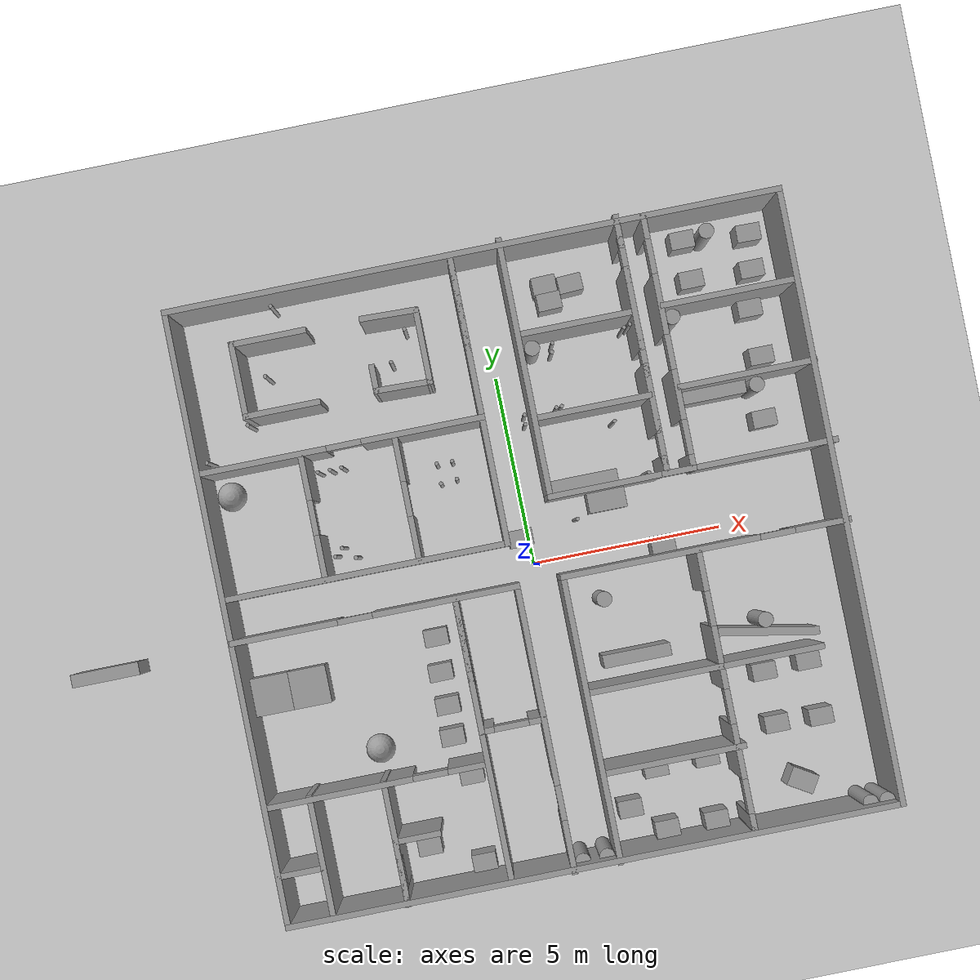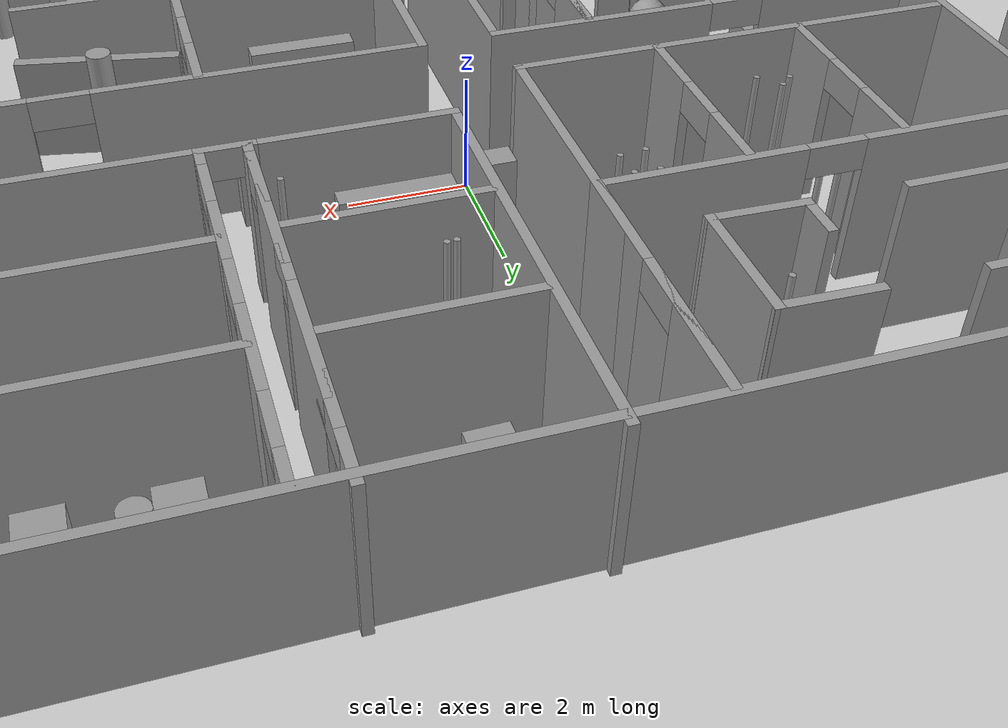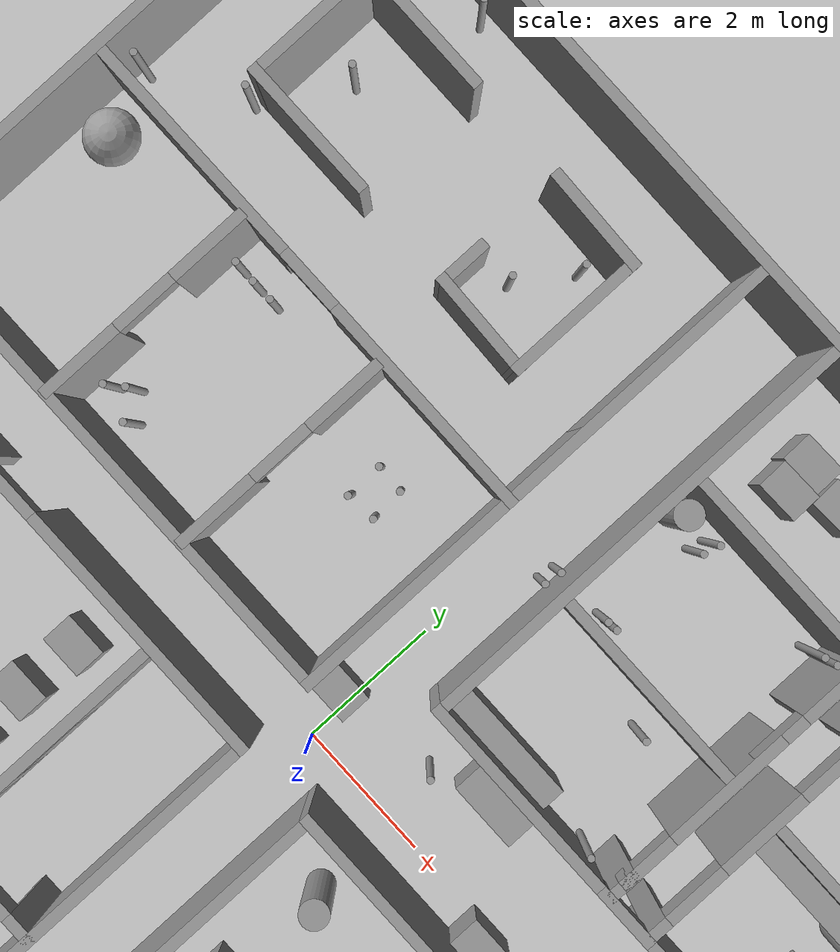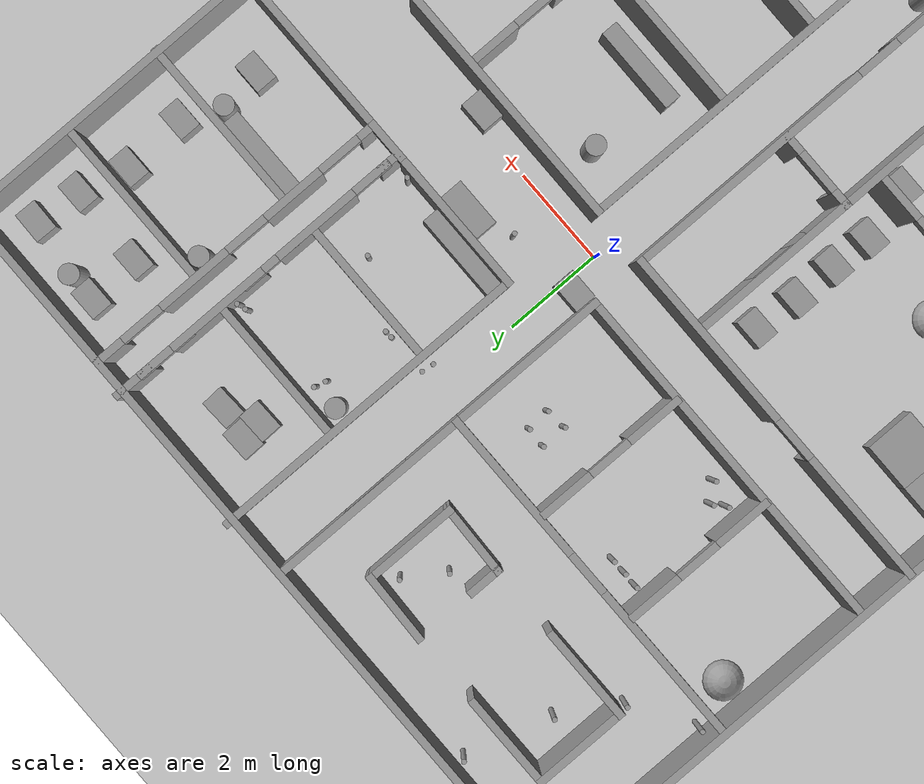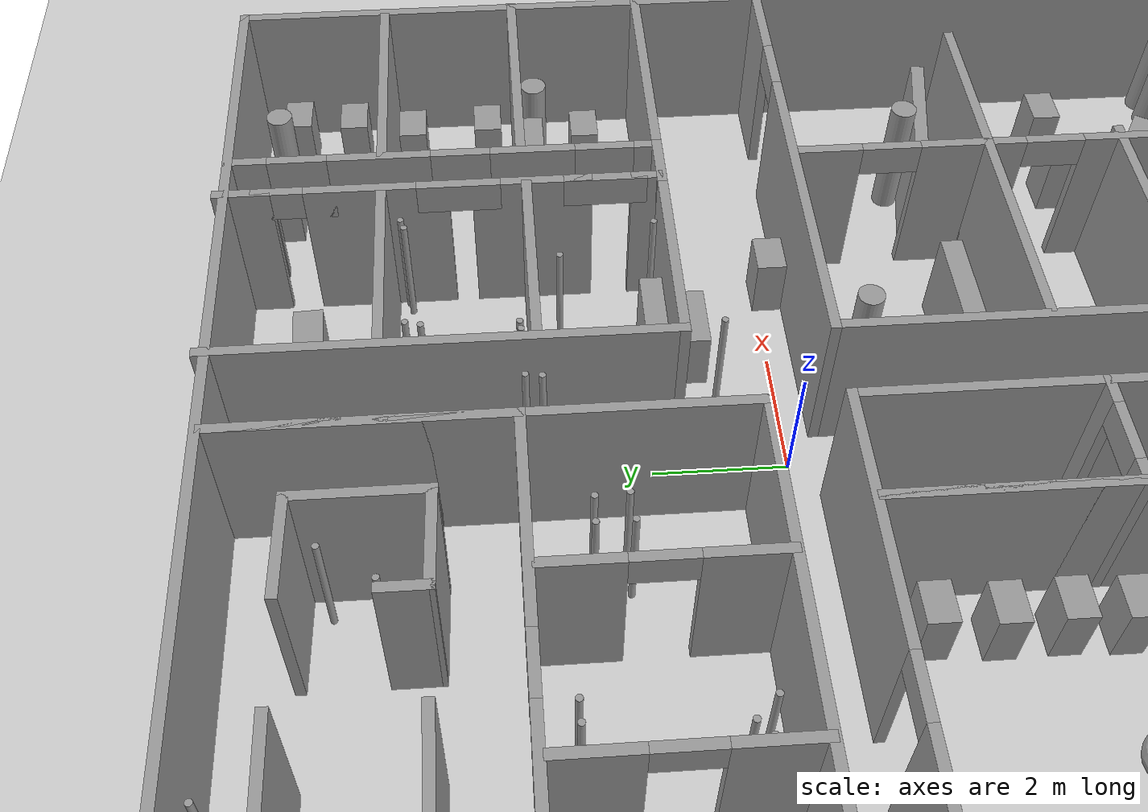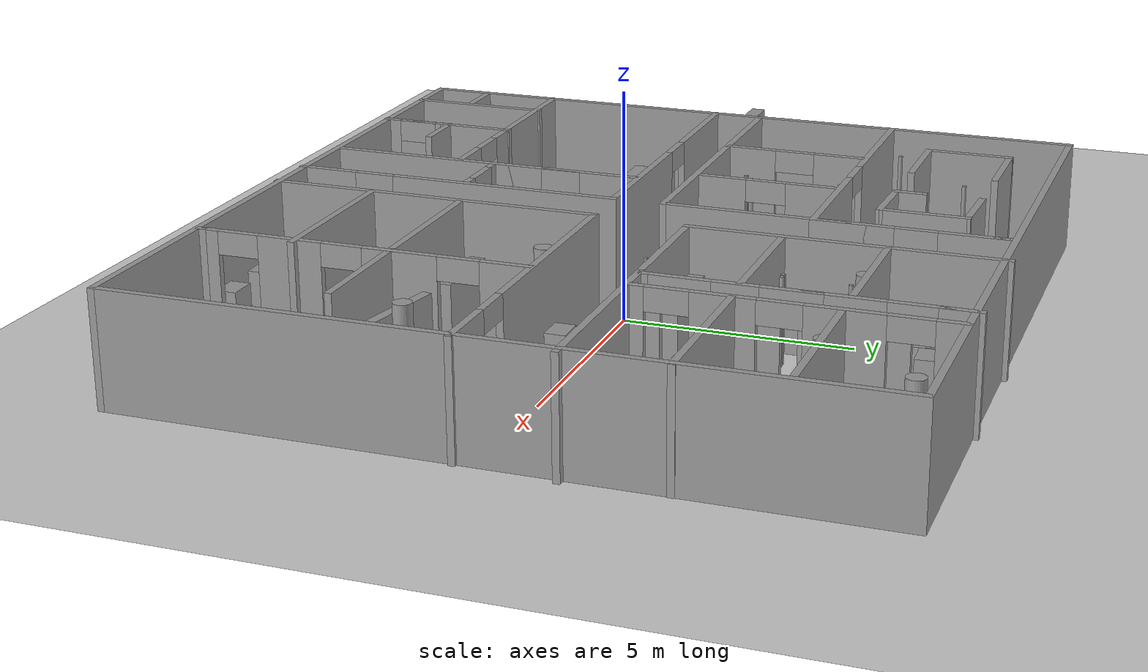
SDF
<sdf version="1.7">
 <world name="default">
  <light name="sun" type="directional">
   <pose>0 0 10 0 -0 0</pose>
   <diffuse>0.8 0.8 0.8 1</diffuse>
   <specular>0.2 0.2 0.2 1</specular>
   <attenuation>
    <range>1000</range>
    <constant>0.9</constant>
    <linear>0.01</linear>
    <quadratic>0.001</quadratic>
   </attenuation>
   <direction>-0.5 0.1 -0.9</direction>
   <spot><inner_angle>0</inner_angle><outer_angle>0</outer_angle><falloff>0</falloff></spot>
  </light>
  <model name="ground_plane">
   <static>1</static>
   <link name="link">
    <collision name="collision">
     <geometry><plane><normal>0 0 1</normal><size>100 100</size></plane></geometry>
     <surface>
      <contact><collide_bitmask>65535</collide_bitmask></contact>
      <friction><ode><mu>100</mu><mu2>50</mu2></ode></friction>
     </surface>
    </collision>
    <visual name="visual">
     <cast_shadows>0</cast_shadows>
     <geometry><plane><normal>0 0 1</normal><size>100 100</size></plane></geometry>
     <material>
      <script><uri>file://media/materials/scripts/gazebo.material</uri><name>Gazebo/Grey</name></script>
     </material>
    </visual>
   </link>
  </model>
  <gravity>0 0 -9.8</gravity>
  <magnetic_field>6e-06 2.3e-05 -4.2e-05</magnetic_field>
  <atmosphere type="adiabatic"/>
  <physics type="ode">
   <max_step_size>0.001</max_step_size>
   <real_time_factor>1</real_time_factor>
   <real_time_update_rate>1000</real_time_update_rate>
  </physics>
  <scene><ambient>0.4 0.4 0.4 1</ambient><background>0.7 0.7 0.7 1</background><shadows>1</shadows></scene>
  <spherical_coordinates>
   <surface_model>EARTH_WGS84</surface_model>
   <latitude_deg>0</latitude_deg>
   <longitude_deg>0</longitude_deg>
   <elevation>0</elevation>
   <heading_deg>0</heading_deg>
  </spherical_coordinates>
  <model name="Untitled_0">
   <link name="link_0">
    <inertial>
     <mass>1</mass>
     <inertia><ixx>0.145833</ixx><ixy>0</ixy><ixz>0</ixz><iyy>0.145833</iyy><iyz>0</iyz><izz>0.125</izz></inertia>
    </inertial>
    <visual name="visual">
     <geometry><cylinder><radius>0.2</radius><length>2</length></cylinder></geometry>
     <material>
      <lighting>1</lighting>
      <script><uri>file://media/materials/scripts/gazebo.material</uri><name>Gazebo/Grey</name></script>
      <shader type="pixel"><normal_map>__default__</normal_map></shader>
      <ambient>0.3 0.3 0.3 1</ambient>
      <diffuse>0.7 0.7 0.7 1</diffuse>
      <specular>0.01 0.01 0.01 1</specular>
      <emissive>0 0 0 1</emissive>
     </material>
    </visual>
    <collision name="collision">
     <geometry><cylinder><radius>0.2</radius><length>2</length></cylinder></geometry>
     <surface>
      <friction>
       <ode><mu>1</mu><mu2>1</mu2><fdir1>0 0 0</fdir1><slip1>0</slip1><slip2>0</slip2></ode>
       <torsional>
        <coefficient>1</coefficient>
        <patch_radius>0</patch_radius>
        <surface_radius>0</surface_radius>
        <use_patch_radius>1</use_patch_radius>
        <ode><slip>0</slip></ode>
       </torsional>
      </friction>
      <bounce><restitution_coefficient>0</restitution_coefficient><threshold>1e+06</threshold></bounce>
      <contact>
       <collide_without_contact>0</collide_without_contact>
       <collide_without_contact_bitmask>1</collide_without_contact_bitmask>
       <collide_bitmask>1</collide_bitmask>
       <ode>
        <soft_cfm>0</soft_cfm>
        <soft_erp>0.2</soft_erp>
        <kp>1e+13</kp>
        <kd>1</kd>
        <max_vel>0.01</max_vel>
        <min_depth>0</min_depth>
       </ode>
       <bullet>
        <split_impulse>1</split_impulse>
        <split_impulse_penetration_threshold>-0.01</split_impulse_penetration_threshold>
        <soft_cfm>0</soft_cfm>
        <soft_erp>0.2</soft_erp>
        <kp>1e+13</kp>
        <kd>1</kd>
       </bullet>
      </contact>
     </surface>
    </collision>
   </link>
   <static>0</static>
   <pose>5.46755 -2.55179 0.999996 0 -0 0.000125</pose>
  </model>
  <model name="Untitled_0_clone">
   <link name="link_0">
    <inertial>
     <mass>1</mass>
     <inertia><ixx>0.145833</ixx><ixy>0</ixy><ixz>0</ixz><iyy>0.145833</iyy><iyz>0</iyz><izz>0.125</izz></inertia>
    </inertial>
    <visual name="visual">
     <geometry><cylinder><radius>0.2</radius><length>2</length></cylinder></geometry>
     <material>
      <lighting>1</lighting>
      <script><uri>file://media/materials/scripts/gazebo.material</uri><name>Gazebo/Grey</name></script>
      <shader type="pixel"><normal_map>__default__</normal_map></shader>
      <ambient>0.3 0.3 0.3 1</ambient>
      <diffuse>0.7 0.7 0.7 1</diffuse>
      <specular>0.01 0.01 0.01 1</specular>
      <emissive>0 0 0 1</emissive>
     </material>
    </visual>
    <collision name="collision">
     <geometry><cylinder><radius>0.2</radius><length>2</length></cylinder></geometry>
     <surface>
      <friction>
       <ode><mu>1</mu><mu2>1</mu2><fdir1>0 0 0</fdir1><slip1>0</slip1><slip2>0</slip2></ode>
       <torsional>
        <coefficient>1</coefficient>
        <patch_radius>0</patch_radius>
        <surface_radius>0</surface_radius>
        <use_patch_radius>1</use_patch_radius>
        <ode><slip>0</slip></ode>
       </torsional>
      </friction>
      <bounce><restitution_coefficient>0</restitution_coefficient><threshold>1e+06</threshold></bounce>
      <contact>
       <collide_without_contact>0</collide_without_contact>
       <collide_without_contact_bitmask>1</collide_without_contact_bitmask>
       <collide_bitmask>1</collide_bitmask>
       <ode>
        <soft_cfm>0</soft_cfm>
        <soft_erp>0.2</soft_erp>
        <kp>1e+13</kp>
        <kd>1</kd>
        <max_vel>0.01</max_vel>
        <min_depth>0</min_depth>
       </ode>
       <bullet>
        <split_impulse>1</split_impulse>
        <split_impulse_penetration_threshold>-0.01</split_impulse_penetration_threshold>
        <soft_cfm>0</soft_cfm>
        <soft_erp>0.2</soft_erp>
        <kp>1e+13</kp>
        <kd>1</kd>
       </bullet>
      </contact>
     </surface>
    </collision>
   </link>
   <static>0</static>
   <pose>1.5286 -1.22831 0.999994 0 -0 0.061669</pose>
  </model>
  <model name="Untitled_0_clone_0">
   <link name="link_0">
    <inertial>
     <mass>1</mass>
     <inertia><ixx>0.145833</ixx><ixy>0</ixy><ixz>0</ixz><iyy>0.145833</iyy><iyz>0</iyz><izz>0.125</izz></inertia>
    </inertial>
    <visual name="visual">
     <geometry><cylinder><radius>0.2</radius><length>2</length></cylinder></geometry>
     <material>
      <lighting>1</lighting>
      <script><uri>file://media/materials/scripts/gazebo.material</uri><name>Gazebo/Grey</name></script>
      <shader type="pixel"><normal_map>__default__</normal_map></shader>
      <ambient>0.3 0.3 0.3 1</ambient>
      <diffuse>0.7 0.7 0.7 1</diffuse>
      <specular>0.01 0.01 0.01 1</specular>
      <emissive>0 0 0 1</emissive>
     </material>
    </visual>
    <collision name="collision">
     <geometry><cylinder><radius>0.2</radius><length>2</length></cylinder></geometry>
     <surface>
      <friction>
       <ode><mu>1</mu><mu2>1</mu2><fdir1>0 0 0</fdir1><slip1>0</slip1><slip2>0</slip2></ode>
       <torsional>
        <coefficient>1</coefficient>
        <patch_radius>0</patch_radius>
        <surface_radius>0</surface_radius>
        <use_patch_radius>1</use_patch_radius>
        <ode><slip>0</slip></ode>
       </torsional>
      </friction>
      <bounce><restitution_coefficient>0</restitution_coefficient><threshold>1e+06</threshold></bounce>
      <contact>
       <collide_without_contact>0</collide_without_contact>
       <collide_without_contact_bitmask>1</collide_without_contact_bitmask>
       <collide_bitmask>1</collide_bitmask>
       <ode>
        <soft_cfm>0</soft_cfm>
        <soft_erp>0.2</soft_erp>
        <kp>1e+13</kp>
        <kd>1</kd>
        <max_vel>0.01</max_vel>
        <min_depth>0</min_depth>
       </ode>
       <bullet>
        <split_impulse>1</split_impulse>
        <split_impulse_penetration_threshold>-0.01</split_impulse_penetration_threshold>
        <soft_cfm>0</soft_cfm>
        <soft_erp>0.2</soft_erp>
        <kp>1e+13</kp>
        <kd>1</kd>
       </bullet>
      </contact>
     </surface>
    </collision>
   </link>
   <static>0</static>
   <pose>7.60637 -7.67249 1 0 0 -0.232737</pose>
  </model>
  <model name="Untitled_0_clone_1">
   <link name="link_0">
    <inertial>
     <mass>1</mass>
     <inertia><ixx>0.145833</ixx><ixy>0</ixy><ixz>0</ixz><iyy>0.145833</iyy><iyz>0</iyz><izz>0.125</izz></inertia>
    </inertial>
    <visual name="visual">
     <geometry><cylinder><radius>0.2</radius><length>2</length></cylinder></geometry>
     <material>
      <lighting>1</lighting>
      <script><uri>file://media/materials/scripts/gazebo.material</uri><name>Gazebo/Grey</name></script>
      <shader type="pixel"><normal_map>__default__</normal_map></shader>
      <ambient>0.3 0.3 0.3 1</ambient>
      <diffuse>0.7 0.7 0.7 1</diffuse>
      <specular>0.01 0.01 0.01 1</specular>
      <emissive>0 0 0 1</emissive>
     </material>
    </visual>
    <collision name="collision">
     <geometry><cylinder><radius>0.2</radius><length>2</length></cylinder></geometry>
     <surface>
      <friction>
       <ode><mu>1</mu><mu2>1</mu2><fdir1>0 0 0</fdir1><slip1>0</slip1><slip2>0</slip2></ode>
       <torsional>
        <coefficient>1</coefficient>
        <patch_radius>0</patch_radius>
        <surface_radius>0</surface_radius>
        <use_patch_radius>1</use_patch_radius>
        <ode><slip>0</slip></ode>
       </torsional>
      </friction>
      <bounce><restitution_coefficient>0</restitution_coefficient><threshold>1e+06</threshold></bounce>
      <contact>
       <collide_without_contact>0</collide_without_contact>
       <collide_without_contact_bitmask>1</collide_without_contact_bitmask>
       <collide_bitmask>1</collide_bitmask>
       <ode>
        <soft_cfm>0</soft_cfm>
        <soft_erp>0.2</soft_erp>
        <kp>1e+13</kp>
        <kd>1</kd>
        <max_vel>0.01</max_vel>
        <min_depth>0</min_depth>
       </ode>
       <bullet>
        <split_impulse>1</split_impulse>
        <split_impulse_penetration_threshold>-0.01</split_impulse_penetration_threshold>
        <soft_cfm>0</soft_cfm>
        <soft_erp>0.2</soft_erp>
        <kp>1e+13</kp>
        <kd>1</kd>
       </bullet>
      </contact>
     </surface>
    </collision>
   </link>
   <static>0</static>
   <pose>7.17536 -7.6593 0.99999 0 -0 0.484716</pose>
  </model>
  <model name="Untitled_0_clone_2">
   <link name="link_0">
    <inertial>
     <mass>1</mass>
     <inertia><ixx>0.145833</ixx><ixy>0</ixy><ixz>0</ixz><iyy>0.145833</iyy><iyz>0</iyz><izz>0.125</izz></inertia>
    </inertial>
    <visual name="visual">
     <geometry><cylinder><radius>0.2</radius><length>2</length></cylinder></geometry>
     <material>
      <lighting>1</lighting>
      <script><uri>file://media/materials/scripts/gazebo.material</uri><name>Gazebo/Grey</name></script>
      <shader type="pixel"><normal_map>__default__</normal_map></shader>
      <ambient>0.3 0.3 0.3 1</ambient>
      <diffuse>0.7 0.7 0.7 1</diffuse>
      <specular>0.01 0.01 0.01 1</specular>
      <emissive>0 0 0 1</emissive>
     </material>
    </visual>
    <collision name="collision">
     <geometry><cylinder><radius>0.2</radius><length>2</length></cylinder></geometry>
     <surface>
      <friction>
       <ode><mu>1</mu><mu2>1</mu2><fdir1>0 0 0</fdir1><slip1>0</slip1><slip2>0</slip2></ode>
       <torsional>
        <coefficient>1</coefficient>
        <patch_radius>0</patch_radius>
        <surface_radius>0</surface_radius>
        <use_patch_radius>1</use_patch_radius>
        <ode><slip>0</slip></ode>
       </torsional>
      </friction>
      <bounce><restitution_coefficient>0</restitution_coefficient><threshold>1e+06</threshold></bounce>
      <contact>
       <collide_without_contact>0</collide_without_contact>
       <collide_without_contact_bitmask>1</collide_without_contact_bitmask>
       <collide_bitmask>1</collide_bitmask>
       <ode>
        <soft_cfm>0</soft_cfm>
        <soft_erp>0.2</soft_erp>
        <kp>1e+13</kp>
        <kd>1</kd>
        <max_vel>0.01</max_vel>
        <min_depth>0</min_depth>
       </ode>
       <bullet>
        <split_impulse>1</split_impulse>
        <split_impulse_penetration_threshold>-0.01</split_impulse_penetration_threshold>
        <soft_cfm>0</soft_cfm>
        <soft_erp>0.2</soft_erp>
        <kp>1e+13</kp>
        <kd>1</kd>
       </bullet>
      </contact>
     </surface>
    </collision>
   </link>
   <static>0</static>
   <pose>-0.314447 -7.67263 1 0 -0 0.09711</pose>
  </model>
  <model name="Untitled_0_clone_3">
   <link name="link_0">
    <inertial>
     <mass>1</mass>
     <inertia><ixx>0.145833</ixx><ixy>0</ixy><ixz>0</ixz><iyy>0.145833</iyy><iyz>0</iyz><izz>0.125</izz></inertia>
    </inertial>
    <visual name="visual">
     <geometry><cylinder><radius>0.2</radius><length>2</length></cylinder></geometry>
     <material>
      <lighting>1</lighting>
      <script><uri>file://media/materials/scripts/gazebo.material</uri><name>Gazebo/Grey</name></script>
      <shader type="pixel"><normal_map>__default__</normal_map></shader>
      <ambient>0.3 0.3 0.3 1</ambient>
      <diffuse>0.7 0.7 0.7 1</diffuse>
      <specular>0.01 0.01 0.01 1</specular>
      <emissive>0 0 0 1</emissive>
     </material>
    </visual>
    <collision name="collision">
     <geometry><cylinder><radius>0.2</radius><length>2</length></cylinder></geometry>
     <surface>
      <friction>
       <ode><mu>1</mu><mu2>1</mu2><fdir1>0 0 0</fdir1><slip1>0</slip1><slip2>0</slip2></ode>
       <torsional>
        <coefficient>1</coefficient>
        <patch_radius>0</patch_radius>
        <surface_radius>0</surface_radius>
        <use_patch_radius>1</use_patch_radius>
        <ode><slip>0</slip></ode>
       </torsional>
      </friction>
      <bounce><restitution_coefficient>0</restitution_coefficient><threshold>1e+06</threshold></bounce>
      <contact>
       <collide_without_contact>0</collide_without_contact>
       <collide_without_contact_bitmask>1</collide_without_contact_bitmask>
       <collide_bitmask>1</collide_bitmask>
       <ode>
        <soft_cfm>0</soft_cfm>
        <soft_erp>0.2</soft_erp>
        <kp>1e+13</kp>
        <kd>1</kd>
        <max_vel>0.01</max_vel>
        <min_depth>0</min_depth>
       </ode>
       <bullet>
        <split_impulse>1</split_impulse>
        <split_impulse_penetration_threshold>-0.01</split_impulse_penetration_threshold>
        <soft_cfm>0</soft_cfm>
        <soft_erp>0.2</soft_erp>
        <kp>1e+13</kp>
        <kd>1</kd>
       </bullet>
      </contact>
     </surface>
    </collision>
   </link>
   <static>0</static>
   <pose>0.314516 -7.6726 1 0 0 -0.024788</pose>
  </model>
  <model name="Untitled">
   <link name="Wall_0">
    <pose>-0.072532 7.88956 0 0 -0 0</pose>
    <visual name="Wall_0_Visual">
     <pose>0 0 1.25 0 -0 0</pose>
     <geometry><box><size>16 0.15 2.5</size></box></geometry>
     <material>
      <script><uri>file://media/materials/scripts/gazebo.material</uri><name>Gazebo/Grey</name></script>
      <ambient>1 1 1 1</ambient>
      <shader type="pixel"/>
     </material>
     <meta><layer>0</layer></meta>
    </visual>
    <collision name="Wall_0_Collision">
     <pose>0 0 1.25 0 -0 0</pose>
     <geometry><box><size>16 0.15 2.5</size></box></geometry>
     <surface>
      <friction>
       <ode><mu>1</mu><mu2>1</mu2><fdir1>0 0 0</fdir1><slip1>0</slip1><slip2>0</slip2></ode>
       <torsional>
        <coefficient>1</coefficient>
        <patch_radius>0</patch_radius>
        <surface_radius>0</surface_radius>
        <use_patch_radius>1</use_patch_radius>
        <ode><slip>0</slip></ode>
       </torsional>
      </friction>
      <bounce><restitution_coefficient>0</restitution_coefficient><threshold>1e+06</threshold></bounce>
      <contact>
       <collide_without_contact>0</collide_without_contact>
       <collide_without_contact_bitmask>1</collide_without_contact_bitmask>
       <collide_bitmask>1</collide_bitmask>
       <ode>
        <soft_cfm>0</soft_cfm>
        <soft_erp>0.2</soft_erp>
        <kp>1e+13</kp>
        <kd>1</kd>
        <max_vel>0.01</max_vel>
        <min_depth>0</min_depth>
       </ode>
       <bullet>
        <split_impulse>1</split_impulse>
        <split_impulse_penetration_threshold>-0.01</split_impulse_penetration_threshold>
        <soft_cfm>0</soft_cfm>
        <soft_erp>0.2</soft_erp>
        <kp>1e+13</kp>
        <kd>1</kd>
       </bullet>
      </contact>
     </surface>
    </collision>
   </link>
   <link name="Wall_1">
    <pose>7.85247 -0.035444 0 0 0 -1.5708</pose>
    <visual name="Wall_1_Visual">
     <pose>0 0 1.25 0 -0 0</pose>
     <geometry><box><size>16 0.15 2.5</size></box></geometry>
     <material>
      <script><uri>file://media/materials/scripts/gazebo.material</uri><name>Gazebo/Grey</name></script>
      <ambient>1 1 1 1</ambient>
      <shader type="pixel"/>
     </material>
     <meta><layer>0</layer></meta>
    </visual>
    <collision name="Wall_1_Collision">
     <pose>0 0 1.25 0 -0 0</pose>
     <geometry><box><size>16 0.15 2.5</size></box></geometry>
     <surface>
      <friction>
       <ode><mu>1</mu><mu2>1</mu2><fdir1>0 0 0</fdir1><slip1>0</slip1><slip2>0</slip2></ode>
       <torsional>
        <coefficient>1</coefficient>
        <patch_radius>0</patch_radius>
        <surface_radius>0</surface_radius>
        <use_patch_radius>1</use_patch_radius>
        <ode><slip>0</slip></ode>
       </torsional>
      </friction>
      <bounce><restitution_coefficient>0</restitution_coefficient><threshold>1e+06</threshold></bounce>
      <contact>
       <collide_without_contact>0</collide_without_contact>
       <collide_without_contact_bitmask>1</collide_without_contact_bitmask>
       <collide_bitmask>1</collide_bitmask>
       <ode>
        <soft_cfm>0</soft_cfm>
        <soft_erp>0.2</soft_erp>
        <kp>1e+13</kp>
        <kd>1</kd>
        <max_vel>0.01</max_vel>
        <min_depth>0</min_depth>
       </ode>
       <bullet>
        <split_impulse>1</split_impulse>
        <split_impulse_penetration_threshold>-0.01</split_impulse_penetration_threshold>
        <soft_cfm>0</soft_cfm>
        <soft_erp>0.2</soft_erp>
        <kp>1e+13</kp>
        <kd>1</kd>
       </bullet>
      </contact>
     </surface>
    </collision>
   </link>
   <link name="Wall_10">
    <pose>-5.33751 2.0447 0 0 -0 1.5708</pose>
    <visual name="Wall_10_Visual_0">
     <pose>-1.02779 0 1.25 0 -0 0</pose>
     <geometry><box><size>1.19441 0.15 2.5</size></box></geometry>
     <material>
      <script><uri>file://media/materials/scripts/gazebo.material</uri><name>Gazebo/Grey</name></script>
      <ambient>1 1 1 1</ambient>
      <shader type="pixel"/>
     </material>
     <meta><layer>0</layer></meta>
    </visual>
    <visual name="Wall_10_Visual_1">
     <pose>1.04721 0 1.25 0 -0 0</pose>
     <geometry><box><size>1.15559 0.15 2.5</size></box></geometry>
     <material>
      <script><uri>file://media/materials/scripts/gazebo.material</uri><name>Gazebo/Grey</name></script>
      <ambient>1 1 1 1</ambient>
      <shader type="pixel"/>
     </material>
     <meta><layer>0</layer></meta>
    </visual>
    <visual name="Wall_10_Visual_2">
     <pose>0.019412 0 2.25 0 -0 0</pose>
     <geometry><box><size>0.9 0.15 0.5</size></box></geometry>
     <material>
      <script><uri>file://media/materials/scripts/gazebo.material</uri><name>Gazebo/Grey</name></script>
      <ambient>1 1 1 1</ambient>
      <shader type="pixel"/>
     </material>
     <meta><layer>0</layer></meta>
    </visual>
    <collision name="Wall_10_Collision_0">
     <pose>-1.02779 0 1.25 0 -0 0</pose>
     <geometry><box><size>1.19441 0.15 2.5</size></box></geometry>
     <surface>
      <friction>
       <ode><mu>1</mu><mu2>1</mu2><fdir1>0 0 0</fdir1><slip1>0</slip1><slip2>0</slip2></ode>
       <torsional>
        <coefficient>1</coefficient>
        <patch_radius>0</patch_radius>
        <surface_radius>0</surface_radius>
        <use_patch_radius>1</use_patch_radius>
        <ode><slip>0</slip></ode>
       </torsional>
      </friction>
      <bounce><restitution_coefficient>0</restitution_coefficient><threshold>1e+06</threshold></bounce>
      <contact>
       <collide_without_contact>0</collide_without_contact>
       <collide_without_contact_bitmask>1</collide_without_contact_bitmask>
       <collide_bitmask>1</collide_bitmask>
       <ode>
        <soft_cfm>0</soft_cfm>
        <soft_erp>0.2</soft_erp>
        <kp>1e+13</kp>
        <kd>1</kd>
        <max_vel>0.01</max_vel>
        <min_depth>0</min_depth>
       </ode>
       <bullet>
        <split_impulse>1</split_impulse>
        <split_impulse_penetration_threshold>-0.01</split_impulse_penetration_threshold>
        <soft_cfm>0</soft_cfm>
        <soft_erp>0.2</soft_erp>
        <kp>1e+13</kp>
        <kd>1</kd>
       </bullet>
      </contact>
     </surface>
    </collision>
    <collision name="Wall_10_Collision_1">
     <pose>1.04721 0 1.25 0 -0 0</pose>
     <geometry><box><size>1.15559 0.15 2.5</size></box></geometry>
     <surface>
      <friction>
       <ode><mu>1</mu><mu2>1</mu2><fdir1>0 0 0</fdir1><slip1>0</slip1><slip2>0</slip2></ode>
       <torsional>
        <coefficient>1</coefficient>
        <patch_radius>0</patch_radius>
        <surface_radius>0</surface_radius>
        <use_patch_radius>1</use_patch_radius>
        <ode><slip>0</slip></ode>
       </torsional>
      </friction>
      <bounce><restitution_coefficient>0</restitution_coefficient><threshold>1e+06</threshold></bounce>
      <contact>
       <collide_without_contact>0</collide_without_contact>
       <collide_without_contact_bitmask>1</collide_without_contact_bitmask>
       <collide_bitmask>1</collide_bitmask>
       <ode>
        <soft_cfm>0</soft_cfm>
        <soft_erp>0.2</soft_erp>
        <kp>1e+13</kp>
        <kd>1</kd>
        <max_vel>0.01</max_vel>
        <min_depth>0</min_depth>
       </ode>
       <bullet>
        <split_impulse>1</split_impulse>
        <split_impulse_penetration_threshold>-0.01</split_impulse_penetration_threshold>
        <soft_cfm>0</soft_cfm>
        <soft_erp>0.2</soft_erp>
        <kp>1e+13</kp>
        <kd>1</kd>
       </bullet>
      </contact>
     </surface>
    </collision>
    <collision name="Wall_10_Collision_2">
     <pose>0.019412 0 2.25 0 -0 0</pose>
     <geometry><box><size>0.9 0.15 0.5</size></box></geometry>
     <surface>
      <friction>
       <ode><mu>1</mu><mu2>1</mu2><fdir1>0 0 0</fdir1><slip1>0</slip1><slip2>0</slip2></ode>
       <torsional>
        <coefficient>1</coefficient>
        <patch_radius>0</patch_radius>
        <surface_radius>0</surface_radius>
        <use_patch_radius>1</use_patch_radius>
        <ode><slip>0</slip></ode>
       </torsional>
      </friction>
      <bounce><restitution_coefficient>0</restitution_coefficient><threshold>1e+06</threshold></bounce>
      <contact>
       <collide_without_contact>0</collide_without_contact>
       <collide_without_contact_bitmask>1</collide_without_contact_bitmask>
       <collide_bitmask>1</collide_bitmask>
       <ode>
        <soft_cfm>0</soft_cfm>
        <soft_erp>0.2</soft_erp>
        <kp>1e+13</kp>
        <kd>1</kd>
        <max_vel>0.01</max_vel>
        <min_depth>0</min_depth>
       </ode>
       <bullet>
        <split_impulse>1</split_impulse>
        <split_impulse_penetration_threshold>-0.01</split_impulse_penetration_threshold>
        <soft_cfm>0</soft_cfm>
        <soft_erp>0.2</soft_erp>
        <kp>1e+13</kp>
        <kd>1</kd>
       </bullet>
      </contact>
     </surface>
    </collision>
   </link>
   <link name="Wall_12">
    <pose>-2.91689 2.0447 0 0 -0 1.5708</pose>
    <visual name="Wall_12_Visual_0">
     <pose>-1.02779 0 1.25 0 -0 0</pose>
     <geometry><box><size>1.19441 0.15 2.5</size></box></geometry>
     <material>
      <script><uri>file://media/materials/scripts/gazebo.material</uri><name>Gazebo/Grey</name></script>
      <ambient>1 1 1 1</ambient>
      <shader type="pixel"/>
     </material>
     <meta><layer>0</layer></meta>
    </visual>
    <visual name="Wall_12_Visual_1">
     <pose>1.04721 0 1.25 0 -0 0</pose>
     <geometry><box><size>1.15559 0.15 2.5</size></box></geometry>
     <material>
      <script><uri>file://media/materials/scripts/gazebo.material</uri><name>Gazebo/Grey</name></script>
      <ambient>1 1 1 1</ambient>
      <shader type="pixel"/>
     </material>
     <meta><layer>0</layer></meta>
    </visual>
    <visual name="Wall_12_Visual_2">
     <pose>0.019412 0 2.25 0 -0 0</pose>
     <geometry><box><size>0.9 0.15 0.5</size></box></geometry>
     <material>
      <script><uri>file://media/materials/scripts/gazebo.material</uri><name>Gazebo/Grey</name></script>
      <ambient>1 1 1 1</ambient>
      <shader type="pixel"/>
     </material>
     <meta><layer>0</layer></meta>
    </visual>
    <collision name="Wall_12_Collision_0">
     <pose>-1.02779 0 1.25 0 -0 0</pose>
     <geometry><box><size>1.19441 0.15 2.5</size></box></geometry>
     <surface>
      <friction>
       <ode><mu>1</mu><mu2>1</mu2><fdir1>0 0 0</fdir1><slip1>0</slip1><slip2>0</slip2></ode>
       <torsional>
        <coefficient>1</coefficient>
        <patch_radius>0</patch_radius>
        <surface_radius>0</surface_radius>
        <use_patch_radius>1</use_patch_radius>
        <ode><slip>0</slip></ode>
       </torsional>
      </friction>
      <bounce><restitution_coefficient>0</restitution_coefficient><threshold>1e+06</threshold></bounce>
      <contact>
       <collide_without_contact>0</collide_without_contact>
       <collide_without_contact_bitmask>1</collide_without_contact_bitmask>
       <collide_bitmask>1</collide_bitmask>
       <ode>
        <soft_cfm>0</soft_cfm>
        <soft_erp>0.2</soft_erp>
        <kp>1e+13</kp>
        <kd>1</kd>
        <max_vel>0.01</max_vel>
        <min_depth>0</min_depth>
       </ode>
       <bullet>
        <split_impulse>1</split_impulse>
        <split_impulse_penetration_threshold>-0.01</split_impulse_penetration_threshold>
        <soft_cfm>0</soft_cfm>
        <soft_erp>0.2</soft_erp>
        <kp>1e+13</kp>
        <kd>1</kd>
       </bullet>
      </contact>
     </surface>
    </collision>
    <collision name="Wall_12_Collision_1">
     <pose>1.04721 0 1.25 0 -0 0</pose>
     <geometry><box><size>1.15559 0.15 2.5</size></box></geometry>
     <surface>
      <friction>
       <ode><mu>1</mu><mu2>1</mu2><fdir1>0 0 0</fdir1><slip1>0</slip1><slip2>0</slip2></ode>
       <torsional>
        <coefficient>1</coefficient>
        <patch_radius>0</patch_radius>
        <surface_radius>0</surface_radius>
        <use_patch_radius>1</use_patch_radius>
        <ode><slip>0</slip></ode>
       </torsional>
      </friction>
      <bounce><restitution_coefficient>0</restitution_coefficient><threshold>1e+06</threshold></bounce>
      <contact>
       <collide_without_contact>0</collide_without_contact>
       <collide_without_contact_bitmask>1</collide_without_contact_bitmask>
       <collide_bitmask>1</collide_bitmask>
       <ode>
        <soft_cfm>0</soft_cfm>
        <soft_erp>0.2</soft_erp>
        <kp>1e+13</kp>
        <kd>1</kd>
        <max_vel>0.01</max_vel>
        <min_depth>0</min_depth>
       </ode>
       <bullet>
        <split_impulse>1</split_impulse>
        <split_impulse_penetration_threshold>-0.01</split_impulse_penetration_threshold>
        <soft_cfm>0</soft_cfm>
        <soft_erp>0.2</soft_erp>
        <kp>1e+13</kp>
        <kd>1</kd>
       </bullet>
      </contact>
     </surface>
    </collision>
    <collision name="Wall_12_Collision_2">
     <pose>0.019412 0 2.25 0 -0 0</pose>
     <geometry><box><size>0.9 0.15 0.5</size></box></geometry>
     <surface>
      <friction>
       <ode><mu>1</mu><mu2>1</mu2><fdir1>0 0 0</fdir1><slip1>0</slip1><slip2>0</slip2></ode>
       <torsional>
        <coefficient>1</coefficient>
        <patch_radius>0</patch_radius>
        <surface_radius>0</surface_radius>
        <use_patch_radius>1</use_patch_radius>
        <ode><slip>0</slip></ode>
       </torsional>
      </friction>
      <bounce><restitution_coefficient>0</restitution_coefficient><threshold>1e+06</threshold></bounce>
      <contact>
       <collide_without_contact>0</collide_without_contact>
       <collide_without_contact_bitmask>1</collide_without_contact_bitmask>
       <collide_bitmask>1</collide_bitmask>
       <ode>
        <soft_cfm>0</soft_cfm>
        <soft_erp>0.2</soft_erp>
        <kp>1e+13</kp>
        <kd>1</kd>
        <max_vel>0.01</max_vel>
        <min_depth>0</min_depth>
       </ode>
       <bullet>
        <split_impulse>1</split_impulse>
        <split_impulse_penetration_threshold>-0.01</split_impulse_penetration_threshold>
        <soft_cfm>0</soft_cfm>
        <soft_erp>0.2</soft_erp>
        <kp>1e+13</kp>
        <kd>1</kd>
       </bullet>
      </contact>
     </surface>
    </collision>
   </link>
   <link name="Wall_14">
    <pose>-5.57091 4.91033 0 0 -0 3.14159</pose>
    <visual name="Wall_14_Visual">
     <pose>0 0 1.25 0 -0 0</pose>
     <geometry><box><size>2 0.15 2.5</size></box></geometry>
     <material>
      <script><uri>file://media/materials/scripts/gazebo.material</uri><name>Gazebo/Grey</name></script>
      <ambient>1 1 1 1</ambient>
      <shader type="pixel"/>
     </material>
     <meta><layer>0</layer></meta>
    </visual>
    <collision name="Wall_14_Collision">
     <pose>0 0 1.25 0 -0 0</pose>
     <geometry><box><size>2 0.15 2.5</size></box></geometry>
     <surface>
      <friction>
       <ode><mu>1</mu><mu2>1</mu2><fdir1>0 0 0</fdir1><slip1>0</slip1><slip2>0</slip2></ode>
       <torsional>
        <coefficient>1</coefficient>
        <patch_radius>0</patch_radius>
        <surface_radius>0</surface_radius>
        <use_patch_radius>1</use_patch_radius>
        <ode><slip>0</slip></ode>
       </torsional>
      </friction>
      <bounce><restitution_coefficient>0</restitution_coefficient><threshold>1e+06</threshold></bounce>
      <contact>
       <collide_without_contact>0</collide_without_contact>
       <collide_without_contact_bitmask>1</collide_without_contact_bitmask>
       <collide_bitmask>1</collide_bitmask>
       <ode>
        <soft_cfm>0</soft_cfm>
        <soft_erp>0.2</soft_erp>
        <kp>1e+13</kp>
        <kd>1</kd>
        <max_vel>0.01</max_vel>
        <min_depth>0</min_depth>
       </ode>
       <bullet>
        <split_impulse>1</split_impulse>
        <split_impulse_penetration_threshold>-0.01</split_impulse_penetration_threshold>
        <soft_cfm>0</soft_cfm>
        <soft_erp>0.2</soft_erp>
        <kp>1e+13</kp>
        <kd>1</kd>
       </bullet>
      </contact>
     </surface>
    </collision>
   </link>
   <link name="Wall_15">
    <pose>-6.49591 5.83533 0 0 -0 1.5708</pose>
    <visual name="Wall_15_Visual">
     <pose>0 0 1.25 0 -0 0</pose>
     <geometry><box><size>2 0.15 2.5</size></box></geometry>
     <material>
      <script><uri>file://media/materials/scripts/gazebo.material</uri><name>Gazebo/Grey</name></script>
      <ambient>1 1 1 1</ambient>
      <shader type="pixel"/>
     </material>
     <meta><layer>0</layer></meta>
    </visual>
    <collision name="Wall_15_Collision">
     <pose>0 0 1.25 0 -0 0</pose>
     <geometry><box><size>2 0.15 2.5</size></box></geometry>
     <surface>
      <friction>
       <ode><mu>1</mu><mu2>1</mu2><fdir1>0 0 0</fdir1><slip1>0</slip1><slip2>0</slip2></ode>
       <torsional>
        <coefficient>1</coefficient>
        <patch_radius>0</patch_radius>
        <surface_radius>0</surface_radius>
        <use_patch_radius>1</use_patch_radius>
        <ode><slip>0</slip></ode>
       </torsional>
      </friction>
      <bounce><restitution_coefficient>0</restitution_coefficient><threshold>1e+06</threshold></bounce>
      <contact>
       <collide_without_contact>0</collide_without_contact>
       <collide_without_contact_bitmask>1</collide_without_contact_bitmask>
       <collide_bitmask>1</collide_bitmask>
       <ode>
        <soft_cfm>0</soft_cfm>
        <soft_erp>0.2</soft_erp>
        <kp>1e+13</kp>
        <kd>1</kd>
        <max_vel>0.01</max_vel>
        <min_depth>0</min_depth>
       </ode>
       <bullet>
        <split_impulse>1</split_impulse>
        <split_impulse_penetration_threshold>-0.01</split_impulse_penetration_threshold>
        <soft_cfm>0</soft_cfm>
        <soft_erp>0.2</soft_erp>
        <kp>1e+13</kp>
        <kd>1</kd>
       </bullet>
      </contact>
     </surface>
    </collision>
   </link>
   <link name="Wall_16">
    <pose>-5.57091 6.76033 0 0 -0 0</pose>
    <visual name="Wall_16_Visual">
     <pose>0 0 1.25 0 -0 0</pose>
     <geometry><box><size>2 0.15 2.5</size></box></geometry>
     <material>
      <script><uri>file://media/materials/scripts/gazebo.material</uri><name>Gazebo/Grey</name></script>
      <ambient>1 1 1 1</ambient>
      <shader type="pixel"/>
     </material>
     <meta><layer>0</layer></meta>
    </visual>
    <collision name="Wall_16_Collision">
     <pose>0 0 1.25 0 -0 0</pose>
     <geometry><box><size>2 0.15 2.5</size></box></geometry>
     <surface>
      <friction>
       <ode><mu>1</mu><mu2>1</mu2><fdir1>0 0 0</fdir1><slip1>0</slip1><slip2>0</slip2></ode>
       <torsional>
        <coefficient>1</coefficient>
        <patch_radius>0</patch_radius>
        <surface_radius>0</surface_radius>
        <use_patch_radius>1</use_patch_radius>
        <ode><slip>0</slip></ode>
       </torsional>
      </friction>
      <bounce><restitution_coefficient>0</restitution_coefficient><threshold>1e+06</threshold></bounce>
      <contact>
       <collide_without_contact>0</collide_without_contact>
       <collide_without_contact_bitmask>1</collide_without_contact_bitmask>
       <collide_bitmask>1</collide_bitmask>
       <ode>
        <soft_cfm>0</soft_cfm>
        <soft_erp>0.2</soft_erp>
        <kp>1e+13</kp>
        <kd>1</kd>
        <max_vel>0.01</max_vel>
        <min_depth>0</min_depth>
       </ode>
       <bullet>
        <split_impulse>1</split_impulse>
        <split_impulse_penetration_threshold>-0.01</split_impulse_penetration_threshold>
        <soft_cfm>0</soft_cfm>
        <soft_erp>0.2</soft_erp>
        <kp>1e+13</kp>
        <kd>1</kd>
       </bullet>
      </contact>
     </surface>
    </collision>
   </link>
   <link name="Wall_18">
    <pose>-2.4441 6.72429 0 0 0 -0.031294</pose>
    <visual name="Wall_18_Visual">
     <pose>0 0 1.25 0 -0 0</pose>
     <geometry><box><size>1.52186 0.15 2.5</size></box></geometry>
     <material>
      <script><uri>file://media/materials/scripts/gazebo.material</uri><name>Gazebo/Grey</name></script>
      <ambient>1 1 1 1</ambient>
      <shader type="pixel"/>
     </material>
     <meta><layer>0</layer></meta>
    </visual>
    <collision name="Wall_18_Collision">
     <pose>0 0 1.25 0 -0 0</pose>
     <geometry><box><size>1.52186 0.15 2.5</size></box></geometry>
     <surface>
      <friction>
       <ode><mu>1</mu><mu2>1</mu2><fdir1>0 0 0</fdir1><slip1>0</slip1><slip2>0</slip2></ode>
       <torsional>
        <coefficient>1</coefficient>
        <patch_radius>0</patch_radius>
        <surface_radius>0</surface_radius>
        <use_patch_radius>1</use_patch_radius>
        <ode><slip>0</slip></ode>
       </torsional>
      </friction>
      <bounce><restitution_coefficient>0</restitution_coefficient><threshold>1e+06</threshold></bounce>
      <contact>
       <collide_without_contact>0</collide_without_contact>
       <collide_without_contact_bitmask>1</collide_without_contact_bitmask>
       <collide_bitmask>1</collide_bitmask>
       <ode>
        <soft_cfm>0</soft_cfm>
        <soft_erp>0.2</soft_erp>
        <kp>1e+13</kp>
        <kd>1</kd>
        <max_vel>0.01</max_vel>
        <min_depth>0</min_depth>
       </ode>
       <bullet>
        <split_impulse>1</split_impulse>
        <split_impulse_penetration_threshold>-0.01</split_impulse_penetration_threshold>
        <soft_cfm>0</soft_cfm>
        <soft_erp>0.2</soft_erp>
        <kp>1e+13</kp>
        <kd>1</kd>
       </bullet>
      </contact>
     </surface>
    </collision>
   </link>
   <link name="Wall_19">
    <pose>-1.75851 5.77782 0 0 0 -1.5708</pose>
    <visual name="Wall_19_Visual">
     <pose>0 0 1.25 0 -0 0</pose>
     <geometry><box><size>2 0.15 2.5</size></box></geometry>
     <material>
      <script><uri>file://media/materials/scripts/gazebo.material</uri><name>Gazebo/Grey</name></script>
      <ambient>1 1 1 1</ambient>
      <shader type="pixel"/>
     </material>
     <meta><layer>0</layer></meta>
    </visual>
    <collision name="Wall_19_Collision">
     <pose>0 0 1.25 0 -0 0</pose>
     <geometry><box><size>2 0.15 2.5</size></box></geometry>
     <surface>
      <friction>
       <ode><mu>1</mu><mu2>1</mu2><fdir1>0 0 0</fdir1><slip1>0</slip1><slip2>0</slip2></ode>
       <torsional>
        <coefficient>1</coefficient>
        <patch_radius>0</patch_radius>
        <surface_radius>0</surface_radius>
        <use_patch_radius>1</use_patch_radius>
        <ode><slip>0</slip></ode>
       </torsional>
      </friction>
      <bounce><restitution_coefficient>0</restitution_coefficient><threshold>1e+06</threshold></bounce>
      <contact>
       <collide_without_contact>0</collide_without_contact>
       <collide_without_contact_bitmask>1</collide_without_contact_bitmask>
       <collide_bitmask>1</collide_bitmask>
       <ode>
        <soft_cfm>0</soft_cfm>
        <soft_erp>0.2</soft_erp>
        <kp>1e+13</kp>
        <kd>1</kd>
        <max_vel>0.01</max_vel>
        <min_depth>0</min_depth>
       </ode>
       <bullet>
        <split_impulse>1</split_impulse>
        <split_impulse_penetration_threshold>-0.01</split_impulse_penetration_threshold>
        <soft_cfm>0</soft_cfm>
        <soft_erp>0.2</soft_erp>
        <kp>1e+13</kp>
        <kd>1</kd>
       </bullet>
      </contact>
     </surface>
    </collision>
   </link>
   <link name="Wall_2">
    <pose>-0.072532 -7.96044 0 0 -0 3.14159</pose>
    <visual name="Wall_2_Visual">
     <pose>0 0 1.25 0 -0 0</pose>
     <geometry><box><size>16 0.15 2.5</size></box></geometry>
     <material>
      <script><uri>file://media/materials/scripts/gazebo.material</uri><name>Gazebo/Grey</name></script>
      <ambient>1 1 1 1</ambient>
      <shader type="pixel"/>
     </material>
     <meta><layer>0</layer></meta>
    </visual>
    <collision name="Wall_2_Collision">
     <pose>0 0 1.25 0 -0 0</pose>
     <geometry><box><size>16 0.15 2.5</size></box></geometry>
     <surface>
      <friction>
       <ode><mu>1</mu><mu2>1</mu2><fdir1>0 0 0</fdir1><slip1>0</slip1><slip2>0</slip2></ode>
       <torsional>
        <coefficient>1</coefficient>
        <patch_radius>0</patch_radius>
        <surface_radius>0</surface_radius>
        <use_patch_radius>1</use_patch_radius>
        <ode><slip>0</slip></ode>
       </torsional>
      </friction>
      <bounce><restitution_coefficient>0</restitution_coefficient><threshold>1e+06</threshold></bounce>
      <contact>
       <collide_without_contact>0</collide_without_contact>
       <collide_without_contact_bitmask>1</collide_without_contact_bitmask>
       <collide_bitmask>1</collide_bitmask>
       <ode>
        <soft_cfm>0</soft_cfm>
        <soft_erp>0.2</soft_erp>
        <kp>1e+13</kp>
        <kd>1</kd>
        <max_vel>0.01</max_vel>
        <min_depth>0</min_depth>
       </ode>
       <bullet>
        <split_impulse>1</split_impulse>
        <split_impulse_penetration_threshold>-0.01</split_impulse_penetration_threshold>
        <soft_cfm>0</soft_cfm>
        <soft_erp>0.2</soft_erp>
        <kp>1e+13</kp>
        <kd>1</kd>
       </bullet>
      </contact>
     </surface>
    </collision>
   </link>
   <link name="Wall_20">
    <pose>-2.4441 4.87429 0 0 -0 3.1103</pose>
    <visual name="Wall_20_Visual">
     <pose>0 0 1.25 0 -0 0</pose>
     <geometry><box><size>1.52186 0.15 2.5</size></box></geometry>
     <material>
      <script><uri>file://media/materials/scripts/gazebo.material</uri><name>Gazebo/Grey</name></script>
      <ambient>1 1 1 1</ambient>
      <shader type="pixel"/>
     </material>
     <meta><layer>0</layer></meta>
    </visual>
    <collision name="Wall_20_Collision">
     <pose>0 0 1.25 0 -0 0</pose>
     <geometry><box><size>1.52186 0.15 2.5</size></box></geometry>
     <surface>
      <friction>
       <ode><mu>1</mu><mu2>1</mu2><fdir1>0 0 0</fdir1><slip1>0</slip1><slip2>0</slip2></ode>
       <torsional>
        <coefficient>1</coefficient>
        <patch_radius>0</patch_radius>
        <surface_radius>0</surface_radius>
        <use_patch_radius>1</use_patch_radius>
        <ode><slip>0</slip></ode>
       </torsional>
      </friction>
      <bounce><restitution_coefficient>0</restitution_coefficient><threshold>1e+06</threshold></bounce>
      <contact>
       <collide_without_contact>0</collide_without_contact>
       <collide_without_contact_bitmask>1</collide_without_contact_bitmask>
       <collide_bitmask>1</collide_bitmask>
       <ode>
        <soft_cfm>0</soft_cfm>
        <soft_erp>0.2</soft_erp>
        <kp>1e+13</kp>
        <kd>1</kd>
        <max_vel>0.01</max_vel>
        <min_depth>0</min_depth>
       </ode>
       <bullet>
        <split_impulse>1</split_impulse>
        <split_impulse_penetration_threshold>-0.01</split_impulse_penetration_threshold>
        <soft_cfm>0</soft_cfm>
        <soft_erp>0.2</soft_erp>
        <kp>1e+13</kp>
        <kd>1</kd>
       </bullet>
      </contact>
     </surface>
    </collision>
   </link>
   <link name="Wall_21">
    <pose>-3.1297 5.19575 0 0 -0 1.5708</pose>
    <visual name="Wall_21_Visual">
     <pose>0 0 1.25 0 -0 0</pose>
     <geometry><box><size>0.75 0.15 2.5</size></box></geometry>
     <material>
      <script><uri>file://media/materials/scripts/gazebo.material</uri><name>Gazebo/Grey</name></script>
      <ambient>1 1 1 1</ambient>
      <shader type="pixel"/>
     </material>
     <meta><layer>0</layer></meta>
    </visual>
    <collision name="Wall_21_Collision">
     <pose>0 0 1.25 0 -0 0</pose>
     <geometry><box><size>0.75 0.15 2.5</size></box></geometry>
     <surface>
      <friction>
       <ode><mu>1</mu><mu2>1</mu2><fdir1>0 0 0</fdir1><slip1>0</slip1><slip2>0</slip2></ode>
       <torsional>
        <coefficient>1</coefficient>
        <patch_radius>0</patch_radius>
        <surface_radius>0</surface_radius>
        <use_patch_radius>1</use_patch_radius>
        <ode><slip>0</slip></ode>
       </torsional>
      </friction>
      <bounce><restitution_coefficient>0</restitution_coefficient><threshold>1e+06</threshold></bounce>
      <contact>
       <collide_without_contact>0</collide_without_contact>
       <collide_without_contact_bitmask>1</collide_without_contact_bitmask>
       <collide_bitmask>1</collide_bitmask>
       <ode>
        <soft_cfm>0</soft_cfm>
        <soft_erp>0.2</soft_erp>
        <kp>1e+13</kp>
        <kd>1</kd>
        <max_vel>0.01</max_vel>
        <min_depth>0</min_depth>
       </ode>
       <bullet>
        <split_impulse>1</split_impulse>
        <split_impulse_penetration_threshold>-0.01</split_impulse_penetration_threshold>
        <soft_cfm>0</soft_cfm>
        <soft_erp>0.2</soft_erp>
        <kp>1e+13</kp>
        <kd>1</kd>
       </bullet>
      </contact>
     </surface>
    </collision>
   </link>
   <link name="Wall_23">
    <pose>-4.29593 -0.649108 0 0 -0 0</pose>
    <visual name="Wall_23_Visual_0">
     <pose>-2.35479 0 1.25 0 -0 0</pose>
     <geometry><box><size>2.79042 0.15 2.5</size></box></geometry>
     <material>
      <script><uri>file://media/materials/scripts/gazebo.material</uri><name>Gazebo/Grey</name></script>
      <ambient>1 1 1 1</ambient>
      <shader type="pixel"/>
     </material>
     <meta><layer>0</layer></meta>
    </visual>
    <visual name="Wall_23_Visual_1">
     <pose>1.84521 0 1.25 0 -0 0</pose>
     <geometry><box><size>3.80958 0.15 2.5</size></box></geometry>
     <material>
      <script><uri>file://media/materials/scripts/gazebo.material</uri><name>Gazebo/Grey</name></script>
      <ambient>1 1 1 1</ambient>
      <shader type="pixel"/>
     </material>
     <meta><layer>0</layer></meta>
    </visual>
    <visual name="Wall_23_Visual_2">
     <pose>-0.509576 0 2.25 0 -0 0</pose>
     <geometry><box><size>0.9 0.15 0.5</size></box></geometry>
     <material>
      <script><uri>file://media/materials/scripts/gazebo.material</uri><name>Gazebo/Grey</name></script>
      <ambient>1 1 1 1</ambient>
      <shader type="pixel"/>
     </material>
     <meta><layer>0</layer></meta>
    </visual>
    <collision name="Wall_23_Collision_0">
     <pose>-2.35479 0 1.25 0 -0 0</pose>
     <geometry><box><size>2.79042 0.15 2.5</size></box></geometry>
     <surface>
      <friction>
       <ode><mu>1</mu><mu2>1</mu2><fdir1>0 0 0</fdir1><slip1>0</slip1><slip2>0</slip2></ode>
       <torsional>
        <coefficient>1</coefficient>
        <patch_radius>0</patch_radius>
        <surface_radius>0</surface_radius>
        <use_patch_radius>1</use_patch_radius>
        <ode><slip>0</slip></ode>
       </torsional>
      </friction>
      <bounce><restitution_coefficient>0</restitution_coefficient><threshold>1e+06</threshold></bounce>
      <contact>
       <collide_without_contact>0</collide_without_contact>
       <collide_without_contact_bitmask>1</collide_without_contact_bitmask>
       <collide_bitmask>1</collide_bitmask>
       <ode>
        <soft_cfm>0</soft_cfm>
        <soft_erp>0.2</soft_erp>
        <kp>1e+13</kp>
        <kd>1</kd>
        <max_vel>0.01</max_vel>
        <min_depth>0</min_depth>
       </ode>
       <bullet>
        <split_impulse>1</split_impulse>
        <split_impulse_penetration_threshold>-0.01</split_impulse_penetration_threshold>
        <soft_cfm>0</soft_cfm>
        <soft_erp>0.2</soft_erp>
        <kp>1e+13</kp>
        <kd>1</kd>
       </bullet>
      </contact>
     </surface>
    </collision>
    <collision name="Wall_23_Collision_1">
     <pose>1.84521 0 1.25 0 -0 0</pose>
     <geometry><box><size>3.80958 0.15 2.5</size></box></geometry>
     <surface>
      <friction>
       <ode><mu>1</mu><mu2>1</mu2><fdir1>0 0 0</fdir1><slip1>0</slip1><slip2>0</slip2></ode>
       <torsional>
        <coefficient>1</coefficient>
        <patch_radius>0</patch_radius>
        <surface_radius>0</surface_radius>
        <use_patch_radius>1</use_patch_radius>
        <ode><slip>0</slip></ode>
       </torsional>
      </friction>
      <bounce><restitution_coefficient>0</restitution_coefficient><threshold>1e+06</threshold></bounce>
      <contact>
       <collide_without_contact>0</collide_without_contact>
       <collide_without_contact_bitmask>1</collide_without_contact_bitmask>
       <collide_bitmask>1</collide_bitmask>
       <ode>
        <soft_cfm>0</soft_cfm>
        <soft_erp>0.2</soft_erp>
        <kp>1e+13</kp>
        <kd>1</kd>
        <max_vel>0.01</max_vel>
        <min_depth>0</min_depth>
       </ode>
       <bullet>
        <split_impulse>1</split_impulse>
        <split_impulse_penetration_threshold>-0.01</split_impulse_penetration_threshold>
        <soft_cfm>0</soft_cfm>
        <soft_erp>0.2</soft_erp>
        <kp>1e+13</kp>
        <kd>1</kd>
       </bullet>
      </contact>
     </surface>
    </collision>
    <collision name="Wall_23_Collision_2">
     <pose>-0.509576 0 2.25 0 -0 0</pose>
     <geometry><box><size>0.9 0.15 0.5</size></box></geometry>
     <surface>
      <friction>
       <ode><mu>1</mu><mu2>1</mu2><fdir1>0 0 0</fdir1><slip1>0</slip1><slip2>0</slip2></ode>
       <torsional>
        <coefficient>1</coefficient>
        <patch_radius>0</patch_radius>
        <surface_radius>0</surface_radius>
        <use_patch_radius>1</use_patch_radius>
        <ode><slip>0</slip></ode>
       </torsional>
      </friction>
      <bounce><restitution_coefficient>0</restitution_coefficient><threshold>1e+06</threshold></bounce>
      <contact>
       <collide_without_contact>0</collide_without_contact>
       <collide_without_contact_bitmask>1</collide_without_contact_bitmask>
       <collide_bitmask>1</collide_bitmask>
       <ode>
        <soft_cfm>0</soft_cfm>
        <soft_erp>0.2</soft_erp>
        <kp>1e+13</kp>
        <kd>1</kd>
        <max_vel>0.01</max_vel>
        <min_depth>0</min_depth>
       </ode>
       <bullet>
        <split_impulse>1</split_impulse>
        <split_impulse_penetration_threshold>-0.01</split_impulse_penetration_threshold>
        <soft_cfm>0</soft_cfm>
        <soft_erp>0.2</soft_erp>
        <kp>1e+13</kp>
        <kd>1</kd>
       </bullet>
      </contact>
     </surface>
    </collision>
   </link>
   <link name="Wall_24">
    <pose>-0.620932 -4.32411 0 0 0 -1.5708</pose>
    <visual name="Wall_24_Visual_0">
     <pose>-1.14448 0 1.25 0 -0 0</pose>
     <geometry><box><size>5.21104 0.15 2.5</size></box></geometry>
     <material>
      <script><uri>file://media/materials/scripts/gazebo.material</uri><name>Gazebo/Grey</name></script>
      <ambient>1 1 1 1</ambient>
      <shader type="pixel"/>
     </material>
     <meta><layer>0</layer></meta>
    </visual>
    <visual name="Wall_24_Visual_1">
     <pose>3.05552 0 1.25 0 -0 0</pose>
     <geometry><box><size>1.38896 0.15 2.5</size></box></geometry>
     <material>
      <script><uri>file://media/materials/scripts/gazebo.material</uri><name>Gazebo/Grey</name></script>
      <ambient>1 1 1 1</ambient>
      <shader type="pixel"/>
     </material>
     <meta><layer>0</layer></meta>
    </visual>
    <visual name="Wall_24_Visual_2">
     <pose>1.91104 0 2.25 0 -0 0</pose>
     <geometry><box><size>0.9 0.15 0.5</size></box></geometry>
     <material>
      <script><uri>file://media/materials/scripts/gazebo.material</uri><name>Gazebo/Grey</name></script>
      <ambient>1 1 1 1</ambient>
      <shader type="pixel"/>
     </material>
     <meta><layer>0</layer></meta>
    </visual>
    <collision name="Wall_24_Collision_0">
     <pose>-1.14448 0 1.25 0 -0 0</pose>
     <geometry><box><size>5.21104 0.15 2.5</size></box></geometry>
     <surface>
      <friction>
       <ode><mu>1</mu><mu2>1</mu2><fdir1>0 0 0</fdir1><slip1>0</slip1><slip2>0</slip2></ode>
       <torsional>
        <coefficient>1</coefficient>
        <patch_radius>0</patch_radius>
        <surface_radius>0</surface_radius>
        <use_patch_radius>1</use_patch_radius>
        <ode><slip>0</slip></ode>
       </torsional>
      </friction>
      <bounce><restitution_coefficient>0</restitution_coefficient><threshold>1e+06</threshold></bounce>
      <contact>
       <collide_without_contact>0</collide_without_contact>
       <collide_without_contact_bitmask>1</collide_without_contact_bitmask>
       <collide_bitmask>1</collide_bitmask>
       <ode>
        <soft_cfm>0</soft_cfm>
        <soft_erp>0.2</soft_erp>
        <kp>1e+13</kp>
        <kd>1</kd>
        <max_vel>0.01</max_vel>
        <min_depth>0</min_depth>
       </ode>
       <bullet>
        <split_impulse>1</split_impulse>
        <split_impulse_penetration_threshold>-0.01</split_impulse_penetration_threshold>
        <soft_cfm>0</soft_cfm>
        <soft_erp>0.2</soft_erp>
        <kp>1e+13</kp>
        <kd>1</kd>
       </bullet>
      </contact>
     </surface>
    </collision>
    <collision name="Wall_24_Collision_1">
     <pose>3.05552 0 1.25 0 -0 0</pose>
     <geometry><box><size>1.38896 0.15 2.5</size></box></geometry>
     <surface>
      <friction>
       <ode><mu>1</mu><mu2>1</mu2><fdir1>0 0 0</fdir1><slip1>0</slip1><slip2>0</slip2></ode>
       <torsional>
        <coefficient>1</coefficient>
        <patch_radius>0</patch_radius>
        <surface_radius>0</surface_radius>
        <use_patch_radius>1</use_patch_radius>
        <ode><slip>0</slip></ode>
       </torsional>
      </friction>
      <bounce><restitution_coefficient>0</restitution_coefficient><threshold>1e+06</threshold></bounce>
      <contact>
       <collide_without_contact>0</collide_without_contact>
       <collide_without_contact_bitmask>1</collide_without_contact_bitmask>
       <collide_bitmask>1</collide_bitmask>
       <ode>
        <soft_cfm>0</soft_cfm>
        <soft_erp>0.2</soft_erp>
        <kp>1e+13</kp>
        <kd>1</kd>
        <max_vel>0.01</max_vel>
        <min_depth>0</min_depth>
       </ode>
       <bullet>
        <split_impulse>1</split_impulse>
        <split_impulse_penetration_threshold>-0.01</split_impulse_penetration_threshold>
        <soft_cfm>0</soft_cfm>
        <soft_erp>0.2</soft_erp>
        <kp>1e+13</kp>
        <kd>1</kd>
       </bullet>
      </contact>
     </surface>
    </collision>
    <collision name="Wall_24_Collision_2">
     <pose>1.91104 0 2.25 0 -0 0</pose>
     <geometry><box><size>0.9 0.15 0.5</size></box></geometry>
     <surface>
      <friction>
       <ode><mu>1</mu><mu2>1</mu2><fdir1>0 0 0</fdir1><slip1>0</slip1><slip2>0</slip2></ode>
       <torsional>
        <coefficient>1</coefficient>
        <patch_radius>0</patch_radius>
        <surface_radius>0</surface_radius>
        <use_patch_radius>1</use_patch_radius>
        <ode><slip>0</slip></ode>
       </torsional>
      </friction>
      <bounce><restitution_coefficient>0</restitution_coefficient><threshold>1e+06</threshold></bounce>
      <contact>
       <collide_without_contact>0</collide_without_contact>
       <collide_without_contact_bitmask>1</collide_without_contact_bitmask>
       <collide_bitmask>1</collide_bitmask>
       <ode>
        <soft_cfm>0</soft_cfm>
        <soft_erp>0.2</soft_erp>
        <kp>1e+13</kp>
        <kd>1</kd>
        <max_vel>0.01</max_vel>
        <min_depth>0</min_depth>
       </ode>
       <bullet>
        <split_impulse>1</split_impulse>
        <split_impulse_penetration_threshold>-0.01</split_impulse_penetration_threshold>
        <soft_cfm>0</soft_cfm>
        <soft_erp>0.2</soft_erp>
        <kp>1e+13</kp>
        <kd>1</kd>
       </bullet>
      </contact>
     </surface>
    </collision>
   </link>
   <link name="Wall_26">
    <pose>-1.42928 -4.08053 0 0 -0 3.14159</pose>
    <visual name="Wall_26_Visual_0">
     <pose>-0.650197 0 1.25 0 -0 0</pose>
     <geometry><box><size>0.449606 0.15 2.5</size></box></geometry>
     <material>
      <script><uri>file://media/materials/scripts/gazebo.material</uri><name>Gazebo/Grey</name></script>
      <ambient>1 1 1 1</ambient>
      <shader type="pixel"/>
     </material>
     <meta><layer>0</layer></meta>
    </visual>
    <visual name="Wall_26_Visual_1">
     <pose>0.674803 0 1.25 0 -0 0</pose>
     <geometry><box><size>0.400394 0.15 2.5</size></box></geometry>
     <material>
      <script><uri>file://media/materials/scripts/gazebo.material</uri><name>Gazebo/Grey</name></script>
      <ambient>1 1 1 1</ambient>
      <shader type="pixel"/>
     </material>
     <meta><layer>0</layer></meta>
    </visual>
    <visual name="Wall_26_Visual_2">
     <pose>0.024606 0 2.25 0 -0 0</pose>
     <geometry><box><size>0.9 0.15 0.5</size></box></geometry>
     <material>
      <script><uri>file://media/materials/scripts/gazebo.material</uri><name>Gazebo/Grey</name></script>
      <ambient>1 1 1 1</ambient>
      <shader type="pixel"/>
     </material>
     <meta><layer>0</layer></meta>
    </visual>
    <collision name="Wall_26_Collision_0">
     <pose>-0.650197 0 1.25 0 -0 0</pose>
     <geometry><box><size>0.449606 0.15 2.5</size></box></geometry>
     <surface>
      <friction>
       <ode><mu>1</mu><mu2>1</mu2><fdir1>0 0 0</fdir1><slip1>0</slip1><slip2>0</slip2></ode>
       <torsional>
        <coefficient>1</coefficient>
        <patch_radius>0</patch_radius>
        <surface_radius>0</surface_radius>
        <use_patch_radius>1</use_patch_radius>
        <ode><slip>0</slip></ode>
       </torsional>
      </friction>
      <bounce><restitution_coefficient>0</restitution_coefficient><threshold>1e+06</threshold></bounce>
      <contact>
       <collide_without_contact>0</collide_without_contact>
       <collide_without_contact_bitmask>1</collide_without_contact_bitmask>
       <collide_bitmask>1</collide_bitmask>
       <ode>
        <soft_cfm>0</soft_cfm>
        <soft_erp>0.2</soft_erp>
        <kp>1e+13</kp>
        <kd>1</kd>
        <max_vel>0.01</max_vel>
        <min_depth>0</min_depth>
       </ode>
       <bullet>
        <split_impulse>1</split_impulse>
        <split_impulse_penetration_threshold>-0.01</split_impulse_penetration_threshold>
        <soft_cfm>0</soft_cfm>
        <soft_erp>0.2</soft_erp>
        <kp>1e+13</kp>
        <kd>1</kd>
       </bullet>
      </contact>
     </surface>
    </collision>
    <collision name="Wall_26_Collision_1">
     <pose>0.674803 0 1.25 0 -0 0</pose>
     <geometry><box><size>0.400394 0.15 2.5</size></box></geometry>
     <surface>
      <friction>
       <ode><mu>1</mu><mu2>1</mu2><fdir1>0 0 0</fdir1><slip1>0</slip1><slip2>0</slip2></ode>
       <torsional>
        <coefficient>1</coefficient>
        <patch_radius>0</patch_radius>
        <surface_radius>0</surface_radius>
        <use_patch_radius>1</use_patch_radius>
        <ode><slip>0</slip></ode>
       </torsional>
      </friction>
      <bounce><restitution_coefficient>0</restitution_coefficient><threshold>1e+06</threshold></bounce>
      <contact>
       <collide_without_contact>0</collide_without_contact>
       <collide_without_contact_bitmask>1</collide_without_contact_bitmask>
       <collide_bitmask>1</collide_bitmask>
       <ode>
        <soft_cfm>0</soft_cfm>
        <soft_erp>0.2</soft_erp>
        <kp>1e+13</kp>
        <kd>1</kd>
        <max_vel>0.01</max_vel>
        <min_depth>0</min_depth>
       </ode>
       <bullet>
        <split_impulse>1</split_impulse>
        <split_impulse_penetration_threshold>-0.01</split_impulse_penetration_threshold>
        <soft_cfm>0</soft_cfm>
        <soft_erp>0.2</soft_erp>
        <kp>1e+13</kp>
        <kd>1</kd>
       </bullet>
      </contact>
     </surface>
    </collision>
    <collision name="Wall_26_Collision_2">
     <pose>0.024606 0 2.25 0 -0 0</pose>
     <geometry><box><size>0.9 0.15 0.5</size></box></geometry>
     <surface>
      <friction>
       <ode><mu>1</mu><mu2>1</mu2><fdir1>0 0 0</fdir1><slip1>0</slip1><slip2>0</slip2></ode>
       <torsional>
        <coefficient>1</coefficient>
        <patch_radius>0</patch_radius>
        <surface_radius>0</surface_radius>
        <use_patch_radius>1</use_patch_radius>
        <ode><slip>0</slip></ode>
       </torsional>
      </friction>
      <bounce><restitution_coefficient>0</restitution_coefficient><threshold>1e+06</threshold></bounce>
      <contact>
       <collide_without_contact>0</collide_without_contact>
       <collide_without_contact_bitmask>1</collide_without_contact_bitmask>
       <collide_bitmask>1</collide_bitmask>
       <ode>
        <soft_cfm>0</soft_cfm>
        <soft_erp>0.2</soft_erp>
        <kp>1e+13</kp>
        <kd>1</kd>
        <max_vel>0.01</max_vel>
        <min_depth>0</min_depth>
       </ode>
       <bullet>
        <split_impulse>1</split_impulse>
        <split_impulse_penetration_threshold>-0.01</split_impulse_penetration_threshold>
        <soft_cfm>0</soft_cfm>
        <soft_erp>0.2</soft_erp>
        <kp>1e+13</kp>
        <kd>1</kd>
       </bullet>
      </contact>
     </surface>
    </collision>
   </link>
   <link name="Wall_27">
    <pose>-2.22928 -2.40553 0 0 -0 1.5708</pose>
    <visual name="Wall_27_Visual">
     <pose>0 0 1.25 0 -0 0</pose>
     <geometry><box><size>3.5 0.15 2.5</size></box></geometry>
     <material>
      <script><uri>file://media/materials/scripts/gazebo.material</uri><name>Gazebo/Grey</name></script>
      <ambient>1 1 1 1</ambient>
      <shader type="pixel"/>
     </material>
     <meta><layer>0</layer></meta>
    </visual>
    <collision name="Wall_27_Collision">
     <pose>0 0 1.25 0 -0 0</pose>
     <geometry><box><size>3.5 0.15 2.5</size></box></geometry>
     <surface>
      <friction>
       <ode><mu>1</mu><mu2>1</mu2><fdir1>0 0 0</fdir1><slip1>0</slip1><slip2>0</slip2></ode>
       <torsional>
        <coefficient>1</coefficient>
        <patch_radius>0</patch_radius>
        <surface_radius>0</surface_radius>
        <use_patch_radius>1</use_patch_radius>
        <ode><slip>0</slip></ode>
       </torsional>
      </friction>
      <bounce><restitution_coefficient>0</restitution_coefficient><threshold>1e+06</threshold></bounce>
      <contact>
       <collide_without_contact>0</collide_without_contact>
       <collide_without_contact_bitmask>1</collide_without_contact_bitmask>
       <collide_bitmask>1</collide_bitmask>
       <ode>
        <soft_cfm>0</soft_cfm>
        <soft_erp>0.2</soft_erp>
        <kp>1e+13</kp>
        <kd>1</kd>
        <max_vel>0.01</max_vel>
        <min_depth>0</min_depth>
       </ode>
       <bullet>
        <split_impulse>1</split_impulse>
        <split_impulse_penetration_threshold>-0.01</split_impulse_penetration_threshold>
        <soft_cfm>0</soft_cfm>
        <soft_erp>0.2</soft_erp>
        <kp>1e+13</kp>
        <kd>1</kd>
       </bullet>
      </contact>
     </surface>
    </collision>
   </link>
   <link name="Wall_28">
    <pose>-2.22928 -4.28053 0 0 0 -1.5708</pose>
    <visual name="Wall_28_Visual_0">
     <pose>-2.94881 0 1.25 0 -0 0</pose>
     <geometry><box><size>1.35239 0.15 2.5</size></box></geometry>
     <material>
      <script><uri>file://media/materials/scripts/gazebo.material</uri><name>Gazebo/Grey</name></script>
      <ambient>1 1 1 1</ambient>
      <shader type="pixel"/>
     </material>
     <meta><layer>0</layer></meta>
    </visual>
    <visual name="Wall_28_Visual_1">
     <pose>1.12619 0 1.25 0 -0 0</pose>
     <geometry><box><size>4.99761 0.15 2.5</size></box></geometry>
     <material>
      <script><uri>file://media/materials/scripts/gazebo.material</uri><name>Gazebo/Grey</name></script>
      <ambient>1 1 1 1</ambient>
      <shader type="pixel"/>
     </material>
     <meta><layer>0</layer></meta>
    </visual>
    <visual name="Wall_28_Visual_2">
     <pose>-1.82261 0 2.25 0 -0 0</pose>
     <geometry><box><size>0.9 0.15 0.5</size></box></geometry>
     <material>
      <script><uri>file://media/materials/scripts/gazebo.material</uri><name>Gazebo/Grey</name></script>
      <ambient>1 1 1 1</ambient>
      <shader type="pixel"/>
     </material>
     <meta><layer>0</layer></meta>
    </visual>
    <collision name="Wall_28_Collision_0">
     <pose>-2.94881 0 1.25 0 -0 0</pose>
     <geometry><box><size>1.35239 0.15 2.5</size></box></geometry>
     <surface>
      <friction>
       <ode><mu>1</mu><mu2>1</mu2><fdir1>0 0 0</fdir1><slip1>0</slip1><slip2>0</slip2></ode>
       <torsional>
        <coefficient>1</coefficient>
        <patch_radius>0</patch_radius>
        <surface_radius>0</surface_radius>
        <use_patch_radius>1</use_patch_radius>
        <ode><slip>0</slip></ode>
       </torsional>
      </friction>
      <bounce><restitution_coefficient>0</restitution_coefficient><threshold>1e+06</threshold></bounce>
      <contact>
       <collide_without_contact>0</collide_without_contact>
       <collide_without_contact_bitmask>1</collide_without_contact_bitmask>
       <collide_bitmask>1</collide_bitmask>
       <ode>
        <soft_cfm>0</soft_cfm>
        <soft_erp>0.2</soft_erp>
        <kp>1e+13</kp>
        <kd>1</kd>
        <max_vel>0.01</max_vel>
        <min_depth>0</min_depth>
       </ode>
       <bullet>
        <split_impulse>1</split_impulse>
        <split_impulse_penetration_threshold>-0.01</split_impulse_penetration_threshold>
        <soft_cfm>0</soft_cfm>
        <soft_erp>0.2</soft_erp>
        <kp>1e+13</kp>
        <kd>1</kd>
       </bullet>
      </contact>
     </surface>
    </collision>
    <collision name="Wall_28_Collision_1">
     <pose>1.12619 0 1.25 0 -0 0</pose>
     <geometry><box><size>4.99761 0.15 2.5</size></box></geometry>
     <surface>
      <friction>
       <ode><mu>1</mu><mu2>1</mu2><fdir1>0 0 0</fdir1><slip1>0</slip1><slip2>0</slip2></ode>
       <torsional>
        <coefficient>1</coefficient>
        <patch_radius>0</patch_radius>
        <surface_radius>0</surface_radius>
        <use_patch_radius>1</use_patch_radius>
        <ode><slip>0</slip></ode>
       </torsional>
      </friction>
      <bounce><restitution_coefficient>0</restitution_coefficient><threshold>1e+06</threshold></bounce>
      <contact>
       <collide_without_contact>0</collide_without_contact>
       <collide_without_contact_bitmask>1</collide_without_contact_bitmask>
       <collide_bitmask>1</collide_bitmask>
       <ode>
        <soft_cfm>0</soft_cfm>
        <soft_erp>0.2</soft_erp>
        <kp>1e+13</kp>
        <kd>1</kd>
        <max_vel>0.01</max_vel>
        <min_depth>0</min_depth>
       </ode>
       <bullet>
        <split_impulse>1</split_impulse>
        <split_impulse_penetration_threshold>-0.01</split_impulse_penetration_threshold>
        <soft_cfm>0</soft_cfm>
        <soft_erp>0.2</soft_erp>
        <kp>1e+13</kp>
        <kd>1</kd>
       </bullet>
      </contact>
     </surface>
    </collision>
    <collision name="Wall_28_Collision_2">
     <pose>-1.82261 0 2.25 0 -0 0</pose>
     <geometry><box><size>0.9 0.15 0.5</size></box></geometry>
     <surface>
      <friction>
       <ode><mu>1</mu><mu2>1</mu2><fdir1>0 0 0</fdir1><slip1>0</slip1><slip2>0</slip2></ode>
       <torsional>
        <coefficient>1</coefficient>
        <patch_radius>0</patch_radius>
        <surface_radius>0</surface_radius>
        <use_patch_radius>1</use_patch_radius>
        <ode><slip>0</slip></ode>
       </torsional>
      </friction>
      <bounce><restitution_coefficient>0</restitution_coefficient><threshold>1e+06</threshold></bounce>
      <contact>
       <collide_without_contact>0</collide_without_contact>
       <collide_without_contact_bitmask>1</collide_without_contact_bitmask>
       <collide_bitmask>1</collide_bitmask>
       <ode>
        <soft_cfm>0</soft_cfm>
        <soft_erp>0.2</soft_erp>
        <kp>1e+13</kp>
        <kd>1</kd>
        <max_vel>0.01</max_vel>
        <min_depth>0</min_depth>
       </ode>
       <bullet>
        <split_impulse>1</split_impulse>
        <split_impulse_penetration_threshold>-0.01</split_impulse_penetration_threshold>
        <soft_cfm>0</soft_cfm>
        <soft_erp>0.2</soft_erp>
        <kp>1e+13</kp>
        <kd>1</kd>
       </bullet>
      </contact>
     </surface>
    </collision>
   </link>
   <link name="Wall_3">
    <pose>-7.99753 -0.035444 0 0 -0 1.5708</pose>
    <visual name="Wall_3_Visual">
     <pose>0 0 1.25 0 -0 0</pose>
     <geometry><box><size>16 0.15 2.5</size></box></geometry>
     <material>
      <script><uri>file://media/materials/scripts/gazebo.material</uri><name>Gazebo/Grey</name></script>
      <ambient>1 1 1 1</ambient>
      <shader type="pixel"/>
     </material>
     <meta><layer>0</layer></meta>
    </visual>
    <collision name="Wall_3_Collision">
     <pose>0 0 1.25 0 -0 0</pose>
     <geometry><box><size>16 0.15 2.5</size></box></geometry>
     <surface>
      <friction>
       <ode><mu>1</mu><mu2>1</mu2><fdir1>0 0 0</fdir1><slip1>0</slip1><slip2>0</slip2></ode>
       <torsional>
        <coefficient>1</coefficient>
        <patch_radius>0</patch_radius>
        <surface_radius>0</surface_radius>
        <use_patch_radius>1</use_patch_radius>
        <ode><slip>0</slip></ode>
       </torsional>
      </friction>
      <bounce><restitution_coefficient>0</restitution_coefficient><threshold>1e+06</threshold></bounce>
      <contact>
       <collide_without_contact>0</collide_without_contact>
       <collide_without_contact_bitmask>1</collide_without_contact_bitmask>
       <collide_bitmask>1</collide_bitmask>
       <ode>
        <soft_cfm>0</soft_cfm>
        <soft_erp>0.2</soft_erp>
        <kp>1e+13</kp>
        <kd>1</kd>
        <max_vel>0.01</max_vel>
        <min_depth>0</min_depth>
       </ode>
       <bullet>
        <split_impulse>1</split_impulse>
        <split_impulse_penetration_threshold>-0.01</split_impulse_penetration_threshold>
        <soft_cfm>0</soft_cfm>
        <soft_erp>0.2</soft_erp>
        <kp>1e+13</kp>
        <kd>1</kd>
       </bullet>
      </contact>
     </surface>
    </collision>
   </link>
   <link name="Wall_30">
    <pose>-5.13169 -4.90514 0 0 -0 3.14159</pose>
    <visual name="Wall_30_Visual_0">
     <pose>-2.37089 0 1.25 0 -0 0</pose>
     <geometry><box><size>1.00821 0.15 2.5</size></box></geometry>
     <material>
      <script><uri>file://media/materials/scripts/gazebo.material</uri><name>Gazebo/Grey</name></script>
      <ambient>1 1 1 1</ambient>
      <shader type="pixel"/>
     </material>
     <meta><layer>0</layer></meta>
    </visual>
    <visual name="Wall_30_Visual_1">
     <pose>0.954105 0 1.25 0 -0 0</pose>
     <geometry><box><size>3.84179 0.15 2.5</size></box></geometry>
     <material>
      <script><uri>file://media/materials/scripts/gazebo.material</uri><name>Gazebo/Grey</name></script>
      <ambient>1 1 1 1</ambient>
      <shader type="pixel"/>
     </material>
     <meta><layer>0</layer></meta>
    </visual>
    <visual name="Wall_30_Visual_2">
     <pose>-1.41679 0 2.25 0 -0 0</pose>
     <geometry><box><size>0.9 0.15 0.5</size></box></geometry>
     <material>
      <script><uri>file://media/materials/scripts/gazebo.material</uri><name>Gazebo/Grey</name></script>
      <ambient>1 1 1 1</ambient>
      <shader type="pixel"/>
     </material>
     <meta><layer>0</layer></meta>
    </visual>
    <collision name="Wall_30_Collision_0">
     <pose>-2.37089 0 1.25 0 -0 0</pose>
     <geometry><box><size>1.00821 0.15 2.5</size></box></geometry>
     <surface>
      <friction>
       <ode><mu>1</mu><mu2>1</mu2><fdir1>0 0 0</fdir1><slip1>0</slip1><slip2>0</slip2></ode>
       <torsional>
        <coefficient>1</coefficient>
        <patch_radius>0</patch_radius>
        <surface_radius>0</surface_radius>
        <use_patch_radius>1</use_patch_radius>
        <ode><slip>0</slip></ode>
       </torsional>
      </friction>
      <bounce><restitution_coefficient>0</restitution_coefficient><threshold>1e+06</threshold></bounce>
      <contact>
       <collide_without_contact>0</collide_without_contact>
       <collide_without_contact_bitmask>1</collide_without_contact_bitmask>
       <collide_bitmask>1</collide_bitmask>
       <ode>
        <soft_cfm>0</soft_cfm>
        <soft_erp>0.2</soft_erp>
        <kp>1e+13</kp>
        <kd>1</kd>
        <max_vel>0.01</max_vel>
        <min_depth>0</min_depth>
       </ode>
       <bullet>
        <split_impulse>1</split_impulse>
        <split_impulse_penetration_threshold>-0.01</split_impulse_penetration_threshold>
        <soft_cfm>0</soft_cfm>
        <soft_erp>0.2</soft_erp>
        <kp>1e+13</kp>
        <kd>1</kd>
       </bullet>
      </contact>
     </surface>
    </collision>
    <collision name="Wall_30_Collision_1">
     <pose>0.954105 0 1.25 0 -0 0</pose>
     <geometry><box><size>3.84179 0.15 2.5</size></box></geometry>
     <surface>
      <friction>
       <ode><mu>1</mu><mu2>1</mu2><fdir1>0 0 0</fdir1><slip1>0</slip1><slip2>0</slip2></ode>
       <torsional>
        <coefficient>1</coefficient>
        <patch_radius>0</patch_radius>
        <surface_radius>0</surface_radius>
        <use_patch_radius>1</use_patch_radius>
        <ode><slip>0</slip></ode>
       </torsional>
      </friction>
      <bounce><restitution_coefficient>0</restitution_coefficient><threshold>1e+06</threshold></bounce>
      <contact>
       <collide_without_contact>0</collide_without_contact>
       <collide_without_contact_bitmask>1</collide_without_contact_bitmask>
       <collide_bitmask>1</collide_bitmask>
       <ode>
        <soft_cfm>0</soft_cfm>
        <soft_erp>0.2</soft_erp>
        <kp>1e+13</kp>
        <kd>1</kd>
        <max_vel>0.01</max_vel>
        <min_depth>0</min_depth>
       </ode>
       <bullet>
        <split_impulse>1</split_impulse>
        <split_impulse_penetration_threshold>-0.01</split_impulse_penetration_threshold>
        <soft_cfm>0</soft_cfm>
        <soft_erp>0.2</soft_erp>
        <kp>1e+13</kp>
        <kd>1</kd>
       </bullet>
      </contact>
     </surface>
    </collision>
    <collision name="Wall_30_Collision_2">
     <pose>-1.41679 0 2.25 0 -0 0</pose>
     <geometry><box><size>0.9 0.15 0.5</size></box></geometry>
     <surface>
      <friction>
       <ode><mu>1</mu><mu2>1</mu2><fdir1>0 0 0</fdir1><slip1>0</slip1><slip2>0</slip2></ode>
       <torsional>
        <coefficient>1</coefficient>
        <patch_radius>0</patch_radius>
        <surface_radius>0</surface_radius>
        <use_patch_radius>1</use_patch_radius>
        <ode><slip>0</slip></ode>
       </torsional>
      </friction>
      <bounce><restitution_coefficient>0</restitution_coefficient><threshold>1e+06</threshold></bounce>
      <contact>
       <collide_without_contact>0</collide_without_contact>
       <collide_without_contact_bitmask>1</collide_without_contact_bitmask>
       <collide_bitmask>1</collide_bitmask>
       <ode>
        <soft_cfm>0</soft_cfm>
        <soft_erp>0.2</soft_erp>
        <kp>1e+13</kp>
        <kd>1</kd>
        <max_vel>0.01</max_vel>
        <min_depth>0</min_depth>
       </ode>
       <bullet>
        <split_impulse>1</split_impulse>
        <split_impulse_penetration_threshold>-0.01</split_impulse_penetration_threshold>
        <soft_cfm>0</soft_cfm>
        <soft_erp>0.2</soft_erp>
        <kp>1e+13</kp>
        <kd>1</kd>
       </bullet>
      </contact>
     </surface>
    </collision>
   </link>
   <link name="Wall_32">
    <pose>-6.82712 -6.41416 0 0 -0 1.5708</pose>
    <visual name="Wall_32_Visual">
     <pose>0 0 1.25 0 -0 0</pose>
     <geometry><box><size>3.25 0.15 2.5</size></box></geometry>
     <material>
      <script><uri>file://media/materials/scripts/gazebo.material</uri><name>Gazebo/Grey</name></script>
      <ambient>1 1 1 1</ambient>
      <shader type="pixel"/>
     </material>
     <meta><layer>0</layer></meta>
    </visual>
    <collision name="Wall_32_Collision">
     <pose>0 0 1.25 0 -0 0</pose>
     <geometry><box><size>3.25 0.15 2.5</size></box></geometry>
     <surface>
      <friction>
       <ode><mu>1</mu><mu2>1</mu2><fdir1>0 0 0</fdir1><slip1>0</slip1><slip2>0</slip2></ode>
       <torsional>
        <coefficient>1</coefficient>
        <patch_radius>0</patch_radius>
        <surface_radius>0</surface_radius>
        <use_patch_radius>1</use_patch_radius>
        <ode><slip>0</slip></ode>
       </torsional>
      </friction>
      <bounce><restitution_coefficient>0</restitution_coefficient><threshold>1e+06</threshold></bounce>
      <contact>
       <collide_without_contact>0</collide_without_contact>
       <collide_without_contact_bitmask>1</collide_without_contact_bitmask>
       <collide_bitmask>1</collide_bitmask>
       <ode>
        <soft_cfm>0</soft_cfm>
        <soft_erp>0.2</soft_erp>
        <kp>1e+13</kp>
        <kd>1</kd>
        <max_vel>0.01</max_vel>
        <min_depth>0</min_depth>
       </ode>
       <bullet>
        <split_impulse>1</split_impulse>
        <split_impulse_penetration_threshold>-0.01</split_impulse_penetration_threshold>
        <soft_cfm>0</soft_cfm>
        <soft_erp>0.2</soft_erp>
        <kp>1e+13</kp>
        <kd>1</kd>
       </bullet>
      </contact>
     </surface>
    </collision>
   </link>
   <link name="Wall_34">
    <pose>-7.39433 -6.66075 0 0 -0 0</pose>
    <visual name="Wall_34_Visual">
     <pose>0 0 1.25 0 -0 0</pose>
     <geometry><box><size>1.25 0.15 2.5</size></box></geometry>
     <material>
      <script><uri>file://media/materials/scripts/gazebo.material</uri><name>Gazebo/Grey</name></script>
      <ambient>1 1 1 1</ambient>
      <shader type="pixel"/>
     </material>
     <meta><layer>0</layer></meta>
    </visual>
    <collision name="Wall_34_Collision">
     <pose>0 0 1.25 0 -0 0</pose>
     <geometry><box><size>1.25 0.15 2.5</size></box></geometry>
     <surface>
      <friction>
       <ode><mu>1</mu><mu2>1</mu2><fdir1>0 0 0</fdir1><slip1>0</slip1><slip2>0</slip2></ode>
       <torsional>
        <coefficient>1</coefficient>
        <patch_radius>0</patch_radius>
        <surface_radius>0</surface_radius>
        <use_patch_radius>1</use_patch_radius>
        <ode><slip>0</slip></ode>
       </torsional>
      </friction>
      <bounce><restitution_coefficient>0</restitution_coefficient><threshold>1e+06</threshold></bounce>
      <contact>
       <collide_without_contact>0</collide_without_contact>
       <collide_without_contact_bitmask>1</collide_without_contact_bitmask>
       <collide_bitmask>1</collide_bitmask>
       <ode>
        <soft_cfm>0</soft_cfm>
        <soft_erp>0.2</soft_erp>
        <kp>1e+13</kp>
        <kd>1</kd>
        <max_vel>0.01</max_vel>
        <min_depth>0</min_depth>
       </ode>
       <bullet>
        <split_impulse>1</split_impulse>
        <split_impulse_penetration_threshold>-0.01</split_impulse_penetration_threshold>
        <soft_cfm>0</soft_cfm>
        <soft_erp>0.2</soft_erp>
        <kp>1e+13</kp>
        <kd>1</kd>
       </bullet>
      </contact>
     </surface>
    </collision>
   </link>
   <link name="Wall_36">
    <pose>-4.91191 -6.42854 0 0 0 -1.5708</pose>
    <visual name="Wall_36_Visual">
     <pose>0 0 1.25 0 -0 0</pose>
     <geometry><box><size>3.25 0.15 2.5</size></box></geometry>
     <material>
      <script><uri>file://media/materials/scripts/gazebo.material</uri><name>Gazebo/Grey</name></script>
      <ambient>1 1 1 1</ambient>
      <shader type="pixel"/>
     </material>
     <meta><layer>0</layer></meta>
    </visual>
    <collision name="Wall_36_Collision">
     <pose>0 0 1.25 0 -0 0</pose>
     <geometry><box><size>3.25 0.15 2.5</size></box></geometry>
     <surface>
      <friction>
       <ode><mu>1</mu><mu2>1</mu2><fdir1>0 0 0</fdir1><slip1>0</slip1><slip2>0</slip2></ode>
       <torsional>
        <coefficient>1</coefficient>
        <patch_radius>0</patch_radius>
        <surface_radius>0</surface_radius>
        <use_patch_radius>1</use_patch_radius>
        <ode><slip>0</slip></ode>
       </torsional>
      </friction>
      <bounce><restitution_coefficient>0</restitution_coefficient><threshold>1e+06</threshold></bounce>
      <contact>
       <collide_without_contact>0</collide_without_contact>
       <collide_without_contact_bitmask>1</collide_without_contact_bitmask>
       <collide_bitmask>1</collide_bitmask>
       <ode>
        <soft_cfm>0</soft_cfm>
        <soft_erp>0.2</soft_erp>
        <kp>1e+13</kp>
        <kd>1</kd>
        <max_vel>0.01</max_vel>
        <min_depth>0</min_depth>
       </ode>
       <bullet>
        <split_impulse>1</split_impulse>
        <split_impulse_penetration_threshold>-0.01</split_impulse_penetration_threshold>
        <soft_cfm>0</soft_cfm>
        <soft_erp>0.2</soft_erp>
        <kp>1e+13</kp>
        <kd>1</kd>
       </bullet>
      </contact>
     </surface>
    </collision>
   </link>
   <link name="Wall_37">
    <pose>-4.91191 -7.17854 0 0 -0 1.5708</pose>
    <visual name="Wall_37_Visual_0">
     <pose>-0.656309 0 1.25 0 -0 0</pose>
     <geometry><box><size>0.437383 0.15 2.5</size></box></geometry>
     <material>
      <script><uri>file://media/materials/scripts/gazebo.material</uri><name>Gazebo/Grey</name></script>
      <ambient>1 1 1 1</ambient>
      <shader type="pixel"/>
     </material>
     <meta><layer>0</layer></meta>
    </visual>
    <visual name="Wall_37_Visual_1">
     <pose>0.668691 0 1.25 0 -0 0</pose>
     <geometry><box><size>0.412617 0.15 2.5</size></box></geometry>
     <material>
      <script><uri>file://media/materials/scripts/gazebo.material</uri><name>Gazebo/Grey</name></script>
      <ambient>1 1 1 1</ambient>
      <shader type="pixel"/>
     </material>
     <meta><layer>0</layer></meta>
    </visual>
    <visual name="Wall_37_Visual_2">
     <pose>0.012383 0 2.25 0 -0 0</pose>
     <geometry><box><size>0.9 0.15 0.5</size></box></geometry>
     <material>
      <script><uri>file://media/materials/scripts/gazebo.material</uri><name>Gazebo/Grey</name></script>
      <ambient>1 1 1 1</ambient>
      <shader type="pixel"/>
     </material>
     <meta><layer>0</layer></meta>
    </visual>
    <collision name="Wall_37_Collision_0">
     <pose>-0.656309 0 1.25 0 -0 0</pose>
     <geometry><box><size>0.437383 0.15 2.5</size></box></geometry>
     <surface>
      <friction>
       <ode><mu>1</mu><mu2>1</mu2><fdir1>0 0 0</fdir1><slip1>0</slip1><slip2>0</slip2></ode>
       <torsional>
        <coefficient>1</coefficient>
        <patch_radius>0</patch_radius>
        <surface_radius>0</surface_radius>
        <use_patch_radius>1</use_patch_radius>
        <ode><slip>0</slip></ode>
       </torsional>
      </friction>
      <bounce><restitution_coefficient>0</restitution_coefficient><threshold>1e+06</threshold></bounce>
      <contact>
       <collide_without_contact>0</collide_without_contact>
       <collide_without_contact_bitmask>1</collide_without_contact_bitmask>
       <collide_bitmask>1</collide_bitmask>
       <ode>
        <soft_cfm>0</soft_cfm>
        <soft_erp>0.2</soft_erp>
        <kp>1e+13</kp>
        <kd>1</kd>
        <max_vel>0.01</max_vel>
        <min_depth>0</min_depth>
       </ode>
       <bullet>
        <split_impulse>1</split_impulse>
        <split_impulse_penetration_threshold>-0.01</split_impulse_penetration_threshold>
        <soft_cfm>0</soft_cfm>
        <soft_erp>0.2</soft_erp>
        <kp>1e+13</kp>
        <kd>1</kd>
       </bullet>
      </contact>
     </surface>
    </collision>
    <collision name="Wall_37_Collision_1">
     <pose>0.668691 0 1.25 0 -0 0</pose>
     <geometry><box><size>0.412617 0.15 2.5</size></box></geometry>
     <surface>
      <friction>
       <ode><mu>1</mu><mu2>1</mu2><fdir1>0 0 0</fdir1><slip1>0</slip1><slip2>0</slip2></ode>
       <torsional>
        <coefficient>1</coefficient>
        <patch_radius>0</patch_radius>
        <surface_radius>0</surface_radius>
        <use_patch_radius>1</use_patch_radius>
        <ode><slip>0</slip></ode>
       </torsional>
      </friction>
      <bounce><restitution_coefficient>0</restitution_coefficient><threshold>1e+06</threshold></bounce>
      <contact>
       <collide_without_contact>0</collide_without_contact>
       <collide_without_contact_bitmask>1</collide_without_contact_bitmask>
       <collide_bitmask>1</collide_bitmask>
       <ode>
        <soft_cfm>0</soft_cfm>
        <soft_erp>0.2</soft_erp>
        <kp>1e+13</kp>
        <kd>1</kd>
        <max_vel>0.01</max_vel>
        <min_depth>0</min_depth>
       </ode>
       <bullet>
        <split_impulse>1</split_impulse>
        <split_impulse_penetration_threshold>-0.01</split_impulse_penetration_threshold>
        <soft_cfm>0</soft_cfm>
        <soft_erp>0.2</soft_erp>
        <kp>1e+13</kp>
        <kd>1</kd>
       </bullet>
      </contact>
     </surface>
    </collision>
    <collision name="Wall_37_Collision_2">
     <pose>0.012383 0 2.25 0 -0 0</pose>
     <geometry><box><size>0.9 0.15 0.5</size></box></geometry>
     <surface>
      <friction>
       <ode><mu>1</mu><mu2>1</mu2><fdir1>0 0 0</fdir1><slip1>0</slip1><slip2>0</slip2></ode>
       <torsional>
        <coefficient>1</coefficient>
        <patch_radius>0</patch_radius>
        <surface_radius>0</surface_radius>
        <use_patch_radius>1</use_patch_radius>
        <ode><slip>0</slip></ode>
       </torsional>
      </friction>
      <bounce><restitution_coefficient>0</restitution_coefficient><threshold>1e+06</threshold></bounce>
      <contact>
       <collide_without_contact>0</collide_without_contact>
       <collide_without_contact_bitmask>1</collide_without_contact_bitmask>
       <collide_bitmask>1</collide_bitmask>
       <ode>
        <soft_cfm>0</soft_cfm>
        <soft_erp>0.2</soft_erp>
        <kp>1e+13</kp>
        <kd>1</kd>
        <max_vel>0.01</max_vel>
        <min_depth>0</min_depth>
       </ode>
       <bullet>
        <split_impulse>1</split_impulse>
        <split_impulse_penetration_threshold>-0.01</split_impulse_penetration_threshold>
        <soft_cfm>0</soft_cfm>
        <soft_erp>0.2</soft_erp>
        <kp>1e+13</kp>
        <kd>1</kd>
       </bullet>
      </contact>
     </surface>
    </collision>
   </link>
   <link name="Wall_38">
    <pose>-4.36191 -6.37854 0 0 -0 0</pose>
    <visual name="Wall_38_Visual">
     <pose>0 0 1.25 0 -0 0</pose>
     <geometry><box><size>1.25 0.15 2.5</size></box></geometry>
     <material>
      <script><uri>file://media/materials/scripts/gazebo.material</uri><name>Gazebo/Grey</name></script>
      <ambient>1 1 1 1</ambient>
      <shader type="pixel"/>
     </material>
     <meta><layer>0</layer></meta>
    </visual>
    <collision name="Wall_38_Collision">
     <pose>0 0 1.25 0 -0 0</pose>
     <geometry><box><size>1.25 0.15 2.5</size></box></geometry>
     <surface>
      <friction>
       <ode><mu>1</mu><mu2>1</mu2><fdir1>0 0 0</fdir1><slip1>0</slip1><slip2>0</slip2></ode>
       <torsional>
        <coefficient>1</coefficient>
        <patch_radius>0</patch_radius>
        <surface_radius>0</surface_radius>
        <use_patch_radius>1</use_patch_radius>
        <ode><slip>0</slip></ode>
       </torsional>
      </friction>
      <bounce><restitution_coefficient>0</restitution_coefficient><threshold>1e+06</threshold></bounce>
      <contact>
       <collide_without_contact>0</collide_without_contact>
       <collide_without_contact_bitmask>1</collide_without_contact_bitmask>
       <collide_bitmask>1</collide_bitmask>
       <ode>
        <soft_cfm>0</soft_cfm>
        <soft_erp>0.2</soft_erp>
        <kp>1e+13</kp>
        <kd>1</kd>
        <max_vel>0.01</max_vel>
        <min_depth>0</min_depth>
       </ode>
       <bullet>
        <split_impulse>1</split_impulse>
        <split_impulse_penetration_threshold>-0.01</split_impulse_penetration_threshold>
        <soft_cfm>0</soft_cfm>
        <soft_erp>0.2</soft_erp>
        <kp>1e+13</kp>
        <kd>1</kd>
       </bullet>
      </contact>
     </surface>
    </collision>
   </link>
   <link name="Wall_40">
    <pose>4.24273 -0.649108 0 0 -0 0</pose>
    <visual name="Wall_40_Visual_0">
     <pose>-1.17108 0 1.25 0 -0 0</pose>
     <geometry><box><size>5.15784 0.15 2.5</size></box></geometry>
     <material>
      <script><uri>file://media/materials/scripts/gazebo.material</uri><name>Gazebo/Grey</name></script>
      <ambient>1 1 1 1</ambient>
      <shader type="pixel"/>
     </material>
     <meta><layer>0</layer></meta>
    </visual>
    <visual name="Wall_40_Visual_1">
     <pose>3.02892 0 1.25 0 -0 0</pose>
     <geometry><box><size>1.44216 0.15 2.5</size></box></geometry>
     <material>
      <script><uri>file://media/materials/scripts/gazebo.material</uri><name>Gazebo/Grey</name></script>
      <ambient>1 1 1 1</ambient>
      <shader type="pixel"/>
     </material>
     <meta><layer>0</layer></meta>
    </visual>
    <visual name="Wall_40_Visual_2">
     <pose>1.85784 0 2.25 0 -0 0</pose>
     <geometry><box><size>0.9 0.15 0.5</size></box></geometry>
     <material>
      <script><uri>file://media/materials/scripts/gazebo.material</uri><name>Gazebo/Grey</name></script>
      <ambient>1 1 1 1</ambient>
      <shader type="pixel"/>
     </material>
     <meta><layer>0</layer></meta>
    </visual>
    <collision name="Wall_40_Collision_0">
     <pose>-1.17108 0 1.25 0 -0 0</pose>
     <geometry><box><size>5.15784 0.15 2.5</size></box></geometry>
     <surface>
      <friction>
       <ode><mu>1</mu><mu2>1</mu2><fdir1>0 0 0</fdir1><slip1>0</slip1><slip2>0</slip2></ode>
       <torsional>
        <coefficient>1</coefficient>
        <patch_radius>0</patch_radius>
        <surface_radius>0</surface_radius>
        <use_patch_radius>1</use_patch_radius>
        <ode><slip>0</slip></ode>
       </torsional>
      </friction>
      <bounce><restitution_coefficient>0</restitution_coefficient><threshold>1e+06</threshold></bounce>
      <contact>
       <collide_without_contact>0</collide_without_contact>
       <collide_without_contact_bitmask>1</collide_without_contact_bitmask>
       <collide_bitmask>1</collide_bitmask>
       <ode>
        <soft_cfm>0</soft_cfm>
        <soft_erp>0.2</soft_erp>
        <kp>1e+13</kp>
        <kd>1</kd>
        <max_vel>0.01</max_vel>
        <min_depth>0</min_depth>
       </ode>
       <bullet>
        <split_impulse>1</split_impulse>
        <split_impulse_penetration_threshold>-0.01</split_impulse_penetration_threshold>
        <soft_cfm>0</soft_cfm>
        <soft_erp>0.2</soft_erp>
        <kp>1e+13</kp>
        <kd>1</kd>
       </bullet>
      </contact>
     </surface>
    </collision>
    <collision name="Wall_40_Collision_1">
     <pose>3.02892 0 1.25 0 -0 0</pose>
     <geometry><box><size>1.44216 0.15 2.5</size></box></geometry>
     <surface>
      <friction>
       <ode><mu>1</mu><mu2>1</mu2><fdir1>0 0 0</fdir1><slip1>0</slip1><slip2>0</slip2></ode>
       <torsional>
        <coefficient>1</coefficient>
        <patch_radius>0</patch_radius>
        <surface_radius>0</surface_radius>
        <use_patch_radius>1</use_patch_radius>
        <ode><slip>0</slip></ode>
       </torsional>
      </friction>
      <bounce><restitution_coefficient>0</restitution_coefficient><threshold>1e+06</threshold></bounce>
      <contact>
       <collide_without_contact>0</collide_without_contact>
       <collide_without_contact_bitmask>1</collide_without_contact_bitmask>
       <collide_bitmask>1</collide_bitmask>
       <ode>
        <soft_cfm>0</soft_cfm>
        <soft_erp>0.2</soft_erp>
        <kp>1e+13</kp>
        <kd>1</kd>
        <max_vel>0.01</max_vel>
        <min_depth>0</min_depth>
       </ode>
       <bullet>
        <split_impulse>1</split_impulse>
        <split_impulse_penetration_threshold>-0.01</split_impulse_penetration_threshold>
        <soft_cfm>0</soft_cfm>
        <soft_erp>0.2</soft_erp>
        <kp>1e+13</kp>
        <kd>1</kd>
       </bullet>
      </contact>
     </surface>
    </collision>
    <collision name="Wall_40_Collision_2">
     <pose>1.85784 0 2.25 0 -0 0</pose>
     <geometry><box><size>0.9 0.15 0.5</size></box></geometry>
     <surface>
      <friction>
       <ode><mu>1</mu><mu2>1</mu2><fdir1>0 0 0</fdir1><slip1>0</slip1><slip2>0</slip2></ode>
       <torsional>
        <coefficient>1</coefficient>
        <patch_radius>0</patch_radius>
        <surface_radius>0</surface_radius>
        <use_patch_radius>1</use_patch_radius>
        <ode><slip>0</slip></ode>
       </torsional>
      </friction>
      <bounce><restitution_coefficient>0</restitution_coefficient><threshold>1e+06</threshold></bounce>
      <contact>
       <collide_without_contact>0</collide_without_contact>
       <collide_without_contact_bitmask>1</collide_without_contact_bitmask>
       <collide_bitmask>1</collide_bitmask>
       <ode>
        <soft_cfm>0</soft_cfm>
        <soft_erp>0.2</soft_erp>
        <kp>1e+13</kp>
        <kd>1</kd>
        <max_vel>0.01</max_vel>
        <min_depth>0</min_depth>
       </ode>
       <bullet>
        <split_impulse>1</split_impulse>
        <split_impulse_penetration_threshold>-0.01</split_impulse_penetration_threshold>
        <soft_cfm>0</soft_cfm>
        <soft_erp>0.2</soft_erp>
        <kp>1e+13</kp>
        <kd>1</kd>
       </bullet>
      </contact>
     </surface>
    </collision>
   </link>
   <link name="Wall_42">
    <pose>0.567732 -4.32411 0 0 0 -1.5708</pose>
    <visual name="Wall_42_Visual">
     <pose>0 0 1.25 0 -0 0</pose>
     <geometry><box><size>7.5 0.15 2.5</size></box></geometry>
     <material>
      <script><uri>file://media/materials/scripts/gazebo.material</uri><name>Gazebo/Grey</name></script>
      <ambient>1 1 1 1</ambient>
      <shader type="pixel"/>
     </material>
     <meta><layer>0</layer></meta>
    </visual>
    <collision name="Wall_42_Collision">
     <pose>0 0 1.25 0 -0 0</pose>
     <geometry><box><size>7.5 0.15 2.5</size></box></geometry>
     <surface>
      <friction>
       <ode><mu>1</mu><mu2>1</mu2><fdir1>0 0 0</fdir1><slip1>0</slip1><slip2>0</slip2></ode>
       <torsional>
        <coefficient>1</coefficient>
        <patch_radius>0</patch_radius>
        <surface_radius>0</surface_radius>
        <use_patch_radius>1</use_patch_radius>
        <ode><slip>0</slip></ode>
       </torsional>
      </friction>
      <bounce><restitution_coefficient>0</restitution_coefficient><threshold>1e+06</threshold></bounce>
      <contact>
       <collide_without_contact>0</collide_without_contact>
       <collide_without_contact_bitmask>1</collide_without_contact_bitmask>
       <collide_bitmask>1</collide_bitmask>
       <ode>
        <soft_cfm>0</soft_cfm>
        <soft_erp>0.2</soft_erp>
        <kp>1e+13</kp>
        <kd>1</kd>
        <max_vel>0.01</max_vel>
        <min_depth>0</min_depth>
       </ode>
       <bullet>
        <split_impulse>1</split_impulse>
        <split_impulse_penetration_threshold>-0.01</split_impulse_penetration_threshold>
        <soft_cfm>0</soft_cfm>
        <soft_erp>0.2</soft_erp>
        <kp>1e+13</kp>
        <kd>1</kd>
       </bullet>
      </contact>
     </surface>
    </collision>
   </link>
   <link name="Wall_44">
    <pose>4.32253 1.39911 0 0 -0 0</pose>
    <visual name="Wall_44_Visual_0">
     <pose>-2.27499 0 1.25 0 -0 0</pose>
     <geometry><box><size>2.95003 0.15 2.5</size></box></geometry>
     <material>
      <script><uri>file://media/materials/scripts/gazebo.material</uri><name>Gazebo/Grey</name></script>
      <ambient>1 1 1 1</ambient>
      <shader type="pixel"/>
     </material>
     <meta><layer>0</layer></meta>
    </visual>
    <visual name="Wall_44_Visual_1">
     <pose>1.92501 0 1.25 0 -0 0</pose>
     <geometry><box><size>3.64997 0.15 2.5</size></box></geometry>
     <material>
      <script><uri>file://media/materials/scripts/gazebo.material</uri><name>Gazebo/Grey</name></script>
      <ambient>1 1 1 1</ambient>
      <shader type="pixel"/>
     </material>
     <meta><layer>0</layer></meta>
    </visual>
    <visual name="Wall_44_Visual_2">
     <pose>-0.349975 0 2.25 0 -0 0</pose>
     <geometry><box><size>0.9 0.15 0.5</size></box></geometry>
     <material>
      <script><uri>file://media/materials/scripts/gazebo.material</uri><name>Gazebo/Grey</name></script>
      <ambient>1 1 1 1</ambient>
      <shader type="pixel"/>
     </material>
     <meta><layer>0</layer></meta>
    </visual>
    <collision name="Wall_44_Collision_0">
     <pose>-2.27499 0 1.25 0 -0 0</pose>
     <geometry><box><size>2.95003 0.15 2.5</size></box></geometry>
     <surface>
      <friction>
       <ode><mu>1</mu><mu2>1</mu2><fdir1>0 0 0</fdir1><slip1>0</slip1><slip2>0</slip2></ode>
       <torsional>
        <coefficient>1</coefficient>
        <patch_radius>0</patch_radius>
        <surface_radius>0</surface_radius>
        <use_patch_radius>1</use_patch_radius>
        <ode><slip>0</slip></ode>
       </torsional>
      </friction>
      <bounce><restitution_coefficient>0</restitution_coefficient><threshold>1e+06</threshold></bounce>
      <contact>
       <collide_without_contact>0</collide_without_contact>
       <collide_without_contact_bitmask>1</collide_without_contact_bitmask>
       <collide_bitmask>1</collide_bitmask>
       <ode>
        <soft_cfm>0</soft_cfm>
        <soft_erp>0.2</soft_erp>
        <kp>1e+13</kp>
        <kd>1</kd>
        <max_vel>0.01</max_vel>
        <min_depth>0</min_depth>
       </ode>
       <bullet>
        <split_impulse>1</split_impulse>
        <split_impulse_penetration_threshold>-0.01</split_impulse_penetration_threshold>
        <soft_cfm>0</soft_cfm>
        <soft_erp>0.2</soft_erp>
        <kp>1e+13</kp>
        <kd>1</kd>
       </bullet>
      </contact>
     </surface>
    </collision>
    <collision name="Wall_44_Collision_1">
     <pose>1.92501 0 1.25 0 -0 0</pose>
     <geometry><box><size>3.64997 0.15 2.5</size></box></geometry>
     <surface>
      <friction>
       <ode><mu>1</mu><mu2>1</mu2><fdir1>0 0 0</fdir1><slip1>0</slip1><slip2>0</slip2></ode>
       <torsional>
        <coefficient>1</coefficient>
        <patch_radius>0</patch_radius>
        <surface_radius>0</surface_radius>
        <use_patch_radius>1</use_patch_radius>
        <ode><slip>0</slip></ode>
       </torsional>
      </friction>
      <bounce><restitution_coefficient>0</restitution_coefficient><threshold>1e+06</threshold></bounce>
      <contact>
       <collide_without_contact>0</collide_without_contact>
       <collide_without_contact_bitmask>1</collide_without_contact_bitmask>
       <collide_bitmask>1</collide_bitmask>
       <ode>
        <soft_cfm>0</soft_cfm>
        <soft_erp>0.2</soft_erp>
        <kp>1e+13</kp>
        <kd>1</kd>
        <max_vel>0.01</max_vel>
        <min_depth>0</min_depth>
       </ode>
       <bullet>
        <split_impulse>1</split_impulse>
        <split_impulse_penetration_threshold>-0.01</split_impulse_penetration_threshold>
        <soft_cfm>0</soft_cfm>
        <soft_erp>0.2</soft_erp>
        <kp>1e+13</kp>
        <kd>1</kd>
       </bullet>
      </contact>
     </surface>
    </collision>
    <collision name="Wall_44_Collision_2">
     <pose>-0.349975 0 2.25 0 -0 0</pose>
     <geometry><box><size>0.9 0.15 0.5</size></box></geometry>
     <surface>
      <friction>
       <ode><mu>1</mu><mu2>1</mu2><fdir1>0 0 0</fdir1><slip1>0</slip1><slip2>0</slip2></ode>
       <torsional>
        <coefficient>1</coefficient>
        <patch_radius>0</patch_radius>
        <surface_radius>0</surface_radius>
        <use_patch_radius>1</use_patch_radius>
        <ode><slip>0</slip></ode>
       </torsional>
      </friction>
      <bounce><restitution_coefficient>0</restitution_coefficient><threshold>1e+06</threshold></bounce>
      <contact>
       <collide_without_contact>0</collide_without_contact>
       <collide_without_contact_bitmask>1</collide_without_contact_bitmask>
       <collide_bitmask>1</collide_bitmask>
       <ode>
        <soft_cfm>0</soft_cfm>
        <soft_erp>0.2</soft_erp>
        <kp>1e+13</kp>
        <kd>1</kd>
        <max_vel>0.01</max_vel>
        <min_depth>0</min_depth>
       </ode>
       <bullet>
        <split_impulse>1</split_impulse>
        <split_impulse_penetration_threshold>-0.01</split_impulse_penetration_threshold>
        <soft_cfm>0</soft_cfm>
        <soft_erp>0.2</soft_erp>
        <kp>1e+13</kp>
        <kd>1</kd>
       </bullet>
      </contact>
     </surface>
    </collision>
   </link>
   <link name="Wall_46">
    <pose>0.647533 4.69911 0 0 -0 1.5708</pose>
    <visual name="Wall_46_Visual">
     <pose>0 0 1.25 0 -0 0</pose>
     <geometry><box><size>6.75 0.15 2.5</size></box></geometry>
     <material>
      <script><uri>file://media/materials/scripts/gazebo.material</uri><name>Gazebo/Grey</name></script>
      <ambient>1 1 1 1</ambient>
      <shader type="pixel"/>
     </material>
     <meta><layer>0</layer></meta>
    </visual>
    <collision name="Wall_46_Collision">
     <pose>0 0 1.25 0 -0 0</pose>
     <geometry><box><size>6.75 0.15 2.5</size></box></geometry>
     <surface>
      <friction>
       <ode><mu>1</mu><mu2>1</mu2><fdir1>0 0 0</fdir1><slip1>0</slip1><slip2>0</slip2></ode>
       <torsional>
        <coefficient>1</coefficient>
        <patch_radius>0</patch_radius>
        <surface_radius>0</surface_radius>
        <use_patch_radius>1</use_patch_radius>
        <ode><slip>0</slip></ode>
       </torsional>
      </friction>
      <bounce><restitution_coefficient>0</restitution_coefficient><threshold>1e+06</threshold></bounce>
      <contact>
       <collide_without_contact>0</collide_without_contact>
       <collide_without_contact_bitmask>1</collide_without_contact_bitmask>
       <collide_bitmask>1</collide_bitmask>
       <ode>
        <soft_cfm>0</soft_cfm>
        <soft_erp>0.2</soft_erp>
        <kp>1e+13</kp>
        <kd>1</kd>
        <max_vel>0.01</max_vel>
        <min_depth>0</min_depth>
       </ode>
       <bullet>
        <split_impulse>1</split_impulse>
        <split_impulse_penetration_threshold>-0.01</split_impulse_penetration_threshold>
        <soft_cfm>0</soft_cfm>
        <soft_erp>0.2</soft_erp>
        <kp>1e+13</kp>
        <kd>1</kd>
       </bullet>
      </contact>
     </surface>
    </collision>
   </link>
   <link name="Wall_48">
    <pose>3.66595 4.69807 0 0 -0 1.5708</pose>
    <inertial>
     <inertia><ixx>0</ixx><ixy>0</ixy><ixz>0</ixz><iyy>0</iyy><iyz>0</iyz><izz>0</izz></inertia>
     <mass>0</mass>
    </inertial>
    <visual name="Wall_48_Visual_0">
     <pose>-3.08008 0 1.25 0 -0 0</pose>
     <geometry><box><size>0.470831 0.15 2.5</size></box></geometry>
     <material>
      <script><uri>file://media/materials/scripts/gazebo.material</uri><name>Gazebo/Grey</name></script>
      <ambient>1 1 1 1</ambient>
      <shader type="pixel"/>
     </material>
     <meta><layer>0</layer></meta>
    </visual>
    <visual name="Wall_48_Visual_1">
     <pose>-1.36397 0 1.25 0 -0 0</pose>
     <geometry><box><size>1.79656 0.15 2.5</size></box></geometry>
     <material>
      <script><uri>file://media/materials/scripts/gazebo.material</uri><name>Gazebo/Grey</name></script>
      <ambient>1 1 1 1</ambient>
      <shader type="pixel"/>
     </material>
     <meta><layer>0</layer></meta>
    </visual>
    <visual name="Wall_48_Visual_2">
     <pose>0.955913 0 1.25 0 -0 0</pose>
     <geometry><box><size>2.15103 0.15 2.5</size></box></geometry>
     <material>
      <script><uri>file://media/materials/scripts/gazebo.material</uri><name>Gazebo/Grey</name></script>
      <ambient>1 1 1 1</ambient>
      <shader type="pixel"/>
     </material>
     <meta><layer>0</layer></meta>
    </visual>
    <visual name="Wall_48_Visual_3">
     <pose>2.9398 0 1.25 0 -0 0</pose>
     <geometry><box><size>0.861791 0.15 2.5</size></box></geometry>
     <material>
      <script><uri>file://media/materials/scripts/gazebo.material</uri><name>Gazebo/Grey</name></script>
      <ambient>1 1 1 1</ambient>
      <shader type="pixel"/>
     </material>
     <meta><layer>0</layer></meta>
    </visual>
    <visual name="Wall_48_Visual_4">
     <pose>-2.46015 0 2.25 0 -0 0</pose>
     <geometry><box><size>1.25019 0.15 0.5</size></box></geometry>
     <material>
      <script><uri>file://media/materials/scripts/gazebo.material</uri><name>Gazebo/Grey</name></script>
      <ambient>1 1 1 1</ambient>
      <shader type="pixel"/>
     </material>
     <meta><layer>0</layer></meta>
    </visual>
    <visual name="Wall_48_Visual_5">
     <pose>-0.267776 0 2.25 0 -0 0</pose>
     <geometry><box><size>1.25019 0.15 0.5</size></box></geometry>
     <material>
      <script><uri>file://media/materials/scripts/gazebo.material</uri><name>Gazebo/Grey</name></script>
      <ambient>1 1 1 1</ambient>
      <shader type="pixel"/>
     </material>
     <meta><layer>0</layer></meta>
    </visual>
    <visual name="Wall_48_Visual_6">
     <pose>2.1796 0 2.25 0 -0 0</pose>
     <geometry><box><size>1.25019 0.15 0.5</size></box></geometry>
     <material>
      <script><uri>file://media/materials/scripts/gazebo.material</uri><name>Gazebo/Grey</name></script>
      <ambient>1 1 1 1</ambient>
      <shader type="pixel"/>
     </material>
     <meta><layer>0</layer></meta>
    </visual>
    <collision name="Wall_48_Collision_0">
     <pose>-3.08008 0 1.25 0 -0 0</pose>
     <geometry><box><size>0.470831 0.15 2.5</size></box></geometry>
     <surface>
      <friction>
       <ode><mu>1</mu><mu2>1</mu2><fdir1>0 0 0</fdir1><slip1>0</slip1><slip2>0</slip2></ode>
       <torsional>
        <coefficient>1</coefficient>
        <patch_radius>0</patch_radius>
        <surface_radius>0</surface_radius>
        <use_patch_radius>1</use_patch_radius>
        <ode><slip>0</slip></ode>
       </torsional>
      </friction>
      <bounce><restitution_coefficient>0</restitution_coefficient><threshold>1e+06</threshold></bounce>
      <contact>
       <collide_without_contact>0</collide_without_contact>
       <collide_without_contact_bitmask>1</collide_without_contact_bitmask>
       <collide_bitmask>1</collide_bitmask>
       <ode>
        <soft_cfm>0</soft_cfm>
        <soft_erp>0.2</soft_erp>
        <kp>1e+13</kp>
        <kd>1</kd>
        <max_vel>0.01</max_vel>
        <min_depth>0</min_depth>
       </ode>
       <bullet>
        <split_impulse>1</split_impulse>
        <split_impulse_penetration_threshold>-0.01</split_impulse_penetration_threshold>
        <soft_cfm>0</soft_cfm>
        <soft_erp>0.2</soft_erp>
        <kp>1e+13</kp>
        <kd>1</kd>
       </bullet>
      </contact>
     </surface>
    </collision>
    <collision name="Wall_48_Collision_1">
     <pose>-1.36397 0 1.25 0 -0 0</pose>
     <geometry><box><size>1.79656 0.15 2.5</size></box></geometry>
     <surface>
      <friction>
       <ode><mu>1</mu><mu2>1</mu2><fdir1>0 0 0</fdir1><slip1>0</slip1><slip2>0</slip2></ode>
       <torsional>
        <coefficient>1</coefficient>
        <patch_radius>0</patch_radius>
        <surface_radius>0</surface_radius>
        <use_patch_radius>1</use_patch_radius>
        <ode><slip>0</slip></ode>
       </torsional>
      </friction>
      <bounce><restitution_coefficient>0</restitution_coefficient><threshold>1e+06</threshold></bounce>
      <contact>
       <collide_without_contact>0</collide_without_contact>
       <collide_without_contact_bitmask>1</collide_without_contact_bitmask>
       <collide_bitmask>1</collide_bitmask>
       <ode>
        <soft_cfm>0</soft_cfm>
        <soft_erp>0.2</soft_erp>
        <kp>1e+13</kp>
        <kd>1</kd>
        <max_vel>0.01</max_vel>
        <min_depth>0</min_depth>
       </ode>
       <bullet>
        <split_impulse>1</split_impulse>
        <split_impulse_penetration_threshold>-0.01</split_impulse_penetration_threshold>
        <soft_cfm>0</soft_cfm>
        <soft_erp>0.2</soft_erp>
        <kp>1e+13</kp>
        <kd>1</kd>
       </bullet>
      </contact>
     </surface>
    </collision>
    <collision name="Wall_48_Collision_2">
     <pose>0.955913 0 1.25 0 -0 0</pose>
     <geometry><box><size>2.15103 0.15 2.5</size></box></geometry>
     <surface>
      <friction>
       <ode><mu>1</mu><mu2>1</mu2><fdir1>0 0 0</fdir1><slip1>0</slip1><slip2>0</slip2></ode>
       <torsional>
        <coefficient>1</coefficient>
        <patch_radius>0</patch_radius>
        <surface_radius>0</surface_radius>
        <use_patch_radius>1</use_patch_radius>
        <ode><slip>0</slip></ode>
       </torsional>
      </friction>
      <bounce><restitution_coefficient>0</restitution_coefficient><threshold>1e+06</threshold></bounce>
      <contact>
       <collide_without_contact>0</collide_without_contact>
       <collide_without_contact_bitmask>1</collide_without_contact_bitmask>
       <collide_bitmask>1</collide_bitmask>
       <ode>
        <soft_cfm>0</soft_cfm>
        <soft_erp>0.2</soft_erp>
        <kp>1e+13</kp>
        <kd>1</kd>
        <max_vel>0.01</max_vel>
        <min_depth>0</min_depth>
       </ode>
       <bullet>
        <split_impulse>1</split_impulse>
        <split_impulse_penetration_threshold>-0.01</split_impulse_penetration_threshold>
        <soft_cfm>0</soft_cfm>
        <soft_erp>0.2</soft_erp>
        <kp>1e+13</kp>
        <kd>1</kd>
       </bullet>
      </contact>
     </surface>
    </collision>
    <collision name="Wall_48_Collision_3">
     <pose>2.9398 0 1.25 0 -0 0</pose>
     <geometry><box><size>0.861791 0.15 2.5</size></box></geometry>
     <surface>
      <friction>
       <ode><mu>1</mu><mu2>1</mu2><fdir1>0 0 0</fdir1><slip1>0</slip1><slip2>0</slip2></ode>
       <torsional>
        <coefficient>1</coefficient>
        <patch_radius>0</patch_radius>
        <surface_radius>0</surface_radius>
        <use_patch_radius>1</use_patch_radius>
        <ode><slip>0</slip></ode>
       </torsional>
      </friction>
      <bounce><restitution_coefficient>0</restitution_coefficient><threshold>1e+06</threshold></bounce>
      <contact>
       <collide_without_contact>0</collide_without_contact>
       <collide_without_contact_bitmask>1</collide_without_contact_bitmask>
       <collide_bitmask>1</collide_bitmask>
       <ode>
        <soft_cfm>0</soft_cfm>
        <soft_erp>0.2</soft_erp>
        <kp>1e+13</kp>
        <kd>1</kd>
        <max_vel>0.01</max_vel>
        <min_depth>0</min_depth>
       </ode>
       <bullet>
        <split_impulse>1</split_impulse>
        <split_impulse_penetration_threshold>-0.01</split_impulse_penetration_threshold>
        <soft_cfm>0</soft_cfm>
        <soft_erp>0.2</soft_erp>
        <kp>1e+13</kp>
        <kd>1</kd>
       </bullet>
      </contact>
     </surface>
    </collision>
    <collision name="Wall_48_Collision_4">
     <pose>-2.46015 0 2.25 0 -0 0</pose>
     <geometry><box><size>1.25019 0.15 0.5</size></box></geometry>
     <surface>
      <friction>
       <ode><mu>1</mu><mu2>1</mu2><fdir1>0 0 0</fdir1><slip1>0</slip1><slip2>0</slip2></ode>
       <torsional>
        <coefficient>1</coefficient>
        <patch_radius>0</patch_radius>
        <surface_radius>0</surface_radius>
        <use_patch_radius>1</use_patch_radius>
        <ode><slip>0</slip></ode>
       </torsional>
      </friction>
      <bounce><restitution_coefficient>0</restitution_coefficient><threshold>1e+06</threshold></bounce>
      <contact>
       <collide_without_contact>0</collide_without_contact>
       <collide_without_contact_bitmask>1</collide_without_contact_bitmask>
       <collide_bitmask>1</collide_bitmask>
       <ode>
        <soft_cfm>0</soft_cfm>
        <soft_erp>0.2</soft_erp>
        <kp>1e+13</kp>
        <kd>1</kd>
        <max_vel>0.01</max_vel>
        <min_depth>0</min_depth>
       </ode>
       <bullet>
        <split_impulse>1</split_impulse>
        <split_impulse_penetration_threshold>-0.01</split_impulse_penetration_threshold>
        <soft_cfm>0</soft_cfm>
        <soft_erp>0.2</soft_erp>
        <kp>1e+13</kp>
        <kd>1</kd>
       </bullet>
      </contact>
     </surface>
    </collision>
    <collision name="Wall_48_Collision_5">
     <pose>-0.267776 0 2.25 0 -0 0</pose>
     <geometry><box><size>1.25019 0.15 0.5</size></box></geometry>
     <surface>
      <friction>
       <ode><mu>1</mu><mu2>1</mu2><fdir1>0 0 0</fdir1><slip1>0</slip1><slip2>0</slip2></ode>
       <torsional>
        <coefficient>1</coefficient>
        <patch_radius>0</patch_radius>
        <surface_radius>0</surface_radius>
        <use_patch_radius>1</use_patch_radius>
        <ode><slip>0</slip></ode>
       </torsional>
      </friction>
      <bounce><restitution_coefficient>0</restitution_coefficient><threshold>1e+06</threshold></bounce>
      <contact>
       <collide_without_contact>0</collide_without_contact>
       <collide_without_contact_bitmask>1</collide_without_contact_bitmask>
       <collide_bitmask>1</collide_bitmask>
       <ode>
        <soft_cfm>0</soft_cfm>
        <soft_erp>0.2</soft_erp>
        <kp>1e+13</kp>
        <kd>1</kd>
        <max_vel>0.01</max_vel>
        <min_depth>0</min_depth>
       </ode>
       <bullet>
        <split_impulse>1</split_impulse>
        <split_impulse_penetration_threshold>-0.01</split_impulse_penetration_threshold>
        <soft_cfm>0</soft_cfm>
        <soft_erp>0.2</soft_erp>
        <kp>1e+13</kp>
        <kd>1</kd>
       </bullet>
      </contact>
     </surface>
    </collision>
    <collision name="Wall_48_Collision_6">
     <pose>2.1796 0 2.25 0 -0 0</pose>
     <geometry><box><size>1.25019 0.15 0.5</size></box></geometry>
     <surface>
      <friction>
       <ode><mu>1</mu><mu2>1</mu2><fdir1>0 0 0</fdir1><slip1>0</slip1><slip2>0</slip2></ode>
       <torsional>
        <coefficient>1</coefficient>
        <patch_radius>0</patch_radius>
        <surface_radius>0</surface_radius>
        <use_patch_radius>1</use_patch_radius>
        <ode><slip>0</slip></ode>
       </torsional>
      </friction>
      <bounce><restitution_coefficient>0</restitution_coefficient><threshold>1e+06</threshold></bounce>
      <contact>
       <collide_without_contact>0</collide_without_contact>
       <collide_without_contact_bitmask>1</collide_without_contact_bitmask>
       <collide_bitmask>1</collide_bitmask>
       <ode>
        <soft_cfm>0</soft_cfm>
        <soft_erp>0.2</soft_erp>
        <kp>1e+13</kp>
        <kd>1</kd>
        <max_vel>0.01</max_vel>
        <min_depth>0</min_depth>
       </ode>
       <bullet>
        <split_impulse>1</split_impulse>
        <split_impulse_penetration_threshold>-0.01</split_impulse_penetration_threshold>
        <soft_cfm>0</soft_cfm>
        <soft_erp>0.2</soft_erp>
        <kp>1e+13</kp>
        <kd>1</kd>
       </bullet>
      </contact>
     </surface>
    </collision>
   </link>
   <link name="Wall_5">
    <pose>-4.32253 3.71333 0 0 -0 0</pose>
    <visual name="Wall_5_Visual_0">
     <pose>-2.04889 0 1.25 0 -0 0</pose>
     <geometry><box><size>3.40223 0.15 2.5</size></box></geometry>
     <material>
      <script><uri>file://media/materials/scripts/gazebo.material</uri><name>Gazebo/Grey</name></script>
      <ambient>1 1 1 1</ambient>
      <shader type="pixel"/>
     </material>
     <meta><layer>0</layer></meta>
    </visual>
    <visual name="Wall_5_Visual_1">
     <pose>2.15111 0 1.25 0 -0 0</pose>
     <geometry><box><size>3.19777 0.15 2.5</size></box></geometry>
     <material>
      <script><uri>file://media/materials/scripts/gazebo.material</uri><name>Gazebo/Grey</name></script>
      <ambient>1 1 1 1</ambient>
      <shader type="pixel"/>
     </material>
     <meta><layer>0</layer></meta>
    </visual>
    <visual name="Wall_5_Visual_2">
     <pose>0.102229 0 2.25 0 -0 0</pose>
     <geometry><box><size>0.9 0.15 0.5</size></box></geometry>
     <material>
      <script><uri>file://media/materials/scripts/gazebo.material</uri><name>Gazebo/Grey</name></script>
      <ambient>1 1 1 1</ambient>
      <shader type="pixel"/>
     </material>
     <meta><layer>0</layer></meta>
    </visual>
    <collision name="Wall_5_Collision_2">
     <pose>0.102229 0 2.25 0 -0 0</pose>
     <geometry><box><size>0.9 0.15 0.5</size></box></geometry>
     <surface>
      <friction>
       <ode><mu>1</mu><mu2>1</mu2><fdir1>0 0 0</fdir1><slip1>0</slip1><slip2>0</slip2></ode>
       <torsional>
        <coefficient>1</coefficient>
        <patch_radius>0</patch_radius>
        <surface_radius>0</surface_radius>
        <use_patch_radius>1</use_patch_radius>
        <ode><slip>0</slip></ode>
       </torsional>
      </friction>
      <bounce><restitution_coefficient>0</restitution_coefficient><threshold>1e+06</threshold></bounce>
      <contact>
       <collide_without_contact>0</collide_without_contact>
       <collide_without_contact_bitmask>1</collide_without_contact_bitmask>
       <collide_bitmask>1</collide_bitmask>
       <ode>
        <soft_cfm>0</soft_cfm>
        <soft_erp>0.2</soft_erp>
        <kp>1e+13</kp>
        <kd>1</kd>
        <max_vel>0.01</max_vel>
        <min_depth>0</min_depth>
       </ode>
       <bullet>
        <split_impulse>1</split_impulse>
        <split_impulse_penetration_threshold>-0.01</split_impulse_penetration_threshold>
        <soft_cfm>0</soft_cfm>
        <soft_erp>0.2</soft_erp>
        <kp>1e+13</kp>
        <kd>1</kd>
       </bullet>
      </contact>
     </surface>
    </collision>
    <collision name="Wall_5_Collision_0">
     <pose>-2.04889 0 1.25 0 -0 0</pose>
     <geometry><box><size>3.40223 0.15 2.5</size></box></geometry>
     <surface>
      <friction>
       <ode><mu>1</mu><mu2>1</mu2><fdir1>0 0 0</fdir1><slip1>0</slip1><slip2>0</slip2></ode>
       <torsional>
        <coefficient>1</coefficient>
        <patch_radius>0</patch_radius>
        <surface_radius>0</surface_radius>
        <use_patch_radius>1</use_patch_radius>
        <ode><slip>0</slip></ode>
       </torsional>
      </friction>
      <bounce><restitution_coefficient>0</restitution_coefficient><threshold>1e+06</threshold></bounce>
      <contact>
       <collide_without_contact>0</collide_without_contact>
       <collide_without_contact_bitmask>1</collide_without_contact_bitmask>
       <collide_bitmask>1</collide_bitmask>
       <ode>
        <soft_cfm>0</soft_cfm>
        <soft_erp>0.2</soft_erp>
        <kp>1e+13</kp>
        <kd>1</kd>
        <max_vel>0.01</max_vel>
        <min_depth>0</min_depth>
       </ode>
       <bullet>
        <split_impulse>1</split_impulse>
        <split_impulse_penetration_threshold>-0.01</split_impulse_penetration_threshold>
        <soft_cfm>0</soft_cfm>
        <soft_erp>0.2</soft_erp>
        <kp>1e+13</kp>
        <kd>1</kd>
       </bullet>
      </contact>
     </surface>
    </collision>
    <collision name="Wall_5_Collision_1">
     <pose>2.15111 0 1.25 0 -0 0</pose>
     <geometry><box><size>3.19777 0.15 2.5</size></box></geometry>
     <surface>
      <friction>
       <ode><mu>1</mu><mu2>1</mu2><fdir1>0 0 0</fdir1><slip1>0</slip1><slip2>0</slip2></ode>
       <torsional>
        <coefficient>1</coefficient>
        <patch_radius>0</patch_radius>
        <surface_radius>0</surface_radius>
        <use_patch_radius>1</use_patch_radius>
        <ode><slip>0</slip></ode>
       </torsional>
      </friction>
      <bounce><restitution_coefficient>0</restitution_coefficient><threshold>1e+06</threshold></bounce>
      <contact>
       <collide_without_contact>0</collide_without_contact>
       <collide_without_contact_bitmask>1</collide_without_contact_bitmask>
       <collide_bitmask>1</collide_bitmask>
       <ode>
        <soft_cfm>0</soft_cfm>
        <soft_erp>0.2</soft_erp>
        <kp>1e+13</kp>
        <kd>1</kd>
        <max_vel>0.01</max_vel>
        <min_depth>0</min_depth>
       </ode>
       <bullet>
        <split_impulse>1</split_impulse>
        <split_impulse_penetration_threshold>-0.01</split_impulse_penetration_threshold>
        <soft_cfm>0</soft_cfm>
        <soft_erp>0.2</soft_erp>
        <kp>1e+13</kp>
        <kd>1</kd>
       </bullet>
      </contact>
     </surface>
    </collision>
   </link>
   <link name="Wall_50">
    <pose>4.34496 4.6963 0 0 -0 1.5708</pose>
    <visual name="Wall_50_Visual_0">
     <pose>-3.09931 0 1.25 0 -0 0</pose>
     <geometry><box><size>0.30139 0.15 2.5</size></box></geometry>
     <material>
      <script><uri>file://media/materials/scripts/gazebo.material</uri><name>Gazebo/Grey</name></script>
      <ambient>1 1 1 1</ambient>
      <shader type="pixel"/>
     </material>
     <meta><layer>0</layer></meta>
    </visual>
    <visual name="Wall_50_Visual_1">
     <pose>-1.40242 0 1.25 0 -0 0</pose>
     <geometry><box><size>1.29238 0.15 2.5</size></box></geometry>
     <material>
      <script><uri>file://media/materials/scripts/gazebo.material</uri><name>Gazebo/Grey</name></script>
      <ambient>1 1 1 1</ambient>
      <shader type="pixel"/>
     </material>
     <meta><layer>0</layer></meta>
    </visual>
    <visual name="Wall_50_Visual_2">
     <pose>0.925195 0 1.25 0 -0 0</pose>
     <geometry><box><size>1.56285 0.15 2.5</size></box></geometry>
     <material>
      <script><uri>file://media/materials/scripts/gazebo.material</uri><name>Gazebo/Grey</name></script>
      <ambient>1 1 1 1</ambient>
      <shader type="pixel"/>
     </material>
     <meta><layer>0</layer></meta>
    </visual>
    <visual name="Wall_50_Visual_3">
     <pose>2.92831 0 1.25 0 -0 0</pose>
     <geometry><box><size>0.643379 0.15 2.5</size></box></geometry>
     <material>
      <script><uri>file://media/materials/scripts/gazebo.material</uri><name>Gazebo/Grey</name></script>
      <ambient>1 1 1 1</ambient>
      <shader type="pixel"/>
     </material>
     <meta><layer>0</layer></meta>
    </visual>
    <visual name="Wall_50_Visual_4">
     <pose>-2.49861 0 2.25 0 -0 0</pose>
     <geometry><box><size>0.9 0.15 0.5</size></box></geometry>
     <material>
      <script><uri>file://media/materials/scripts/gazebo.material</uri><name>Gazebo/Grey</name></script>
      <ambient>1 1 1 1</ambient>
      <shader type="pixel"/>
     </material>
     <meta><layer>0</layer></meta>
    </visual>
    <visual name="Wall_50_Visual_5">
     <pose>-0.306231 0 2.25 0 -0 0</pose>
     <geometry><box><size>0.9 0.15 0.5</size></box></geometry>
     <material>
      <script><uri>file://media/materials/scripts/gazebo.material</uri><name>Gazebo/Grey</name></script>
      <ambient>1 1 1 1</ambient>
      <shader type="pixel"/>
     </material>
     <meta><layer>0</layer></meta>
    </visual>
    <visual name="Wall_50_Visual_6">
     <pose>2.15662 0 2.25 0 -0 0</pose>
     <geometry><box><size>0.9 0.15 0.5</size></box></geometry>
     <material>
      <script><uri>file://media/materials/scripts/gazebo.material</uri><name>Gazebo/Grey</name></script>
      <ambient>1 1 1 1</ambient>
      <shader type="pixel"/>
     </material>
     <meta><layer>0</layer></meta>
    </visual>
    <collision name="Wall_50_Collision_0">
     <pose>-3.09931 0 1.25 0 -0 0</pose>
     <geometry><box><size>0.30139 0.15 2.5</size></box></geometry>
     <surface>
      <friction>
       <ode><mu>1</mu><mu2>1</mu2><fdir1>0 0 0</fdir1><slip1>0</slip1><slip2>0</slip2></ode>
       <torsional>
        <coefficient>1</coefficient>
        <patch_radius>0</patch_radius>
        <surface_radius>0</surface_radius>
        <use_patch_radius>1</use_patch_radius>
        <ode><slip>0</slip></ode>
       </torsional>
      </friction>
      <bounce><restitution_coefficient>0</restitution_coefficient><threshold>1e+06</threshold></bounce>
      <contact>
       <collide_without_contact>0</collide_without_contact>
       <collide_without_contact_bitmask>1</collide_without_contact_bitmask>
       <collide_bitmask>1</collide_bitmask>
       <ode>
        <soft_cfm>0</soft_cfm>
        <soft_erp>0.2</soft_erp>
        <kp>1e+13</kp>
        <kd>1</kd>
        <max_vel>0.01</max_vel>
        <min_depth>0</min_depth>
       </ode>
       <bullet>
        <split_impulse>1</split_impulse>
        <split_impulse_penetration_threshold>-0.01</split_impulse_penetration_threshold>
        <soft_cfm>0</soft_cfm>
        <soft_erp>0.2</soft_erp>
        <kp>1e+13</kp>
        <kd>1</kd>
       </bullet>
      </contact>
     </surface>
    </collision>
    <collision name="Wall_50_Collision_1">
     <pose>-1.40242 0 1.25 0 -0 0</pose>
     <geometry><box><size>1.29238 0.15 2.5</size></box></geometry>
     <surface>
      <friction>
       <ode><mu>1</mu><mu2>1</mu2><fdir1>0 0 0</fdir1><slip1>0</slip1><slip2>0</slip2></ode>
       <torsional>
        <coefficient>1</coefficient>
        <patch_radius>0</patch_radius>
        <surface_radius>0</surface_radius>
        <use_patch_radius>1</use_patch_radius>
        <ode><slip>0</slip></ode>
       </torsional>
      </friction>
      <bounce><restitution_coefficient>0</restitution_coefficient><threshold>1e+06</threshold></bounce>
      <contact>
       <collide_without_contact>0</collide_without_contact>
       <collide_without_contact_bitmask>1</collide_without_contact_bitmask>
       <collide_bitmask>1</collide_bitmask>
       <ode>
        <soft_cfm>0</soft_cfm>
        <soft_erp>0.2</soft_erp>
        <kp>1e+13</kp>
        <kd>1</kd>
        <max_vel>0.01</max_vel>
        <min_depth>0</min_depth>
       </ode>
       <bullet>
        <split_impulse>1</split_impulse>
        <split_impulse_penetration_threshold>-0.01</split_impulse_penetration_threshold>
        <soft_cfm>0</soft_cfm>
        <soft_erp>0.2</soft_erp>
        <kp>1e+13</kp>
        <kd>1</kd>
       </bullet>
      </contact>
     </surface>
    </collision>
    <collision name="Wall_50_Collision_2">
     <pose>0.925195 0 1.25 0 -0 0</pose>
     <geometry><box><size>1.56285 0.15 2.5</size></box></geometry>
     <surface>
      <friction>
       <ode><mu>1</mu><mu2>1</mu2><fdir1>0 0 0</fdir1><slip1>0</slip1><slip2>0</slip2></ode>
       <torsional>
        <coefficient>1</coefficient>
        <patch_radius>0</patch_radius>
        <surface_radius>0</surface_radius>
        <use_patch_radius>1</use_patch_radius>
        <ode><slip>0</slip></ode>
       </torsional>
      </friction>
      <bounce><restitution_coefficient>0</restitution_coefficient><threshold>1e+06</threshold></bounce>
      <contact>
       <collide_without_contact>0</collide_without_contact>
       <collide_without_contact_bitmask>1</collide_without_contact_bitmask>
       <collide_bitmask>1</collide_bitmask>
       <ode>
        <soft_cfm>0</soft_cfm>
        <soft_erp>0.2</soft_erp>
        <kp>1e+13</kp>
        <kd>1</kd>
        <max_vel>0.01</max_vel>
        <min_depth>0</min_depth>
       </ode>
       <bullet>
        <split_impulse>1</split_impulse>
        <split_impulse_penetration_threshold>-0.01</split_impulse_penetration_threshold>
        <soft_cfm>0</soft_cfm>
        <soft_erp>0.2</soft_erp>
        <kp>1e+13</kp>
        <kd>1</kd>
       </bullet>
      </contact>
     </surface>
    </collision>
    <collision name="Wall_50_Collision_4">
     <pose>-2.49861 0 2.25 0 -0 0</pose>
     <geometry><box><size>0.9 0.15 0.5</size></box></geometry>
     <surface>
      <friction>
       <ode><mu>1</mu><mu2>1</mu2><fdir1>0 0 0</fdir1><slip1>0</slip1><slip2>0</slip2></ode>
       <torsional>
        <coefficient>1</coefficient>
        <patch_radius>0</patch_radius>
        <surface_radius>0</surface_radius>
        <use_patch_radius>1</use_patch_radius>
        <ode><slip>0</slip></ode>
       </torsional>
      </friction>
      <bounce><restitution_coefficient>0</restitution_coefficient><threshold>1e+06</threshold></bounce>
      <contact>
       <collide_without_contact>0</collide_without_contact>
       <collide_without_contact_bitmask>1</collide_without_contact_bitmask>
       <collide_bitmask>1</collide_bitmask>
       <ode>
        <soft_cfm>0</soft_cfm>
        <soft_erp>0.2</soft_erp>
        <kp>1e+13</kp>
        <kd>1</kd>
        <max_vel>0.01</max_vel>
        <min_depth>0</min_depth>
       </ode>
       <bullet>
        <split_impulse>1</split_impulse>
        <split_impulse_penetration_threshold>-0.01</split_impulse_penetration_threshold>
        <soft_cfm>0</soft_cfm>
        <soft_erp>0.2</soft_erp>
        <kp>1e+13</kp>
        <kd>1</kd>
       </bullet>
      </contact>
     </surface>
    </collision>
    <collision name="Wall_50_Collision_3">
     <pose>2.92831 0 1.25 0 -0 0</pose>
     <geometry><box><size>0.643379 0.15 2.5</size></box></geometry>
     <surface>
      <friction>
       <ode><mu>1</mu><mu2>1</mu2><fdir1>0 0 0</fdir1><slip1>0</slip1><slip2>0</slip2></ode>
       <torsional>
        <coefficient>1</coefficient>
        <patch_radius>0</patch_radius>
        <surface_radius>0</surface_radius>
        <use_patch_radius>1</use_patch_radius>
        <ode><slip>0</slip></ode>
       </torsional>
      </friction>
      <bounce><restitution_coefficient>0</restitution_coefficient><threshold>1e+06</threshold></bounce>
      <contact>
       <collide_without_contact>0</collide_without_contact>
       <collide_without_contact_bitmask>1</collide_without_contact_bitmask>
       <collide_bitmask>1</collide_bitmask>
       <ode>
        <soft_cfm>0</soft_cfm>
        <soft_erp>0.2</soft_erp>
        <kp>1e+13</kp>
        <kd>1</kd>
        <max_vel>0.01</max_vel>
        <min_depth>0</min_depth>
       </ode>
       <bullet>
        <split_impulse>1</split_impulse>
        <split_impulse_penetration_threshold>-0.01</split_impulse_penetration_threshold>
        <soft_cfm>0</soft_cfm>
        <soft_erp>0.2</soft_erp>
        <kp>1e+13</kp>
        <kd>1</kd>
       </bullet>
      </contact>
     </surface>
    </collision>
    <collision name="Wall_50_Collision_6">
     <pose>2.15662 0 2.25 0 -0 0</pose>
     <geometry><box><size>0.9 0.15 0.5</size></box></geometry>
     <surface>
      <friction>
       <ode><mu>1</mu><mu2>1</mu2><fdir1>0 0 0</fdir1><slip1>0</slip1><slip2>0</slip2></ode>
       <torsional>
        <coefficient>1</coefficient>
        <patch_radius>0</patch_radius>
        <surface_radius>0</surface_radius>
        <use_patch_radius>1</use_patch_radius>
        <ode><slip>0</slip></ode>
       </torsional>
      </friction>
      <bounce><restitution_coefficient>0</restitution_coefficient><threshold>1e+06</threshold></bounce>
      <contact>
       <collide_without_contact>0</collide_without_contact>
       <collide_without_contact_bitmask>1</collide_without_contact_bitmask>
       <collide_bitmask>1</collide_bitmask>
       <ode>
        <soft_cfm>0</soft_cfm>
        <soft_erp>0.2</soft_erp>
        <kp>1e+13</kp>
        <kd>1</kd>
        <max_vel>0.01</max_vel>
        <min_depth>0</min_depth>
       </ode>
       <bullet>
        <split_impulse>1</split_impulse>
        <split_impulse_penetration_threshold>-0.01</split_impulse_penetration_threshold>
        <soft_cfm>0</soft_cfm>
        <soft_erp>0.2</soft_erp>
        <kp>1e+13</kp>
        <kd>1</kd>
       </bullet>
      </contact>
     </surface>
    </collision>
    <collision name="Wall_50_Collision_5">
     <pose>-0.306231 0 2.25 0 -0 0</pose>
     <geometry><box><size>0.9 0.15 0.5</size></box></geometry>
     <surface>
      <friction>
       <ode><mu>1</mu><mu2>1</mu2><fdir1>0 0 0</fdir1><slip1>0</slip1><slip2>0</slip2></ode>
       <torsional>
        <coefficient>1</coefficient>
        <patch_radius>0</patch_radius>
        <surface_radius>0</surface_radius>
        <use_patch_radius>1</use_patch_radius>
        <ode><slip>0</slip></ode>
       </torsional>
      </friction>
      <bounce><restitution_coefficient>0</restitution_coefficient><threshold>1e+06</threshold></bounce>
      <contact>
       <collide_without_contact>0</collide_without_contact>
       <collide_without_contact_bitmask>1</collide_without_contact_bitmask>
       <collide_bitmask>1</collide_bitmask>
       <ode>
        <soft_cfm>0</soft_cfm>
        <soft_erp>0.2</soft_erp>
        <kp>1e+13</kp>
        <kd>1</kd>
        <max_vel>0.01</max_vel>
        <min_depth>0</min_depth>
       </ode>
       <bullet>
        <split_impulse>1</split_impulse>
        <split_impulse_penetration_threshold>-0.01</split_impulse_penetration_threshold>
        <soft_cfm>0</soft_cfm>
        <soft_erp>0.2</soft_erp>
        <kp>1e+13</kp>
        <kd>1</kd>
       </bullet>
      </contact>
     </surface>
    </collision>
   </link>
   <link name="Wall_52">
    <pose>2.09535 5.57534 0 0 -0 3.14159</pose>
    <visual name="Wall_52_Visual">
     <pose>0 0 1.25 0 -0 0</pose>
     <geometry><box><size>3 0.15 2.5</size></box></geometry>
     <material>
      <script><uri>file://media/materials/scripts/gazebo.material</uri><name>Gazebo/Grey</name></script>
      <ambient>1 1 1 1</ambient>
      <shader type="pixel"/>
     </material>
     <meta><layer>0</layer></meta>
    </visual>
    <collision name="Wall_52_Collision">
     <pose>0 0 1.25 0 -0 0</pose>
     <geometry><box><size>3 0.15 2.5</size></box></geometry>
     <surface>
      <friction>
       <ode><mu>1</mu><mu2>1</mu2><fdir1>0 0 0</fdir1><slip1>0</slip1><slip2>0</slip2></ode>
       <torsional>
        <coefficient>1</coefficient>
        <patch_radius>0</patch_radius>
        <surface_radius>0</surface_radius>
        <use_patch_radius>1</use_patch_radius>
        <ode><slip>0</slip></ode>
       </torsional>
      </friction>
      <bounce><restitution_coefficient>0</restitution_coefficient><threshold>1e+06</threshold></bounce>
      <contact>
       <collide_without_contact>0</collide_without_contact>
       <collide_without_contact_bitmask>1</collide_without_contact_bitmask>
       <collide_bitmask>1</collide_bitmask>
       <ode>
        <soft_cfm>0</soft_cfm>
        <soft_erp>0.2</soft_erp>
        <kp>1e+13</kp>
        <kd>1</kd>
        <max_vel>0.01</max_vel>
        <min_depth>0</min_depth>
       </ode>
       <bullet>
        <split_impulse>1</split_impulse>
        <split_impulse_penetration_threshold>-0.01</split_impulse_penetration_threshold>
        <soft_cfm>0</soft_cfm>
        <soft_erp>0.2</soft_erp>
        <kp>1e+13</kp>
        <kd>1</kd>
       </bullet>
      </contact>
     </surface>
    </collision>
   </link>
   <link name="Wall_54">
    <pose>2.17516 3.42072 0 0 -0 3.14159</pose>
    <visual name="Wall_54_Visual">
     <pose>0 0 1.25 0 -0 0</pose>
     <geometry><box><size>3 0.15 2.5</size></box></geometry>
     <material>
      <script><uri>file://media/materials/scripts/gazebo.material</uri><name>Gazebo/Grey</name></script>
      <ambient>1 1 1 1</ambient>
      <shader type="pixel"/>
     </material>
     <meta><layer>0</layer></meta>
    </visual>
    <collision name="Wall_54_Collision">
     <pose>0 0 1.25 0 -0 0</pose>
     <geometry><box><size>3 0.15 2.5</size></box></geometry>
     <surface>
      <friction>
       <ode><mu>1</mu><mu2>1</mu2><fdir1>0 0 0</fdir1><slip1>0</slip1><slip2>0</slip2></ode>
       <torsional>
        <coefficient>1</coefficient>
        <patch_radius>0</patch_radius>
        <surface_radius>0</surface_radius>
        <use_patch_radius>1</use_patch_radius>
        <ode><slip>0</slip></ode>
       </torsional>
      </friction>
      <bounce><restitution_coefficient>0</restitution_coefficient><threshold>1e+06</threshold></bounce>
      <contact>
       <collide_without_contact>0</collide_without_contact>
       <collide_without_contact_bitmask>1</collide_without_contact_bitmask>
       <collide_bitmask>1</collide_bitmask>
       <ode>
        <soft_cfm>0</soft_cfm>
        <soft_erp>0.2</soft_erp>
        <kp>1e+13</kp>
        <kd>1</kd>
        <max_vel>0.01</max_vel>
        <min_depth>0</min_depth>
       </ode>
       <bullet>
        <split_impulse>1</split_impulse>
        <split_impulse_penetration_threshold>-0.01</split_impulse_penetration_threshold>
        <soft_cfm>0</soft_cfm>
        <soft_erp>0.2</soft_erp>
        <kp>1e+13</kp>
        <kd>1</kd>
       </bullet>
      </contact>
     </surface>
    </collision>
   </link>
   <link name="Wall_56">
    <pose>6.14496 3.47392 0 0 -0 0</pose>
    <inertial>
     <inertia><ixx>0</ixx><ixy>0</ixy><ixz>0</ixz><iyy>0</iyy><iyz>0</iyz><izz>0</izz></inertia>
     <mass>0</mass>
    </inertial>
    <visual name="Wall_56_Visual">
     <pose>0 0 1.25 0 -0 0</pose>
     <geometry><box><size>3.60104 0.15 2.5</size></box></geometry>
     <material>
      <script><uri>file://media/materials/scripts/gazebo.material</uri><name>Gazebo/Grey</name></script>
      <ambient>1 1 1 1</ambient>
      <shader type="pixel"/>
     </material>
     <meta><layer>0</layer></meta>
    </visual>
    <collision name="Wall_56_Collision">
     <pose>0 0 1.25 0 -0 0</pose>
     <geometry><box><size>3.60104 0.15 2.5</size></box></geometry>
     <surface>
      <friction>
       <ode><mu>1</mu><mu2>1</mu2><fdir1>0 0 0</fdir1><slip1>0</slip1><slip2>0</slip2></ode>
       <torsional>
        <coefficient>1</coefficient>
        <patch_radius>0</patch_radius>
        <surface_radius>0</surface_radius>
        <use_patch_radius>1</use_patch_radius>
        <ode><slip>0</slip></ode>
       </torsional>
      </friction>
      <bounce><restitution_coefficient>0</restitution_coefficient><threshold>1e+06</threshold></bounce>
      <contact>
       <collide_without_contact>0</collide_without_contact>
       <collide_without_contact_bitmask>1</collide_without_contact_bitmask>
       <collide_bitmask>1</collide_bitmask>
       <ode>
        <soft_cfm>0</soft_cfm>
        <soft_erp>0.2</soft_erp>
        <kp>1e+13</kp>
        <kd>1</kd>
        <max_vel>0.01</max_vel>
        <min_depth>0</min_depth>
       </ode>
       <bullet>
        <split_impulse>1</split_impulse>
        <split_impulse_penetration_threshold>-0.01</split_impulse_penetration_threshold>
        <soft_cfm>0</soft_cfm>
        <soft_erp>0.2</soft_erp>
        <kp>1e+13</kp>
        <kd>1</kd>
       </bullet>
      </contact>
     </surface>
    </collision>
   </link>
   <link name="Wall_59">
    <pose>6.07316 5.57534 0 0 -0 0</pose>
    <visual name="Wall_59_Visual">
     <pose>0 0 1.25 0 -0 0</pose>
     <geometry><box><size>3.5 0.15 2.5</size></box></geometry>
     <material>
      <script><uri>file://media/materials/scripts/gazebo.material</uri><name>Gazebo/Grey</name></script>
      <ambient>1 1 1 1</ambient>
      <shader type="pixel"/>
     </material>
     <meta><layer>0</layer></meta>
    </visual>
    <collision name="Wall_59_Collision">
     <pose>0 0 1.25 0 -0 0</pose>
     <geometry><box><size>3.5 0.15 2.5</size></box></geometry>
     <surface>
      <friction>
       <ode><mu>1</mu><mu2>1</mu2><fdir1>0 0 0</fdir1><slip1>0</slip1><slip2>0</slip2></ode>
       <torsional>
        <coefficient>1</coefficient>
        <patch_radius>0</patch_radius>
        <surface_radius>0</surface_radius>
        <use_patch_radius>1</use_patch_radius>
        <ode><slip>0</slip></ode>
       </torsional>
      </friction>
      <bounce><restitution_coefficient>0</restitution_coefficient><threshold>1e+06</threshold></bounce>
      <contact>
       <collide_without_contact>0</collide_without_contact>
       <collide_without_contact_bitmask>1</collide_without_contact_bitmask>
       <collide_bitmask>1</collide_bitmask>
       <ode>
        <soft_cfm>0</soft_cfm>
        <soft_erp>0.2</soft_erp>
        <kp>1e+13</kp>
        <kd>1</kd>
        <max_vel>0.01</max_vel>
        <min_depth>0</min_depth>
       </ode>
       <bullet>
        <split_impulse>1</split_impulse>
        <split_impulse_penetration_threshold>-0.01</split_impulse_penetration_threshold>
        <soft_cfm>0</soft_cfm>
        <soft_erp>0.2</soft_erp>
        <kp>1e+13</kp>
        <kd>1</kd>
       </bullet>
      </contact>
     </surface>
    </collision>
   </link>
   <link name="Wall_6">
    <pose>-0.647532 5.76333 0 0 -0 1.5708</pose>
    <visual name="Wall_6_Visual">
     <pose>0 0 1.25 0 -0 0</pose>
     <geometry><box><size>4.25 0.15 2.5</size></box></geometry>
     <material>
      <script><uri>file://media/materials/scripts/gazebo.material</uri><name>Gazebo/Grey</name></script>
      <ambient>1 1 1 1</ambient>
      <shader type="pixel"/>
     </material>
     <meta><layer>0</layer></meta>
    </visual>
    <collision name="Wall_6_Collision">
     <pose>0 0 1.25 0 -0 0</pose>
     <geometry><box><size>4.25 0.15 2.5</size></box></geometry>
     <surface>
      <friction>
       <ode><mu>1</mu><mu2>1</mu2><fdir1>0 0 0</fdir1><slip1>0</slip1><slip2>0</slip2></ode>
       <torsional>
        <coefficient>1</coefficient>
        <patch_radius>0</patch_radius>
        <surface_radius>0</surface_radius>
        <use_patch_radius>1</use_patch_radius>
        <ode><slip>0</slip></ode>
       </torsional>
      </friction>
      <bounce><restitution_coefficient>0</restitution_coefficient><threshold>1e+06</threshold></bounce>
      <contact>
       <collide_without_contact>0</collide_without_contact>
       <collide_without_contact_bitmask>1</collide_without_contact_bitmask>
       <collide_bitmask>1</collide_bitmask>
       <ode>
        <soft_cfm>0</soft_cfm>
        <soft_erp>0.2</soft_erp>
        <kp>1e+13</kp>
        <kd>1</kd>
        <max_vel>0.01</max_vel>
        <min_depth>0</min_depth>
       </ode>
       <bullet>
        <split_impulse>1</split_impulse>
        <split_impulse_penetration_threshold>-0.01</split_impulse_penetration_threshold>
        <soft_cfm>0</soft_cfm>
        <soft_erp>0.2</soft_erp>
        <kp>1e+13</kp>
        <kd>1</kd>
       </bullet>
      </contact>
     </surface>
    </collision>
   </link>
   <link name="Wall_61">
    <pose>4.05236 -4.25231 0 0 0 -1.5708</pose>
    <visual name="Wall_61_Visual_0">
     <pose>-3.081 0 1.25 0 -0 0</pose>
     <geometry><box><size>1.08801 0.15 2.5</size></box></geometry>
     <material>
      <script><uri>file://media/materials/scripts/gazebo.material</uri><name>Gazebo/Grey</name></script>
      <ambient>1 1 1 1</ambient>
      <shader type="pixel"/>
     </material>
     <meta><layer>0</layer></meta>
    </visual>
    <visual name="Wall_61_Visual_1">
     <pose>-0.82348 0 1.25 0 -0 0</pose>
     <geometry><box><size>1.62702 0.15 2.5</size></box></geometry>
     <material>
      <script><uri>file://media/materials/scripts/gazebo.material</uri><name>Gazebo/Grey</name></script>
      <ambient>1 1 1 1</ambient>
      <shader type="pixel"/>
     </material>
     <meta><layer>0</layer></meta>
    </visual>
    <visual name="Wall_61_Visual_2">
     <pose>1.59714 0 1.25 0 -0 0</pose>
     <geometry><box><size>1.41422 0.15 2.5</size></box></geometry>
     <material>
      <script><uri>file://media/materials/scripts/gazebo.material</uri><name>Gazebo/Grey</name></script>
      <ambient>1 1 1 1</ambient>
      <shader type="pixel"/>
     </material>
     <meta><layer>0</layer></meta>
    </visual>
    <visual name="Wall_61_Visual_3">
     <pose>3.41462 0 1.25 0 -0 0</pose>
     <geometry><box><size>0.420753 0.15 2.5</size></box></geometry>
     <material>
      <script><uri>file://media/materials/scripts/gazebo.material</uri><name>Gazebo/Grey</name></script>
      <ambient>1 1 1 1</ambient>
      <shader type="pixel"/>
     </material>
     <meta><layer>0</layer></meta>
    </visual>
    <visual name="Wall_61_Visual_4">
     <pose>-2.08699 0 2.25 0 -0 0</pose>
     <geometry><box><size>0.9 0.15 0.5</size></box></geometry>
     <material>
      <script><uri>file://media/materials/scripts/gazebo.material</uri><name>Gazebo/Grey</name></script>
      <ambient>1 1 1 1</ambient>
      <shader type="pixel"/>
     </material>
     <meta><layer>0</layer></meta>
    </visual>
    <visual name="Wall_61_Visual_5">
     <pose>0.44003 0 2.25 0 -0 0</pose>
     <geometry><box><size>0.9 0.15 0.5</size></box></geometry>
     <material>
      <script><uri>file://media/materials/scripts/gazebo.material</uri><name>Gazebo/Grey</name></script>
      <ambient>1 1 1 1</ambient>
      <shader type="pixel"/>
     </material>
     <meta><layer>0</layer></meta>
    </visual>
    <visual name="Wall_61_Visual_6">
     <pose>2.75425 0 2.25 0 -0 0</pose>
     <geometry><box><size>0.9 0.15 0.5</size></box></geometry>
     <material>
      <script><uri>file://media/materials/scripts/gazebo.material</uri><name>Gazebo/Grey</name></script>
      <ambient>1 1 1 1</ambient>
      <shader type="pixel"/>
     </material>
     <meta><layer>0</layer></meta>
    </visual>
    <collision name="Wall_61_Collision_0">
     <pose>-3.081 0 1.25 0 -0 0</pose>
     <geometry><box><size>1.08801 0.15 2.5</size></box></geometry>
     <surface>
      <friction>
       <ode><mu>1</mu><mu2>1</mu2><fdir1>0 0 0</fdir1><slip1>0</slip1><slip2>0</slip2></ode>
       <torsional>
        <coefficient>1</coefficient>
        <patch_radius>0</patch_radius>
        <surface_radius>0</surface_radius>
        <use_patch_radius>1</use_patch_radius>
        <ode><slip>0</slip></ode>
       </torsional>
      </friction>
      <bounce><restitution_coefficient>0</restitution_coefficient><threshold>1e+06</threshold></bounce>
      <contact>
       <collide_without_contact>0</collide_without_contact>
       <collide_without_contact_bitmask>1</collide_without_contact_bitmask>
       <collide_bitmask>1</collide_bitmask>
       <ode>
        <soft_cfm>0</soft_cfm>
        <soft_erp>0.2</soft_erp>
        <kp>1e+13</kp>
        <kd>1</kd>
        <max_vel>0.01</max_vel>
        <min_depth>0</min_depth>
       </ode>
       <bullet>
        <split_impulse>1</split_impulse>
        <split_impulse_penetration_threshold>-0.01</split_impulse_penetration_threshold>
        <soft_cfm>0</soft_cfm>
        <soft_erp>0.2</soft_erp>
        <kp>1e+13</kp>
        <kd>1</kd>
       </bullet>
      </contact>
     </surface>
    </collision>
    <collision name="Wall_61_Collision_1">
     <pose>-0.82348 0 1.25 0 -0 0</pose>
     <geometry><box><size>1.62702 0.15 2.5</size></box></geometry>
     <surface>
      <friction>
       <ode><mu>1</mu><mu2>1</mu2><fdir1>0 0 0</fdir1><slip1>0</slip1><slip2>0</slip2></ode>
       <torsional>
        <coefficient>1</coefficient>
        <patch_radius>0</patch_radius>
        <surface_radius>0</surface_radius>
        <use_patch_radius>1</use_patch_radius>
        <ode><slip>0</slip></ode>
       </torsional>
      </friction>
      <bounce><restitution_coefficient>0</restitution_coefficient><threshold>1e+06</threshold></bounce>
      <contact>
       <collide_without_contact>0</collide_without_contact>
       <collide_without_contact_bitmask>1</collide_without_contact_bitmask>
       <collide_bitmask>1</collide_bitmask>
       <ode>
        <soft_cfm>0</soft_cfm>
        <soft_erp>0.2</soft_erp>
        <kp>1e+13</kp>
        <kd>1</kd>
        <max_vel>0.01</max_vel>
        <min_depth>0</min_depth>
       </ode>
       <bullet>
        <split_impulse>1</split_impulse>
        <split_impulse_penetration_threshold>-0.01</split_impulse_penetration_threshold>
        <soft_cfm>0</soft_cfm>
        <soft_erp>0.2</soft_erp>
        <kp>1e+13</kp>
        <kd>1</kd>
       </bullet>
      </contact>
     </surface>
    </collision>
    <collision name="Wall_61_Collision_2">
     <pose>1.59714 0 1.25 0 -0 0</pose>
     <geometry><box><size>1.41422 0.15 2.5</size></box></geometry>
     <surface>
      <friction>
       <ode><mu>1</mu><mu2>1</mu2><fdir1>0 0 0</fdir1><slip1>0</slip1><slip2>0</slip2></ode>
       <torsional>
        <coefficient>1</coefficient>
        <patch_radius>0</patch_radius>
        <surface_radius>0</surface_radius>
        <use_patch_radius>1</use_patch_radius>
        <ode><slip>0</slip></ode>
       </torsional>
      </friction>
      <bounce><restitution_coefficient>0</restitution_coefficient><threshold>1e+06</threshold></bounce>
      <contact>
       <collide_without_contact>0</collide_without_contact>
       <collide_without_contact_bitmask>1</collide_without_contact_bitmask>
       <collide_bitmask>1</collide_bitmask>
       <ode>
        <soft_cfm>0</soft_cfm>
        <soft_erp>0.2</soft_erp>
        <kp>1e+13</kp>
        <kd>1</kd>
        <max_vel>0.01</max_vel>
        <min_depth>0</min_depth>
       </ode>
       <bullet>
        <split_impulse>1</split_impulse>
        <split_impulse_penetration_threshold>-0.01</split_impulse_penetration_threshold>
        <soft_cfm>0</soft_cfm>
        <soft_erp>0.2</soft_erp>
        <kp>1e+13</kp>
        <kd>1</kd>
       </bullet>
      </contact>
     </surface>
    </collision>
    <collision name="Wall_61_Collision_3">
     <pose>3.41462 0 1.25 0 -0 0</pose>
     <geometry><box><size>0.420753 0.15 2.5</size></box></geometry>
     <surface>
      <friction>
       <ode><mu>1</mu><mu2>1</mu2><fdir1>0 0 0</fdir1><slip1>0</slip1><slip2>0</slip2></ode>
       <torsional>
        <coefficient>1</coefficient>
        <patch_radius>0</patch_radius>
        <surface_radius>0</surface_radius>
        <use_patch_radius>1</use_patch_radius>
        <ode><slip>0</slip></ode>
       </torsional>
      </friction>
      <bounce><restitution_coefficient>0</restitution_coefficient><threshold>1e+06</threshold></bounce>
      <contact>
       <collide_without_contact>0</collide_without_contact>
       <collide_without_contact_bitmask>1</collide_without_contact_bitmask>
       <collide_bitmask>1</collide_bitmask>
       <ode>
        <soft_cfm>0</soft_cfm>
        <soft_erp>0.2</soft_erp>
        <kp>1e+13</kp>
        <kd>1</kd>
        <max_vel>0.01</max_vel>
        <min_depth>0</min_depth>
       </ode>
       <bullet>
        <split_impulse>1</split_impulse>
        <split_impulse_penetration_threshold>-0.01</split_impulse_penetration_threshold>
        <soft_cfm>0</soft_cfm>
        <soft_erp>0.2</soft_erp>
        <kp>1e+13</kp>
        <kd>1</kd>
       </bullet>
      </contact>
     </surface>
    </collision>
    <collision name="Wall_61_Collision_4">
     <pose>-2.08699 0 2.25 0 -0 0</pose>
     <geometry><box><size>0.9 0.15 0.5</size></box></geometry>
     <surface>
      <friction>
       <ode><mu>1</mu><mu2>1</mu2><fdir1>0 0 0</fdir1><slip1>0</slip1><slip2>0</slip2></ode>
       <torsional>
        <coefficient>1</coefficient>
        <patch_radius>0</patch_radius>
        <surface_radius>0</surface_radius>
        <use_patch_radius>1</use_patch_radius>
        <ode><slip>0</slip></ode>
       </torsional>
      </friction>
      <bounce><restitution_coefficient>0</restitution_coefficient><threshold>1e+06</threshold></bounce>
      <contact>
       <collide_without_contact>0</collide_without_contact>
       <collide_without_contact_bitmask>1</collide_without_contact_bitmask>
       <collide_bitmask>1</collide_bitmask>
       <ode>
        <soft_cfm>0</soft_cfm>
        <soft_erp>0.2</soft_erp>
        <kp>1e+13</kp>
        <kd>1</kd>
        <max_vel>0.01</max_vel>
        <min_depth>0</min_depth>
       </ode>
       <bullet>
        <split_impulse>1</split_impulse>
        <split_impulse_penetration_threshold>-0.01</split_impulse_penetration_threshold>
        <soft_cfm>0</soft_cfm>
        <soft_erp>0.2</soft_erp>
        <kp>1e+13</kp>
        <kd>1</kd>
       </bullet>
      </contact>
     </surface>
    </collision>
    <collision name="Wall_61_Collision_5">
     <pose>0.44003 0 2.25 0 -0 0</pose>
     <geometry><box><size>0.9 0.15 0.5</size></box></geometry>
     <surface>
      <friction>
       <ode><mu>1</mu><mu2>1</mu2><fdir1>0 0 0</fdir1><slip1>0</slip1><slip2>0</slip2></ode>
       <torsional>
        <coefficient>1</coefficient>
        <patch_radius>0</patch_radius>
        <surface_radius>0</surface_radius>
        <use_patch_radius>1</use_patch_radius>
        <ode><slip>0</slip></ode>
       </torsional>
      </friction>
      <bounce><restitution_coefficient>0</restitution_coefficient><threshold>1e+06</threshold></bounce>
      <contact>
       <collide_without_contact>0</collide_without_contact>
       <collide_without_contact_bitmask>1</collide_without_contact_bitmask>
       <collide_bitmask>1</collide_bitmask>
       <ode>
        <soft_cfm>0</soft_cfm>
        <soft_erp>0.2</soft_erp>
        <kp>1e+13</kp>
        <kd>1</kd>
        <max_vel>0.01</max_vel>
        <min_depth>0</min_depth>
       </ode>
       <bullet>
        <split_impulse>1</split_impulse>
        <split_impulse_penetration_threshold>-0.01</split_impulse_penetration_threshold>
        <soft_cfm>0</soft_cfm>
        <soft_erp>0.2</soft_erp>
        <kp>1e+13</kp>
        <kd>1</kd>
       </bullet>
      </contact>
     </surface>
    </collision>
    <collision name="Wall_61_Collision_6">
     <pose>2.75425 0 2.25 0 -0 0</pose>
     <geometry><box><size>0.9 0.15 0.5</size></box></geometry>
     <surface>
      <friction>
       <ode><mu>1</mu><mu2>1</mu2><fdir1>0 0 0</fdir1><slip1>0</slip1><slip2>0</slip2></ode>
       <torsional>
        <coefficient>1</coefficient>
        <patch_radius>0</patch_radius>
        <surface_radius>0</surface_radius>
        <use_patch_radius>1</use_patch_radius>
        <ode><slip>0</slip></ode>
       </torsional>
      </friction>
      <bounce><restitution_coefficient>0</restitution_coefficient><threshold>1e+06</threshold></bounce>
      <contact>
       <collide_without_contact>0</collide_without_contact>
       <collide_without_contact_bitmask>1</collide_without_contact_bitmask>
       <collide_bitmask>1</collide_bitmask>
       <ode>
        <soft_cfm>0</soft_cfm>
        <soft_erp>0.2</soft_erp>
        <kp>1e+13</kp>
        <kd>1</kd>
        <max_vel>0.01</max_vel>
        <min_depth>0</min_depth>
       </ode>
       <bullet>
        <split_impulse>1</split_impulse>
        <split_impulse_penetration_threshold>-0.01</split_impulse_penetration_threshold>
        <soft_cfm>0</soft_cfm>
        <soft_erp>0.2</soft_erp>
        <kp>1e+13</kp>
        <kd>1</kd>
       </bullet>
      </contact>
     </surface>
    </collision>
   </link>
   <link name="Wall_62">
    <pose>4.05236 -7.85231 0 0 0 -1.5708</pose>
    <visual name="Wall_62_Visual">
     <pose>0 0 1.25 0 -0 0</pose>
     <geometry><box><size>0.25 0.15 2.5</size></box></geometry>
     <material>
      <script><uri>file://media/materials/scripts/gazebo.material</uri><name>Gazebo/Grey</name></script>
      <ambient>1 1 1 1</ambient>
      <shader type="pixel"/>
     </material>
     <meta><layer>0</layer></meta>
    </visual>
    <collision name="Wall_62_Collision">
     <pose>0 0 1.25 0 -0 0</pose>
     <geometry><box><size>0.25 0.15 2.5</size></box></geometry>
     <surface>
      <friction>
       <ode><mu>1</mu><mu2>1</mu2><fdir1>0 0 0</fdir1><slip1>0</slip1><slip2>0</slip2></ode>
       <torsional>
        <coefficient>1</coefficient>
        <patch_radius>0</patch_radius>
        <surface_radius>0</surface_radius>
        <use_patch_radius>1</use_patch_radius>
        <ode><slip>0</slip></ode>
       </torsional>
      </friction>
      <bounce><restitution_coefficient>0</restitution_coefficient><threshold>1e+06</threshold></bounce>
      <contact>
       <collide_without_contact>0</collide_without_contact>
       <collide_without_contact_bitmask>1</collide_without_contact_bitmask>
       <collide_bitmask>1</collide_bitmask>
       <ode>
        <soft_cfm>0</soft_cfm>
        <soft_erp>0.2</soft_erp>
        <kp>1e+13</kp>
        <kd>1</kd>
        <max_vel>0.01</max_vel>
        <min_depth>0</min_depth>
       </ode>
       <bullet>
        <split_impulse>1</split_impulse>
        <split_impulse_penetration_threshold>-0.01</split_impulse_penetration_threshold>
        <soft_cfm>0</soft_cfm>
        <soft_erp>0.2</soft_erp>
        <kp>1e+13</kp>
        <kd>1</kd>
       </bullet>
      </contact>
     </surface>
    </collision>
   </link>
   <link name="Wall_64">
    <pose>2.34913 -3.65493 0 0 -0 0</pose>
    <visual name="Wall_64_Visual">
     <pose>0 0 1.25 0 -0 0</pose>
     <geometry><box><size>3.5 0.15 2.5</size></box></geometry>
     <material>
      <script><uri>file://media/materials/scripts/gazebo.material</uri><name>Gazebo/Grey</name></script>
      <ambient>1 1 1 1</ambient>
      <shader type="pixel"/>
     </material>
     <meta><layer>0</layer></meta>
    </visual>
    <collision name="Wall_64_Collision">
     <pose>0 0 1.25 0 -0 0</pose>
     <geometry><box><size>3.5 0.15 2.5</size></box></geometry>
     <surface>
      <friction>
       <ode><mu>1</mu><mu2>1</mu2><fdir1>0 0 0</fdir1><slip1>0</slip1><slip2>0</slip2></ode>
       <torsional>
        <coefficient>1</coefficient>
        <patch_radius>0</patch_radius>
        <surface_radius>0</surface_radius>
        <use_patch_radius>1</use_patch_radius>
        <ode><slip>0</slip></ode>
       </torsional>
      </friction>
      <bounce><restitution_coefficient>0</restitution_coefficient><threshold>1e+06</threshold></bounce>
      <contact>
       <collide_without_contact>0</collide_without_contact>
       <collide_without_contact_bitmask>1</collide_without_contact_bitmask>
       <collide_bitmask>1</collide_bitmask>
       <ode>
        <soft_cfm>0</soft_cfm>
        <soft_erp>0.2</soft_erp>
        <kp>1e+13</kp>
        <kd>1</kd>
        <max_vel>0.01</max_vel>
        <min_depth>0</min_depth>
       </ode>
       <bullet>
        <split_impulse>1</split_impulse>
        <split_impulse_penetration_threshold>-0.01</split_impulse_penetration_threshold>
        <soft_cfm>0</soft_cfm>
        <soft_erp>0.2</soft_erp>
        <kp>1e+13</kp>
        <kd>1</kd>
       </bullet>
      </contact>
     </surface>
    </collision>
   </link>
   <link name="Wall_65">
    <pose>5.32413 -3.65493 0 0 -0 0</pose>
    <visual name="Wall_65_Visual">
     <pose>0 0 1.25 0 -0 0</pose>
     <geometry><box><size>2.75 0.15 2.5</size></box></geometry>
     <material>
      <script><uri>file://media/materials/scripts/gazebo.material</uri><name>Gazebo/Grey</name></script>
      <ambient>1 1 1 1</ambient>
      <shader type="pixel"/>
     </material>
     <meta><layer>0</layer></meta>
    </visual>
    <collision name="Wall_65_Collision">
     <pose>0 0 1.25 0 -0 0</pose>
     <geometry><box><size>2.75 0.15 2.5</size></box></geometry>
     <surface>
      <friction>
       <ode><mu>1</mu><mu2>1</mu2><fdir1>0 0 0</fdir1><slip1>0</slip1><slip2>0</slip2></ode>
       <torsional>
        <coefficient>1</coefficient>
        <patch_radius>0</patch_radius>
        <surface_radius>0</surface_radius>
        <use_patch_radius>1</use_patch_radius>
        <ode><slip>0</slip></ode>
       </torsional>
      </friction>
      <bounce><restitution_coefficient>0</restitution_coefficient><threshold>1e+06</threshold></bounce>
      <contact>
       <collide_without_contact>0</collide_without_contact>
       <collide_without_contact_bitmask>1</collide_without_contact_bitmask>
       <collide_bitmask>1</collide_bitmask>
       <ode>
        <soft_cfm>0</soft_cfm>
        <soft_erp>0.2</soft_erp>
        <kp>1e+13</kp>
        <kd>1</kd>
        <max_vel>0.01</max_vel>
        <min_depth>0</min_depth>
       </ode>
       <bullet>
        <split_impulse>1</split_impulse>
        <split_impulse_penetration_threshold>-0.01</split_impulse_penetration_threshold>
        <soft_cfm>0</soft_cfm>
        <soft_erp>0.2</soft_erp>
        <kp>1e+13</kp>
        <kd>1</kd>
       </bullet>
      </contact>
     </surface>
    </collision>
   </link>
   <link name="Wall_67">
    <pose>2.39433 -5.72975 0 0 -0 0</pose>
    <visual name="Wall_67_Visual">
     <pose>0 0 1.25 0 -0 0</pose>
     <geometry><box><size>3.75 0.15 2.5</size></box></geometry>
     <material>
      <script><uri>file://media/materials/scripts/gazebo.material</uri><name>Gazebo/Grey</name></script>
      <ambient>1 1 1 1</ambient>
      <shader type="pixel"/>
     </material>
     <meta><layer>0</layer></meta>
    </visual>
    <collision name="Wall_67_Collision">
     <pose>0 0 1.25 0 -0 0</pose>
     <geometry><box><size>3.75 0.15 2.5</size></box></geometry>
     <surface>
      <friction>
       <ode><mu>1</mu><mu2>1</mu2><fdir1>0 0 0</fdir1><slip1>0</slip1><slip2>0</slip2></ode>
       <torsional>
        <coefficient>1</coefficient>
        <patch_radius>0</patch_radius>
        <surface_radius>0</surface_radius>
        <use_patch_radius>1</use_patch_radius>
        <ode><slip>0</slip></ode>
       </torsional>
      </friction>
      <bounce><restitution_coefficient>0</restitution_coefficient><threshold>1e+06</threshold></bounce>
      <contact>
       <collide_without_contact>0</collide_without_contact>
       <collide_without_contact_bitmask>1</collide_without_contact_bitmask>
       <collide_bitmask>1</collide_bitmask>
       <ode>
        <soft_cfm>0</soft_cfm>
        <soft_erp>0.2</soft_erp>
        <kp>1e+13</kp>
        <kd>1</kd>
        <max_vel>0.01</max_vel>
        <min_depth>0</min_depth>
       </ode>
       <bullet>
        <split_impulse>1</split_impulse>
        <split_impulse_penetration_threshold>-0.01</split_impulse_penetration_threshold>
        <soft_cfm>0</soft_cfm>
        <soft_erp>0.2</soft_erp>
        <kp>1e+13</kp>
        <kd>1</kd>
       </bullet>
      </contact>
     </surface>
    </collision>
   </link>
   <link name="Wall_7">
    <pose>-0.647532 4.13833 0 0 0 -1.5708</pose>
    <visual name="Wall_7_Visual_0">
     <pose>-2.96481 0 1.25 0 -0 0</pose>
     <geometry><box><size>1.57038 0.15 2.5</size></box></geometry>
     <material>
      <script><uri>file://media/materials/scripts/gazebo.material</uri><name>Gazebo/Grey</name></script>
      <ambient>1 1 1 1</ambient>
      <shader type="pixel"/>
     </material>
     <meta><layer>0</layer></meta>
    </visual>
    <visual name="Wall_7_Visual_1">
     <pose>1.23519 0 1.25 0 -0 0</pose>
     <geometry><box><size>5.02962 0.15 2.5</size></box></geometry>
     <material>
      <script><uri>file://media/materials/scripts/gazebo.material</uri><name>Gazebo/Grey</name></script>
      <ambient>1 1 1 1</ambient>
      <shader type="pixel"/>
     </material>
     <meta><layer>0</layer></meta>
    </visual>
    <visual name="Wall_7_Visual_2">
     <pose>-1.72962 0 2.25 0 -0 0</pose>
     <geometry><box><size>0.9 0.15 0.5</size></box></geometry>
     <material>
      <script><uri>file://media/materials/scripts/gazebo.material</uri><name>Gazebo/Grey</name></script>
      <ambient>1 1 1 1</ambient>
      <shader type="pixel"/>
     </material>
     <meta><layer>0</layer></meta>
    </visual>
    <collision name="Wall_7_Collision_0">
     <pose>-2.96481 0 1.25 0 -0 0</pose>
     <geometry><box><size>1.57038 0.15 2.5</size></box></geometry>
     <surface>
      <friction>
       <ode><mu>1</mu><mu2>1</mu2><fdir1>0 0 0</fdir1><slip1>0</slip1><slip2>0</slip2></ode>
       <torsional>
        <coefficient>1</coefficient>
        <patch_radius>0</patch_radius>
        <surface_radius>0</surface_radius>
        <use_patch_radius>1</use_patch_radius>
        <ode><slip>0</slip></ode>
       </torsional>
      </friction>
      <bounce><restitution_coefficient>0</restitution_coefficient><threshold>1e+06</threshold></bounce>
      <contact>
       <collide_without_contact>0</collide_without_contact>
       <collide_without_contact_bitmask>1</collide_without_contact_bitmask>
       <collide_bitmask>1</collide_bitmask>
       <ode>
        <soft_cfm>0</soft_cfm>
        <soft_erp>0.2</soft_erp>
        <kp>1e+13</kp>
        <kd>1</kd>
        <max_vel>0.01</max_vel>
        <min_depth>0</min_depth>
       </ode>
       <bullet>
        <split_impulse>1</split_impulse>
        <split_impulse_penetration_threshold>-0.01</split_impulse_penetration_threshold>
        <soft_cfm>0</soft_cfm>
        <soft_erp>0.2</soft_erp>
        <kp>1e+13</kp>
        <kd>1</kd>
       </bullet>
      </contact>
     </surface>
    </collision>
    <collision name="Wall_7_Collision_1">
     <pose>1.23519 0 1.25 0 -0 0</pose>
     <geometry><box><size>5.02962 0.15 2.5</size></box></geometry>
     <surface>
      <friction>
       <ode><mu>1</mu><mu2>1</mu2><fdir1>0 0 0</fdir1><slip1>0</slip1><slip2>0</slip2></ode>
       <torsional>
        <coefficient>1</coefficient>
        <patch_radius>0</patch_radius>
        <surface_radius>0</surface_radius>
        <use_patch_radius>1</use_patch_radius>
        <ode><slip>0</slip></ode>
       </torsional>
      </friction>
      <bounce><restitution_coefficient>0</restitution_coefficient><threshold>1e+06</threshold></bounce>
      <contact>
       <collide_without_contact>0</collide_without_contact>
       <collide_without_contact_bitmask>1</collide_without_contact_bitmask>
       <collide_bitmask>1</collide_bitmask>
       <ode>
        <soft_cfm>0</soft_cfm>
        <soft_erp>0.2</soft_erp>
        <kp>1e+13</kp>
        <kd>1</kd>
        <max_vel>0.01</max_vel>
        <min_depth>0</min_depth>
       </ode>
       <bullet>
        <split_impulse>1</split_impulse>
        <split_impulse_penetration_threshold>-0.01</split_impulse_penetration_threshold>
        <soft_cfm>0</soft_cfm>
        <soft_erp>0.2</soft_erp>
        <kp>1e+13</kp>
        <kd>1</kd>
       </bullet>
      </contact>
     </surface>
    </collision>
    <collision name="Wall_7_Collision_2">
     <pose>-1.72962 0 2.25 0 -0 0</pose>
     <geometry><box><size>0.9 0.15 0.5</size></box></geometry>
     <surface>
      <friction>
       <ode><mu>1</mu><mu2>1</mu2><fdir1>0 0 0</fdir1><slip1>0</slip1><slip2>0</slip2></ode>
       <torsional>
        <coefficient>1</coefficient>
        <patch_radius>0</patch_radius>
        <surface_radius>0</surface_radius>
        <use_patch_radius>1</use_patch_radius>
        <ode><slip>0</slip></ode>
       </torsional>
      </friction>
      <bounce><restitution_coefficient>0</restitution_coefficient><threshold>1e+06</threshold></bounce>
      <contact>
       <collide_without_contact>0</collide_without_contact>
       <collide_without_contact_bitmask>1</collide_without_contact_bitmask>
       <collide_bitmask>1</collide_bitmask>
       <ode>
        <soft_cfm>0</soft_cfm>
        <soft_erp>0.2</soft_erp>
        <kp>1e+13</kp>
        <kd>1</kd>
        <max_vel>0.01</max_vel>
        <min_depth>0</min_depth>
       </ode>
       <bullet>
        <split_impulse>1</split_impulse>
        <split_impulse_penetration_threshold>-0.01</split_impulse_penetration_threshold>
        <soft_cfm>0</soft_cfm>
        <soft_erp>0.2</soft_erp>
        <kp>1e+13</kp>
        <kd>1</kd>
       </bullet>
      </contact>
     </surface>
    </collision>
   </link>
   <link name="Wall_8">
    <pose>-4.32253 0.463325 0 0 -0 3.14159</pose>
    <visual name="Wall_8_Visual">
     <pose>0 0 1.25 0 -0 0</pose>
     <geometry><box><size>7.5 0.15 2.5</size></box></geometry>
     <material>
      <script><uri>file://media/materials/scripts/gazebo.material</uri><name>Gazebo/Grey</name></script>
      <ambient>1 1 1 1</ambient>
      <shader type="pixel"/>
     </material>
     <meta><layer>0</layer></meta>
    </visual>
    <collision name="Wall_8_Collision">
     <pose>0 0 1.25 0 -0 0</pose>
     <geometry><box><size>7.5 0.15 2.5</size></box></geometry>
     <surface>
      <friction>
       <ode><mu>1</mu><mu2>1</mu2><fdir1>0 0 0</fdir1><slip1>0</slip1><slip2>0</slip2></ode>
       <torsional>
        <coefficient>1</coefficient>
        <patch_radius>0</patch_radius>
        <surface_radius>0</surface_radius>
        <use_patch_radius>1</use_patch_radius>
        <ode><slip>0</slip></ode>
       </torsional>
      </friction>
      <bounce><restitution_coefficient>0</restitution_coefficient><threshold>1e+06</threshold></bounce>
      <contact>
       <collide_without_contact>0</collide_without_contact>
       <collide_without_contact_bitmask>1</collide_without_contact_bitmask>
       <collide_bitmask>1</collide_bitmask>
       <ode>
        <soft_cfm>0</soft_cfm>
        <soft_erp>0.2</soft_erp>
        <kp>1e+13</kp>
        <kd>1</kd>
        <max_vel>0.01</max_vel>
        <min_depth>0</min_depth>
       </ode>
       <bullet>
        <split_impulse>1</split_impulse>
        <split_impulse_penetration_threshold>-0.01</split_impulse_penetration_threshold>
        <soft_cfm>0</soft_cfm>
        <soft_erp>0.2</soft_erp>
        <kp>1e+13</kp>
        <kd>1</kd>
       </bullet>
      </contact>
     </surface>
    </collision>
   </link>
   <static>1</static>
   <pose>0.030064 0.19251 0 0 -0 0</pose>
  </model>
  <model name="unit_box">
   <pose>-6.39236 -1.99185 0.499995 -1e-05 -0 -0.000171</pose>
   <link name="link">
    <inertial>
     <mass>1</mass>
     <inertia>
      <ixx>0.166667</ixx>
      <ixy>0</ixy>
      <ixz>0</ixz>
      <iyy>0.166667</iyy>
      <iyz>0</iyz>
      <izz>0.166667</izz>
     </inertia>
    </inertial>
    <collision name="collision"><geometry><box><size>1 1 1</size></box></geometry></collision>
    <visual name="visual">
     <geometry><box><size>1 1 1</size></box></geometry>
     <material>
      <script><name>Gazebo/Grey</name><uri>file://media/materials/scripts/gazebo.material</uri></script>
     </material>
    </visual>
   </link>
  </model>
  <model name="unit_box_0">
   <pose>-7.39243 -1.99092 0.499995 -0 -1e-05 -4e-05</pose>
   <link name="link">
    <inertial>
     <mass>1</mass>
     <inertia>
      <ixx>0.166667</ixx>
      <ixy>0</ixy>
      <ixz>0</ixz>
      <iyy>0.166667</iyy>
      <iyz>0</iyz>
      <izz>0.166667</izz>
     </inertia>
    </inertial>
    <collision name="collision"><geometry><box><size>1 1 1</size></box></geometry></collision>
    <visual name="visual">
     <geometry><box><size>1 1 1</size></box></geometry>
     <material>
      <script><name>Gazebo/Grey</name><uri>file://media/materials/scripts/gazebo.material</uri></script>
     </material>
    </visual>
   </link>
  </model>
  <model name="unit_box_1">
   <pose>5.7381 -6.91169 0.5 0 -0 -0.545815</pose>
   <link name="link">
    <inertial>
     <mass>1</mass>
     <inertia>
      <ixx>0.166667</ixx>
      <ixy>0</ixy>
      <ixz>0</ixz>
      <iyy>0.166667</iyy>
      <iyz>0</iyz>
      <izz>0.166667</izz>
     </inertia>
    </inertial>
    <collision name="collision"><geometry><box><size>0.716474 0.515009 1</size></box></geometry></collision>
    <visual name="visual">
     <geometry><box><size>0.716474 0.515009 1</size></box></geometry>
     <material>
      <script><name>Gazebo/Grey</name><uri>file://media/materials/scripts/gazebo.material</uri></script>
     </material>
    </visual>
   </link>
  </model>
  <model name="unit_box_2">
   <pose>6.61372 2.53521 0.499997 6e-06 6e-06 0.001655</pose>
   <link name="link">
    <inertial>
     <mass>1</mass>
     <inertia>
      <ixx>0.166667</ixx>
      <ixy>0</ixy>
      <ixz>0</ixz>
      <iyy>0.166667</iyy>
      <iyz>0</iyz>
      <izz>0.166667</izz>
     </inertia>
    </inertial>
    <collision name="collision"><geometry><box><size>0.632241 0.450252 1</size></box></geometry></collision>
    <visual name="visual">
     <geometry><box><size>0.632241 0.450252 1</size></box></geometry>
     <material>
      <script><name>Gazebo/Grey</name><uri>file://media/materials/scripts/gazebo.material</uri></script>
     </material>
    </visual>
   </link>
  </model>
  <model name="unit_box_3">
   <pose>2.16451 1.25457 0.5 0 -0 0</pose>
   <link name="link">
    <inertial>
     <mass>1</mass>
     <inertia>
      <ixx>0.166667</ixx>
      <ixy>0</ixy>
      <ixz>0</ixz>
      <iyy>0.166667</iyy>
      <iyz>0</iyz>
      <izz>0.166667</izz>
     </inertia>
    </inertial>
    <collision name="collision"><geometry><box><size>1 0.524123 1</size></box></geometry></collision>
    <visual name="visual">
     <geometry><box><size>1 0.524123 1</size></box></geometry>
     <material>
      <script><name>Gazebo/Grey</name><uri>file://media/materials/scripts/gazebo.material</uri></script>
     </material>
    </visual>
   </link>
  </model>
  <model name="unit_sphere">
   <pose>-4.92671 -3.96972 0.385234 0 -0 0</pose>
   <link name="link">
    <inertial>
     <mass>1</mass>
     <inertia><ixx>0.1</ixx><ixy>0</ixy><ixz>0</ixz><iyy>0.1</iyy><iyz>0</iyz><izz>0.1</izz></inertia>
    </inertial>
    <collision name="collision"><geometry><sphere><radius>0.385234</radius></sphere></geometry></collision>
    <visual name="visual">
     <geometry><sphere><radius>0.385234</radius></sphere></geometry>
     <material>
      <script><name>Gazebo/Grey</name><uri>file://media/materials/scripts/gazebo.material</uri></script>
     </material>
    </visual>
   </link>
  </model>
  <model name="unit_sphere_clone">
   <pose>-7.45757 3.29515 0.385234 0 -0 0</pose>
   <link name="link">
    <inertial>
     <mass>1</mass>
     <inertia><ixx>0.1</ixx><ixy>0</ixy><ixz>0</ixz><iyy>0.1</iyy><iyz>0</iyz><izz>0.1</izz></inertia>
    </inertial>
    <collision name="collision"><geometry><sphere><radius>0.385234</radius></sphere></geometry></collision>
    <visual name="visual">
     <geometry><sphere><radius>0.385234</radius></sphere></geometry>
     <material>
      <script><name>Gazebo/Grey</name><uri>file://media/materials/scripts/gazebo.material</uri></script>
     </material>
    </visual>
   </link>
  </model>
  <model name="unit_box_4">
   <pose>5.49275 -2.87141 0.872672 -1e-06 1.8e-05 -0.182087</pose>
   <link name="link">
    <inertial>
     <mass>1</mass>
     <inertia>
      <ixx>0.166667</ixx>
      <ixy>0</ixy>
      <ixz>0</ixz>
      <iyy>0.166667</iyy>
      <iyz>0</iyz>
      <izz>0.166667</izz>
     </inertia>
    </inertial>
    <collision name="collision"><geometry><box><size>2.67296 0.210255 1.74539</size></box></geometry></collision>
    <visual name="visual">
     <geometry><box><size>2.67296 0.210255 1.74539</size></box></geometry>
     <material>
      <script><name>Gazebo/Grey</name><uri>file://media/materials/scripts/gazebo.material</uri></script>
     </material>
    </visual>
   </link>
  </model>
  <model name="unit_cylinder">
   <pose>-1.98111 3.01506 0.958529 -1e-06 1e-06 -0.00453</pose>
   <link name="link">
    <inertial>
     <mass>1</mass>
     <inertia><ixx>0.145833</ixx><ixy>0</ixy><ixz>0</ixz><iyy>0.145833</iyy><iyz>0</iyz><izz>0.125</izz></inertia>
    </inertial>
    <collision name="collision">
     <geometry><cylinder><radius>0.049143</radius><length>1.91706</length></cylinder></geometry>
    </collision>
    <visual name="visual">
     <geometry><cylinder><radius>0.049143</radius><length>1.91706</length></cylinder></geometry>
     <material>
      <script><name>Gazebo/Grey</name><uri>file://media/materials/scripts/gazebo.material</uri></script>
     </material>
    </visual>
   </link>
  </model>
  <model name="unit_cylinder_clone">
   <pose>-1.58212 2.99938 0.958521 0 2e-06 -0.004827</pose>
   <link name="link">
    <inertial>
     <mass>1</mass>
     <inertia><ixx>0.145833</ixx><ixy>0</ixy><ixz>0</ixz><iyy>0.145833</iyy><iyz>0</iyz><izz>0.125</izz></inertia>
    </inertial>
    <collision name="collision">
     <geometry><cylinder><radius>0.0491429</radius><length>1.91706</length></cylinder></geometry>
    </collision>
    <visual name="visual">
     <geometry><cylinder><radius>0.0491429</radius><length>1.91706</length></cylinder></geometry>
     <material>
      <script><name>Gazebo/Grey</name><uri>file://media/materials/scripts/gazebo.material</uri></script>
     </material>
    </visual>
   </link>
  </model>
  <model name="unit_cylinder_clone_0">
   <pose>-1.55449 2.53192 0.958521 -0 1e-06 -0.004781</pose>
   <link name="link">
    <inertial>
     <mass>1</mass>
     <inertia><ixx>0.145833</ixx><ixy>0</ixy><ixz>0</ixz><iyy>0.145833</iyy><iyz>0</iyz><izz>0.125</izz></inertia>
    </inertial>
    <collision name="collision">
     <geometry><cylinder><radius>0.0491429</radius><length>1.91706</length></cylinder></geometry>
    </collision>
    <visual name="visual">
     <geometry><cylinder><radius>0.0491429</radius><length>1.91706</length></cylinder></geometry>
     <material>
      <script><name>Gazebo/Grey</name><uri>file://media/materials/scripts/gazebo.material</uri></script>
     </material>
    </visual>
   </link>
  </model>
  <model name="unit_cylinder_clone_1">
   <pose>-1.97345 2.49349 0.958521 -0 1e-06 -0.003299</pose>
   <link name="link">
    <inertial>
     <mass>1</mass>
     <inertia><ixx>0.145833</ixx><ixy>0</ixy><ixz>0</ixz><iyy>0.145833</iyy><iyz>0</iyz><izz>0.125</izz></inertia>
    </inertial>
    <collision name="collision">
     <geometry><cylinder><radius>0.0491429</radius><length>1.91706</length></cylinder></geometry>
    </collision>
    <visual name="visual">
     <geometry><cylinder><radius>0.0491429</radius><length>1.91706</length></cylinder></geometry>
     <material>
      <script><name>Gazebo/Grey</name><uri>file://media/materials/scripts/gazebo.material</uri></script>
     </material>
    </visual>
   </link>
  </model>
  <model name="unit_cylinder_clone_2">
   <pose>-5.0068 3.39569 0.958521 0 -1e-06 -0.004771</pose>
   <link name="link">
    <inertial>
     <mass>1</mass>
     <inertia><ixx>0.145833</ixx><ixy>0</ixy><ixz>0</ixz><iyy>0.145833</iyy><iyz>0</iyz><izz>0.125</izz></inertia>
    </inertial>
    <collision name="collision">
     <geometry><cylinder><radius>0.0491429</radius><length>1.91706</length></cylinder></geometry>
    </collision>
    <visual name="visual">
     <geometry><cylinder><radius>0.0491429</radius><length>1.91706</length></cylinder></geometry>
     <material>
      <script><name>Gazebo/Grey</name><uri>file://media/materials/scripts/gazebo.material</uri></script>
     </material>
    </visual>
   </link>
  </model>
  <model name="unit_cylinder_clone_3">
   <pose>-4.68978 3.39257 0.958529 -1e-06 1e-06 -0.004502</pose>
   <link name="link">
    <inertial>
     <mass>1</mass>
     <inertia><ixx>0.145833</ixx><ixy>0</ixy><ixz>0</ixz><iyy>0.145833</iyy><iyz>0</iyz><izz>0.125</izz></inertia>
    </inertial>
    <collision name="collision">
     <geometry><cylinder><radius>0.0491429</radius><length>1.91706</length></cylinder></geometry>
    </collision>
    <visual name="visual">
     <geometry><cylinder><radius>0.0491429</radius><length>1.91706</length></cylinder></geometry>
     <material>
      <script><name>Gazebo/Grey</name><uri>file://media/materials/scripts/gazebo.material</uri></script>
     </material>
    </visual>
   </link>
  </model>
  <model name="unit_cylinder_clone_4">
   <pose>-4.38618 3.39755 0.958528 -0 2e-06 -0.00446</pose>
   <link name="link">
    <inertial>
     <mass>1</mass>
     <inertia><ixx>0.145833</ixx><ixy>0</ixy><ixz>0</ixz><iyy>0.145833</iyy><iyz>0</iyz><izz>0.125</izz></inertia>
    </inertial>
    <collision name="collision">
     <geometry><cylinder><radius>0.0491429</radius><length>1.91706</length></cylinder></geometry>
    </collision>
    <visual name="visual">
     <geometry><cylinder><radius>0.0491429</radius><length>1.91706</length></cylinder></geometry>
     <material>
      <script><name>Gazebo/Grey</name><uri>file://media/materials/scripts/gazebo.material</uri></script>
     </material>
    </visual>
   </link>
  </model>
  <model name="unit_cylinder_clone_5">
   <pose>-4.99162 1.19509 0.958521 -0 1e-06 -0.004171</pose>
   <link name="link">
    <inertial>
     <mass>1</mass>
     <inertia><ixx>0.145833</ixx><ixy>0</ixy><ixz>0</ixz><iyy>0.145833</iyy><iyz>0</iyz><izz>0.125</izz></inertia>
    </inertial>
    <collision name="collision">
     <geometry><cylinder><radius>0.0491429</radius><length>1.91706</length></cylinder></geometry>
    </collision>
    <visual name="visual">
     <geometry><cylinder><radius>0.0491429</radius><length>1.91706</length></cylinder></geometry>
     <material>
      <script><name>Gazebo/Grey</name><uri>file://media/materials/scripts/gazebo.material</uri></script>
     </material>
    </visual>
   </link>
  </model>
  <model name="unit_cylinder_clone_6">
   <pose>-4.78039 1.37622 0.958521 0 -1e-06 -0.004132</pose>
   <link name="link">
    <inertial>
     <mass>1</mass>
     <inertia><ixx>0.145833</ixx><ixy>0</ixy><ixz>0</ixz><iyy>0.145833</iyy><iyz>0</iyz><izz>0.125</izz></inertia>
    </inertial>
    <collision name="collision">
     <geometry><cylinder><radius>0.0491429</radius><length>1.91706</length></cylinder></geometry>
    </collision>
    <visual name="visual">
     <geometry><cylinder><radius>0.0491429</radius><length>1.91706</length></cylinder></geometry>
     <material>
      <script><name>Gazebo/Grey</name><uri>file://media/materials/scripts/gazebo.material</uri></script>
     </material>
    </visual>
   </link>
  </model>
  <model name="unit_cylinder_clone_7">
   <pose>-4.47987 1.06424 0.958521 0 1e-06 -0.004394</pose>
   <link name="link">
    <inertial>
     <mass>1</mass>
     <inertia><ixx>0.145833</ixx><ixy>0</ixy><ixz>0</ixz><iyy>0.145833</iyy><iyz>0</iyz><izz>0.125</izz></inertia>
    </inertial>
    <collision name="collision">
     <geometry><cylinder><radius>0.0491429</radius><length>1.91706</length></cylinder></geometry>
    </collision>
    <visual name="visual">
     <geometry><cylinder><radius>0.0491429</radius><length>1.91706</length></cylinder></geometry>
     <material>
      <script><name>Gazebo/Grey</name><uri>file://media/materials/scripts/gazebo.material</uri></script>
     </material>
    </visual>
   </link>
  </model>
  <model name="unit_cylinder_clone_8">
   <pose>1.27537 0.912228 0.958521 -1e-06 -0 -0.003245</pose>
   <link name="link">
    <inertial>
     <mass>1</mass>
     <inertia><ixx>0.145833</ixx><ixy>0</ixy><ixz>0</ixz><iyy>0.145833</iyy><iyz>0</iyz><izz>0.125</izz></inertia>
    </inertial>
    <collision name="collision">
     <geometry><cylinder><radius>0.0491429</radius><length>1.91706</length></cylinder></geometry>
    </collision>
    <visual name="visual">
     <geometry><cylinder><radius>0.0491429</radius><length>1.91706</length></cylinder></geometry>
     <material>
      <script><name>Gazebo/Grey</name><uri>file://media/materials/scripts/gazebo.material</uri></script>
     </material>
    </visual>
   </link>
  </model>
  <model name="unit_cylinder_clone_9">
   <pose>0.441995 3.55636 0.958521 0 1e-06 -0.003597</pose>
   <link name="link">
    <inertial>
     <mass>1</mass>
     <inertia><ixx>0.145833</ixx><ixy>0</ixy><ixz>0</ixz><iyy>0.145833</iyy><iyz>0</iyz><izz>0.125</izz></inertia>
    </inertial>
    <collision name="collision">
     <geometry><cylinder><radius>0.0491429</radius><length>1.91706</length></cylinder></geometry>
    </collision>
    <visual name="visual">
     <geometry><cylinder><radius>0.0491429</radius><length>1.91706</length></cylinder></geometry>
     <material>
      <script><name>Gazebo/Grey</name><uri>file://media/materials/scripts/gazebo.material</uri></script>
     </material>
    </visual>
   </link>
  </model>
  <model name="unit_cylinder_clone_10">
   <pose>0.474303 3.79366 0.958529 -1e-06 -0 -0.004998</pose>
   <link name="link">
    <inertial>
     <mass>1</mass>
     <inertia><ixx>0.145833</ixx><ixy>0</ixy><ixz>0</ixz><iyy>0.145833</iyy><iyz>0</iyz><izz>0.125</izz></inertia>
    </inertial>
    <collision name="collision">
     <geometry><cylinder><radius>0.0491429</radius><length>1.91706</length></cylinder></geometry>
    </collision>
    <visual name="visual">
     <geometry><cylinder><radius>0.0491429</radius><length>1.91706</length></cylinder></geometry>
     <material>
      <script><name>Gazebo/Grey</name><uri>file://media/materials/scripts/gazebo.material</uri></script>
     </material>
    </visual>
   </link>
  </model>
  <model name="unit_cylinder_clone_11">
   <pose>2.69761 3.179 0.958529 -0 2e-06 -0.00439</pose>
   <link name="link">
    <inertial>
     <mass>1</mass>
     <inertia><ixx>0.145833</ixx><ixy>0</ixy><ixz>0</ixz><iyy>0.145833</iyy><iyz>0</iyz><izz>0.125</izz></inertia>
    </inertial>
    <collision name="collision">
     <geometry><cylinder><radius>0.0491429</radius><length>1.91706</length></cylinder></geometry>
    </collision>
    <visual name="visual">
     <geometry><cylinder><radius>0.0491429</radius><length>1.91706</length></cylinder></geometry>
     <material>
      <script><name>Gazebo/Grey</name><uri>file://media/materials/scripts/gazebo.material</uri></script>
     </material>
    </visual>
   </link>
  </model>
  <model name="unit_cylinder_clone_12">
   <pose>3.29773 1.72298 0.958521 -0 1e-06 -0.004064</pose>
   <link name="link">
    <inertial>
     <mass>1</mass>
     <inertia><ixx>0.145833</ixx><ixy>0</ixy><ixz>0</ixz><iyy>0.145833</iyy><iyz>0</iyz><izz>0.125</izz></inertia>
    </inertial>
    <collision name="collision">
     <geometry><cylinder><radius>0.0491429</radius><length>1.91706</length></cylinder></geometry>
    </collision>
    <visual name="visual">
     <geometry><cylinder><radius>0.0491429</radius><length>1.91706</length></cylinder></geometry>
     <material>
      <script><name>Gazebo/Grey</name><uri>file://media/materials/scripts/gazebo.material</uri></script>
     </material>
    </visual>
   </link>
  </model>
  <model name="unit_cylinder_clone_13">
   <pose>3.57187 5.52998 0.95853 0 -0 0.006043</pose>
   <link name="link">
    <inertial>
     <mass>1</mass>
     <inertia><ixx>0.145833</ixx><ixy>0</ixy><ixz>0</ixz><iyy>0.145833</iyy><iyz>0</iyz><izz>0.125</izz></inertia>
    </inertial>
    <collision name="collision">
     <geometry><cylinder><radius>0.0491429</radius><length>1.91706</length></cylinder></geometry>
    </collision>
    <visual name="visual">
     <geometry><cylinder><radius>0.0491429</radius><length>1.91706</length></cylinder></geometry>
     <material>
      <script><name>Gazebo/Grey</name><uri>file://media/materials/scripts/gazebo.material</uri></script>
     </material>
    </visual>
   </link>
  </model>
  <model name="unit_cylinder_clone_14">
   <pose>3.4037 5.48036 0.958522 0 1e-06 -0.004637</pose>
   <link name="link">
    <inertial>
     <mass>1</mass>
     <inertia><ixx>0.145833</ixx><ixy>0</ixy><ixz>0</ixz><iyy>0.145833</iyy><iyz>0</iyz><izz>0.125</izz></inertia>
    </inertial>
    <collision name="collision">
     <geometry><cylinder><radius>0.0491429</radius><length>1.91706</length></cylinder></geometry>
    </collision>
    <visual name="visual">
     <geometry><cylinder><radius>0.0491429</radius><length>1.91706</length></cylinder></geometry>
     <material>
      <script><name>Gazebo/Grey</name><uri>file://media/materials/scripts/gazebo.material</uri></script>
     </material>
    </visual>
   </link>
  </model>
  <model name="unit_cylinder_clone_15">
   <pose>1.53313 5.45395 0.958529 0 2e-06 -0.003668</pose>
   <link name="link">
    <inertial>
     <mass>1</mass>
     <inertia><ixx>0.145833</ixx><ixy>0</ixy><ixz>0</ixz><iyy>0.145833</iyy><iyz>0</iyz><izz>0.125</izz></inertia>
    </inertial>
    <collision name="collision">
     <geometry><cylinder><radius>0.0491429</radius><length>1.91706</length></cylinder></geometry>
    </collision>
    <visual name="visual">
     <geometry><cylinder><radius>0.0491429</radius><length>1.91706</length></cylinder></geometry>
     <material>
      <script><name>Gazebo/Grey</name><uri>file://media/materials/scripts/gazebo.material</uri></script>
     </material>
    </visual>
   </link>
  </model>
  <model name="unit_cylinder_clone_16">
   <pose>1.4738 5.2328 0.958521 0 -1e-06 -0.002881</pose>
   <link name="link">
    <inertial>
     <mass>1</mass>
     <inertia><ixx>0.145833</ixx><ixy>0</ixy><ixz>0</ixz><iyy>0.145833</iyy><iyz>0</iyz><izz>0.125</izz></inertia>
    </inertial>
    <collision name="collision">
     <geometry><cylinder><radius>0.0491429</radius><length>1.91706</length></cylinder></geometry>
    </collision>
    <visual name="visual">
     <geometry><cylinder><radius>0.0491429</radius><length>1.91706</length></cylinder></geometry>
     <material>
      <script><name>Gazebo/Grey</name><uri>file://media/materials/scripts/gazebo.material</uri></script>
     </material>
    </visual>
   </link>
  </model>
  <model name="unit_cylinder_clone_17">
   <pose>1.45017 3.82421 0.958521 -1e-06 -0 -0.004029</pose>
   <link name="link">
    <inertial>
     <mass>1</mass>
     <inertia><ixx>0.145833</ixx><ixy>0</ixy><ixz>0</ixz><iyy>0.145833</iyy><iyz>0</iyz><izz>0.125</izz></inertia>
    </inertial>
    <collision name="collision">
     <geometry><cylinder><radius>0.0491429</radius><length>1.91706</length></cylinder></geometry>
    </collision>
    <visual name="visual">
     <geometry><cylinder><radius>0.0491429</radius><length>1.91706</length></cylinder></geometry>
     <material>
      <script><name>Gazebo/Grey</name><uri>file://media/materials/scripts/gazebo.material</uri></script>
     </material>
    </visual>
   </link>
  </model>
  <model name="unit_cylinder_clone_18">
   <pose>1.30834 3.81387 0.958529 0 1e-06 -0.003992</pose>
   <link name="link">
    <inertial>
     <mass>1</mass>
     <inertia><ixx>0.145833</ixx><ixy>0</ixy><ixz>0</ixz><iyy>0.145833</iyy><iyz>0</iyz><izz>0.125</izz></inertia>
    </inertial>
    <collision name="collision">
     <geometry><cylinder><radius>0.0491429</radius><length>1.91706</length></cylinder></geometry>
    </collision>
    <visual name="visual">
     <geometry><cylinder><radius>0.0491429</radius><length>1.91706</length></cylinder></geometry>
     <material>
      <script><name>Gazebo/Grey</name><uri>file://media/materials/scripts/gazebo.material</uri></script>
     </material>
    </visual>
   </link>
  </model>
  <model name="unit_cylinder_clone_19">
   <pose>-5.83618 6.06758 0.95853 -1e-06 -1e-06 -0.003451</pose>
   <link name="link">
    <inertial>
     <mass>1</mass>
     <inertia><ixx>0.145833</ixx><ixy>0</ixy><ixz>0</ixz><iyy>0.145833</iyy><iyz>0</iyz><izz>0.125</izz></inertia>
    </inertial>
    <collision name="collision">
     <geometry><cylinder><radius>0.0491429</radius><length>1.91706</length></cylinder></geometry>
    </collision>
    <visual name="visual">
     <geometry><cylinder><radius>0.0491429</radius><length>1.91706</length></cylinder></geometry>
     <material>
      <script><name>Gazebo/Grey</name><uri>file://media/materials/scripts/gazebo.material</uri></script>
     </material>
    </visual>
   </link>
  </model>
  <model name="unit_cylinder_clone_20">
   <pose>-2.61119 5.78705 0.95853 -1e-06 1e-06 -0.003639</pose>
   <link name="link">
    <inertial>
     <mass>1</mass>
     <inertia><ixx>0.145833</ixx><ixy>0</ixy><ixz>0</ixz><iyy>0.145833</iyy><iyz>0</iyz><izz>0.125</izz></inertia>
    </inertial>
    <collision name="collision">
     <geometry><cylinder><radius>0.0491429</radius><length>1.91706</length></cylinder></geometry>
    </collision>
    <visual name="visual">
     <geometry><cylinder><radius>0.0491429</radius><length>1.91706</length></cylinder></geometry>
     <material>
      <script><name>Gazebo/Grey</name><uri>file://media/materials/scripts/gazebo.material</uri></script>
     </material>
    </visual>
   </link>
  </model>
  <model name="unit_cylinder_clone_21">
   <pose>-2.10825 6.54909 0.958529 -1e-06 -1e-06 -0.002316</pose>
   <link name="link">
    <inertial>
     <mass>1</mass>
     <inertia><ixx>0.145833</ixx><ixy>0</ixy><ixz>0</ixz><iyy>0.145833</iyy><iyz>0</iyz><izz>0.125</izz></inertia>
    </inertial>
    <collision name="collision">
     <geometry><cylinder><radius>0.0491429</radius><length>1.91706</length></cylinder></geometry>
    </collision>
    <visual name="visual">
     <geometry><cylinder><radius>0.0491429</radius><length>1.91706</length></cylinder></geometry>
     <material>
      <script><name>Gazebo/Grey</name><uri>file://media/materials/scripts/gazebo.material</uri></script>
     </material>
    </visual>
   </link>
  </model>
  <model name="unit_cylinder_clone_22">
   <pose>-5.34823 7.79817 0.958521 1e-06 -2e-06 -0.003601</pose>
   <link name="link">
    <inertial>
     <mass>1</mass>
     <inertia><ixx>0.145833</ixx><ixy>0</ixy><ixz>0</ixz><iyy>0.145833</iyy><iyz>0</iyz><izz>0.125</izz></inertia>
    </inertial>
    <collision name="collision">
     <geometry><cylinder><radius>0.0491429</radius><length>1.91706</length></cylinder></geometry>
    </collision>
    <visual name="visual">
     <geometry><cylinder><radius>0.0491429</radius><length>1.91706</length></cylinder></geometry>
     <material>
      <script><name>Gazebo/Grey</name><uri>file://media/materials/scripts/gazebo.material</uri></script>
     </material>
    </visual>
   </link>
  </model>
  <model name="unit_cylinder_clone_23">
   <pose>-6.52367 4.93042 0.95852 2e-06 6e-06 -0.003056</pose>
   <link name="link">
    <inertial>
     <mass>1</mass>
     <inertia><ixx>0.145833</ixx><ixy>0</ixy><ixz>0</ixz><iyy>0.145833</iyy><iyz>0</iyz><izz>0.125</izz></inertia>
    </inertial>
    <collision name="collision">
     <geometry><cylinder><radius>0.0491429</radius><length>1.91706</length></cylinder></geometry>
    </collision>
    <visual name="visual">
     <geometry><cylinder><radius>0.0491429</radius><length>1.91706</length></cylinder></geometry>
     <material>
      <script><name>Gazebo/Grey</name><uri>file://media/materials/scripts/gazebo.material</uri></script>
     </material>
    </visual>
   </link>
  </model>
  <model name="unit_cylinder_clone_24">
   <pose>-7.73648 4.18956 0.958529 -0 1e-06 -0.002364</pose>
   <link name="link">
    <inertial>
     <mass>1</mass>
     <inertia><ixx>0.145833</ixx><ixy>0</ixy><ixz>0</ixz><iyy>0.145833</iyy><iyz>0</iyz><izz>0.125</izz></inertia>
    </inertial>
    <collision name="collision">
     <geometry><cylinder><radius>0.0491429</radius><length>1.91706</length></cylinder></geometry>
    </collision>
    <visual name="visual">
     <geometry><cylinder><radius>0.0491429</radius><length>1.91706</length></cylinder></geometry>
     <material>
      <script><name>Gazebo/Grey</name><uri>file://media/materials/scripts/gazebo.material</uri></script>
     </material>
    </visual>
   </link>
  </model>
  <model name="unit_box_2_clone">
   <pose>6.86282 4.15609 0.5 0 -0 0.001132</pose>
   <link name="link">
    <inertial>
     <mass>1</mass>
     <inertia>
      <ixx>0.166667</ixx>
      <ixy>0</ixy>
      <ixz>0</ixz>
      <iyy>0.166667</iyy>
      <iyz>0</iyz>
      <izz>0.166667</izz>
     </inertia>
    </inertial>
    <collision name="collision"><geometry><box><size>0.632241 0.450252 1</size></box></geometry></collision>
    <visual name="visual">
     <geometry><box><size>0.632241 0.450252 1</size></box></geometry>
     <material>
      <script><name>Gazebo/Grey</name><uri>file://media/materials/scripts/gazebo.material</uri></script>
     </material>
    </visual>
   </link>
  </model>
  <model name="unit_box_2_clone_0">
   <pose>6.8052 5.42531 0.5 0 -0 0.001132</pose>
   <link name="link">
    <inertial>
     <mass>1</mass>
     <inertia>
      <ixx>0.166667</ixx>
      <ixy>0</ixy>
      <ixz>0</ixz>
      <iyy>0.166667</iyy>
      <iyz>0</iyz>
      <izz>0.166667</izz>
     </inertia>
    </inertial>
    <collision name="collision"><geometry><box><size>0.632241 0.450252 1</size></box></geometry></collision>
    <visual name="visual">
     <geometry><box><size>0.632241 0.450252 1</size></box></geometry>
     <material>
      <script><name>Gazebo/Grey</name><uri>file://media/materials/scripts/gazebo.material</uri></script>
     </material>
    </visual>
   </link>
  </model>
  <model name="unit_box_2_clone_1">
   <pose>5.42666 7.51156 0.499997 -3e-06 -7e-06 3.1e-05</pose>
   <link name="link">
    <inertial>
     <mass>1</mass>
     <inertia>
      <ixx>0.166667</ixx>
      <ixy>0</ixy>
      <ixz>0</ixz>
      <iyy>0.166667</iyy>
      <iyz>0</iyz>
      <izz>0.166667</izz>
     </inertia>
    </inertial>
    <collision name="collision"><geometry><box><size>0.632241 0.450252 1</size></box></geometry></collision>
    <visual name="visual">
     <geometry><box><size>0.632241 0.450252 1</size></box></geometry>
     <material>
      <script><name>Gazebo/Grey</name><uri>file://media/materials/scripts/gazebo.material</uri></script>
     </material>
    </visual>
   </link>
  </model>
  <model name="unit_box_2_clone_2">
   <pose>5.46464 6.4589 0.5 0 -0 0.001132</pose>
   <link name="link">
    <inertial>
     <mass>1</mass>
     <inertia>
      <ixx>0.166667</ixx>
      <ixy>0</ixy>
      <ixz>0</ixz>
      <iyy>0.166667</iyy>
      <iyz>0</iyz>
      <izz>0.166667</izz>
     </inertia>
    </inertial>
    <collision name="collision"><geometry><box><size>0.632241 0.450252 1</size></box></geometry></collision>
    <visual name="visual">
     <geometry><box><size>0.632241 0.450252 1</size></box></geometry>
     <material>
      <script><name>Gazebo/Grey</name><uri>file://media/materials/scripts/gazebo.material</uri></script>
     </material>
    </visual>
   </link>
  </model>
  <model name="unit_box_2_clone_3">
   <pose>7.06063 6.42014 0.5 0 -0 0.001132</pose>
   <link name="link">
    <inertial>
     <mass>1</mass>
     <inertia>
      <ixx>0.166667</ixx>
      <ixy>0</ixy>
      <ixz>0</ixz>
      <iyy>0.166667</iyy>
      <iyz>0</iyz>
      <izz>0.166667</izz>
     </inertia>
    </inertial>
    <collision name="collision"><geometry><box><size>0.632241 0.450252 1</size></box></geometry></collision>
    <visual name="visual">
     <geometry><box><size>0.632241 0.450252 1</size></box></geometry>
     <material>
      <script><name>Gazebo/Grey</name><uri>file://media/materials/scripts/gazebo.material</uri></script>
     </material>
    </visual>
   </link>
  </model>
  <model name="unit_box_2_clone_4">
   <pose>7.1561 7.3601 0.499997 -3e-06 -7e-06 -0.020429</pose>
   <link name="link">
    <inertial>
     <mass>1</mass>
     <inertia>
      <ixx>0.166667</ixx>
      <ixy>0</ixy>
      <ixz>0</ixz>
      <iyy>0.166667</iyy>
      <iyz>0</iyz>
      <izz>0.166667</izz>
     </inertia>
    </inertial>
    <collision name="collision"><geometry><box><size>0.632241 0.450252 1</size></box></geometry></collision>
    <visual name="visual">
     <geometry><box><size>0.632241 0.450252 1</size></box></geometry>
     <material>
      <script><name>Gazebo/Grey</name><uri>file://media/materials/scripts/gazebo.material</uri></script>
     </material>
    </visual>
   </link>
  </model>
  <model name="unit_box_2_clone_5">
   <pose>2.33716 6.98129 0.5 -0 -1e-06 0.046912</pose>
   <link name="link">
    <inertial>
     <mass>1</mass>
     <inertia>
      <ixx>0.166667</ixx>
      <ixy>0</ixy>
      <ixz>0</ixz>
      <iyy>0.166667</iyy>
      <iyz>0</iyz>
      <izz>0.166667</izz>
     </inertia>
    </inertial>
    <collision name="collision"><geometry><box><size>0.632241 0.450252 1</size></box></geometry></collision>
    <visual name="visual">
     <geometry><box><size>0.632241 0.450252 1</size></box></geometry>
     <material>
      <script><name>Gazebo/Grey</name><uri>file://media/materials/scripts/gazebo.material</uri></script>
     </material>
    </visual>
   </link>
  </model>
  <model name="unit_box_2_clone_6">
   <pose>1.66741 7.08202 0.499998 0 -6e-06 0.022997</pose>
   <link name="link">
    <inertial>
     <mass>1</mass>
     <inertia>
      <ixx>0.166667</ixx>
      <ixy>0</ixy>
      <ixz>0</ixz>
      <iyy>0.166667</iyy>
      <iyz>0</iyz>
      <izz>0.166667</izz>
     </inertia>
    </inertial>
    <collision name="collision"><geometry><box><size>0.632241 0.450252 1</size></box></geometry></collision>
    <visual name="visual">
     <geometry><box><size>0.632241 0.450252 1</size></box></geometry>
     <material>
      <script><name>Gazebo/Grey</name><uri>file://media/materials/scripts/gazebo.material</uri></script>
     </material>
    </visual>
   </link>
  </model>
  <model name="unit_box_2_clone_7">
   <pose>1.71516 6.63275 0.5 0 -0 0.022998</pose>
   <link name="link">
    <inertial>
     <mass>1</mass>
     <inertia>
      <ixx>0.166667</ixx>
      <ixy>0</ixy>
      <ixz>0</ixz>
      <iyy>0.166667</iyy>
      <iyz>0</iyz>
      <izz>0.166667</izz>
     </inertia>
    </inertial>
    <collision name="collision"><geometry><box><size>0.632241 0.450252 1</size></box></geometry></collision>
    <visual name="visual">
     <geometry><box><size>0.632241 0.450252 1</size></box></geometry>
     <material>
      <script><name>Gazebo/Grey</name><uri>file://media/materials/scripts/gazebo.material</uri></script>
     </material>
    </visual>
   </link>
  </model>
  <model name="unit_box_2_clone_8">
   <pose>3.38269 -0.146445 0.5 0 -0 0.001132</pose>
   <link name="link">
    <inertial>
     <mass>1</mass>
     <inertia>
      <ixx>0.166667</ixx>
      <ixy>0</ixy>
      <ixz>0</ixz>
      <iyy>0.166667</iyy>
      <iyz>0</iyz>
      <izz>0.166667</izz>
     </inertia>
    </inertial>
    <collision name="collision"><geometry><box><size>0.632241 0.450252 1</size></box></geometry></collision>
    <visual name="visual">
     <geometry><box><size>0.632241 0.450252 1</size></box></geometry>
     <material>
      <script><name>Gazebo/Grey</name><uri>file://media/materials/scripts/gazebo.material</uri></script>
     </material>
    </visual>
   </link>
  </model>
  <model name="unit_box_2_clone_9">
   <pose>-0.226139 0.723891 0.499998 0 -6e-06 0.000993</pose>
   <link name="link">
    <inertial>
     <mass>1</mass>
     <inertia>
      <ixx>0.166667</ixx>
      <ixy>0</ixy>
      <ixz>0</ixz>
      <iyy>0.166667</iyy>
      <iyz>0</iyz>
      <izz>0.166667</izz>
     </inertia>
    </inertial>
    <collision name="collision"><geometry><box><size>0.632241 0.450252 1</size></box></geometry></collision>
    <visual name="visual">
     <geometry><box><size>0.632241 0.450252 1</size></box></geometry>
     <material>
      <script><name>Gazebo/Grey</name><uri>file://media/materials/scripts/gazebo.material</uri></script>
     </material>
    </visual>
   </link>
  </model>
  <model name="unit_box_2_clone_10">
   <pose>-2.90615 -1.37105 0.5 0 -0 0.001132</pose>
   <link name="link">
    <inertial>
     <mass>1</mass>
     <inertia>
      <ixx>0.166667</ixx>
      <ixy>0</ixy>
      <ixz>0</ixz>
      <iyy>0.166667</iyy>
      <iyz>0</iyz>
      <izz>0.166667</izz>
     </inertia>
    </inertial>
    <collision name="collision"><geometry><box><size>0.632241 0.450252 1</size></box></geometry></collision>
    <visual name="visual">
     <geometry><box><size>0.632241 0.450252 1</size></box></geometry>
     <material>
      <script><name>Gazebo/Grey</name><uri>file://media/materials/scripts/gazebo.material</uri></script>
     </material>
    </visual>
   </link>
  </model>
  <model name="unit_box_2_clone_11">
   <pose>-2.96674 -2.28817 0.5 0 -0 0.001132</pose>
   <link name="link">
    <inertial>
     <mass>1</mass>
     <inertia>
      <ixx>0.166667</ixx>
      <ixy>0</ixy>
      <ixz>0</ixz>
      <iyy>0.166667</iyy>
      <iyz>0</iyz>
      <izz>0.166667</izz>
     </inertia>
    </inertial>
    <collision name="collision"><geometry><box><size>0.632241 0.450252 1</size></box></geometry></collision>
    <visual name="visual">
     <geometry><box><size>0.632241 0.450252 1</size></box></geometry>
     <material>
      <script><name>Gazebo/Grey</name><uri>file://media/materials/scripts/gazebo.material</uri></script>
     </material>
    </visual>
   </link>
  </model>
  <model name="unit_box_2_clone_12">
   <pose>-2.95629 -3.17235 0.5 0 -0 0.001132</pose>
   <link name="link">
    <inertial>
     <mass>1</mass>
     <inertia>
      <ixx>0.166667</ixx>
      <ixy>0</ixy>
      <ixz>0</ixz>
      <iyy>0.166667</iyy>
      <iyz>0</iyz>
      <izz>0.166667</izz>
     </inertia>
    </inertial>
    <collision name="collision"><geometry><box><size>0.632241 0.450252 1</size></box></geometry></collision>
    <visual name="visual">
     <geometry><box><size>0.632241 0.450252 1</size></box></geometry>
     <material>
      <script><name>Gazebo/Grey</name><uri>file://media/materials/scripts/gazebo.material</uri></script>
     </material>
    </visual>
   </link>
  </model>
  <model name="unit_box_2_clone_13">
   <pose>-2.99171 -3.99945 0.5 0 -0 0.001132</pose>
   <link name="link">
    <inertial>
     <mass>1</mass>
     <inertia>
      <ixx>0.166667</ixx>
      <ixy>0</ixy>
      <ixz>0</ixz>
      <iyy>0.166667</iyy>
      <iyz>0</iyz>
      <izz>0.166667</izz>
     </inertia>
    </inertial>
    <collision name="collision"><geometry><box><size>0.632241 0.450252 1</size></box></geometry></collision>
    <visual name="visual">
     <geometry><box><size>0.632241 0.450252 1</size></box></geometry>
     <material>
      <script><name>Gazebo/Grey</name><uri>file://media/materials/scripts/gazebo.material</uri></script>
     </material>
    </visual>
   </link>
  </model>
  <model name="unit_box_2_clone_14">
   <pose>-4.13668 -6.68005 0.5 0 -0 0.001132</pose>
   <link name="link">
    <inertial>
     <mass>1</mass>
     <inertia>
      <ixx>0.166667</ixx>
      <ixy>0</ixy>
      <ixz>0</ixz>
      <iyy>0.166667</iyy>
      <iyz>0</iyz>
      <izz>0.166667</izz>
     </inertia>
    </inertial>
    <collision name="collision"><geometry><box><size>0.632241 0.450252 1</size></box></geometry></collision>
    <visual name="visual">
     <geometry><box><size>0.632241 0.450252 1</size></box></geometry>
     <material>
      <script><name>Gazebo/Grey</name><uri>file://media/materials/scripts/gazebo.material</uri></script>
     </material>
    </visual>
   </link>
  </model>
  <model name="unit_box_2_clone_15">
   <pose>-2.81382 -7.35914 0.5 0 -0 0.001132</pose>
   <link name="link">
    <inertial>
     <mass>1</mass>
     <inertia>
      <ixx>0.166667</ixx>
      <ixy>0</ixy>
      <ixz>0</ixz>
      <iyy>0.166667</iyy>
      <iyz>0</iyz>
      <izz>0.166667</izz>
     </inertia>
    </inertial>
    <collision name="collision"><geometry><box><size>0.632241 0.450252 1</size></box></geometry></collision>
    <visual name="visual">
     <geometry><box><size>0.632241 0.450252 1</size></box></geometry>
     <material>
      <script><name>Gazebo/Grey</name><uri>file://media/materials/scripts/gazebo.material</uri></script>
     </material>
    </visual>
   </link>
  </model>
  <model name="unit_box_2_clone_16">
   <pose>-2.69628 -5.07496 0.5 0 -0 0.001132</pose>
   <link name="link">
    <inertial>
     <mass>1</mass>
     <inertia>
      <ixx>0.166667</ixx>
      <ixy>0</ixy>
      <ixz>0</ixz>
      <iyy>0.166667</iyy>
      <iyz>0</iyz>
      <izz>0.166667</izz>
     </inertia>
    </inertial>
    <collision name="collision"><geometry><box><size>0.632241 0.450252 1</size></box></geometry></collision>
    <visual name="visual">
     <geometry><box><size>0.632241 0.450252 1</size></box></geometry>
     <material>
      <script><name>Gazebo/Grey</name><uri>file://media/materials/scripts/gazebo.material</uri></script>
     </material>
    </visual>
   </link>
  </model>
  <model name="unit_box_2_clone_17">
   <pose>2.03977 -5.84771 0.5 0 -0 0.001132</pose>
   <link name="link">
    <inertial>
     <mass>1</mass>
     <inertia>
      <ixx>0.166667</ixx>
      <ixy>0</ixy>
      <ixz>0</ixz>
      <iyy>0.166667</iyy>
      <iyz>0</iyz>
      <izz>0.166667</izz>
     </inertia>
    </inertial>
    <collision name="collision"><geometry><box><size>0.632241 0.450252 1</size></box></geometry></collision>
    <visual name="visual">
     <geometry><box><size>0.632241 0.450252 1</size></box></geometry>
     <material>
      <script><name>Gazebo/Grey</name><uri>file://media/materials/scripts/gazebo.material</uri></script>
     </material>
    </visual>
   </link>
  </model>
  <model name="unit_box_2_clone_18">
   <pose>3.39523 -5.83736 0.5 0 -0 0</pose>
   <link name="link">
    <inertial>
     <mass>1</mass>
     <inertia>
      <ixx>0.166667</ixx>
      <ixy>0</ixy>
      <ixz>0</ixz>
      <iyy>0.166667</iyy>
      <iyz>0</iyz>
      <izz>0.166667</izz>
     </inertia>
    </inertial>
    <collision name="collision"><geometry><box><size>0.632241 0.450252 1</size></box></geometry></collision>
    <visual name="visual">
     <geometry><box><size>0.632241 0.450252 1</size></box></geometry>
     <material>
      <script><name>Gazebo/Grey</name><uri>file://media/materials/scripts/gazebo.material</uri></script>
     </material>
    </visual>
   </link>
  </model>
  <model name="unit_box_2_clone_19">
   <pose>2.03109 -7.4506 0.5 0 -0 0.001132</pose>
   <link name="link">
    <inertial>
     <mass>1</mass>
     <inertia>
      <ixx>0.166667</ixx>
      <ixy>0</ixy>
      <ixz>0</ixz>
      <iyy>0.166667</iyy>
      <iyz>0</iyz>
      <izz>0.166667</izz>
     </inertia>
    </inertial>
    <collision name="collision"><geometry><box><size>0.632241 0.450252 1</size></box></geometry></collision>
    <visual name="visual">
     <geometry><box><size>0.632241 0.450252 1</size></box></geometry>
     <material>
      <script><name>Gazebo/Grey</name><uri>file://media/materials/scripts/gazebo.material</uri></script>
     </material>
    </visual>
   </link>
  </model>
  <model name="unit_box_2_clone_20">
   <pose>3.33497 -7.4678 0.5 0 0 -2e-06</pose>
   <link name="link">
    <inertial>
     <mass>1</mass>
     <inertia>
      <ixx>0.166667</ixx>
      <ixy>0</ixy>
      <ixz>0</ixz>
      <iyy>0.166667</iyy>
      <iyz>0</iyz>
      <izz>0.166667</izz>
     </inertia>
    </inertial>
    <collision name="collision"><geometry><box><size>0.632241 0.450252 1</size></box></geometry></collision>
    <visual name="visual">
     <geometry><box><size>0.632241 0.450252 1</size></box></geometry>
     <material>
      <script><name>Gazebo/Grey</name><uri>file://media/materials/scripts/gazebo.material</uri></script>
     </material>
    </visual>
   </link>
  </model>
  <model name="unit_box_2_clone_21">
   <pose>1.18667 -6.74573 0.5 0 -0 0.001132</pose>
   <link name="link">
    <inertial>
     <mass>1</mass>
     <inertia>
      <ixx>0.166667</ixx>
      <ixy>0</ixy>
      <ixz>0</ixz>
      <iyy>0.166667</iyy>
      <iyz>0</iyz>
      <izz>0.166667</izz>
     </inertia>
    </inertial>
    <collision name="collision"><geometry><box><size>0.632241 0.450252 1</size></box></geometry></collision>
    <visual name="visual">
     <geometry><box><size>0.632241 0.450252 1</size></box></geometry>
     <material>
      <script><name>Gazebo/Grey</name><uri>file://media/materials/scripts/gazebo.material</uri></script>
     </material>
    </visual>
   </link>
  </model>
  <model name="unit_box_2_clone_22">
   <pose>5.30549 -3.92782 0.5 0 -0 0.001132</pose>
   <link name="link">
    <inertial>
     <mass>1</mass>
     <inertia>
      <ixx>0.166667</ixx>
      <ixy>0</ixy>
      <ixz>0</ixz>
      <iyy>0.166667</iyy>
      <iyz>0</iyz>
      <izz>0.166667</izz>
     </inertia>
    </inertial>
    <collision name="collision"><geometry><box><size>0.632241 0.450252 1</size></box></geometry></collision>
    <visual name="visual">
     <geometry><box><size>0.632241 0.450252 1</size></box></geometry>
     <material>
      <script><name>Gazebo/Grey</name><uri>file://media/materials/scripts/gazebo.material</uri></script>
     </material>
    </visual>
   </link>
  </model>
  <model name="unit_box_2_clone_23">
   <pose>6.48416 -3.8776 0.5 0 -0 0.001132</pose>
   <link name="link">
    <inertial>
     <mass>1</mass>
     <inertia>
      <ixx>0.166667</ixx>
      <ixy>0</ixy>
      <ixz>0</ixz>
      <iyy>0.166667</iyy>
      <iyz>0</iyz>
      <izz>0.166667</izz>
     </inertia>
    </inertial>
    <collision name="collision"><geometry><box><size>0.632241 0.450252 1</size></box></geometry></collision>
    <visual name="visual">
     <geometry><box><size>0.632241 0.450252 1</size></box></geometry>
     <material>
      <script><name>Gazebo/Grey</name><uri>file://media/materials/scripts/gazebo.material</uri></script>
     </material>
    </visual>
   </link>
  </model>
  <model name="unit_box_2_clone_24">
   <pose>5.35979 -5.3227 0.5 0 -0 0.001132</pose>
   <link name="link">
    <inertial>
     <mass>1</mass>
     <inertia>
      <ixx>0.166667</ixx>
      <ixy>0</ixy>
      <ixz>0</ixz>
      <iyy>0.166667</iyy>
      <iyz>0</iyz>
      <izz>0.166667</izz>
     </inertia>
    </inertial>
    <collision name="collision"><geometry><box><size>0.632241 0.450252 1</size></box></geometry></collision>
    <visual name="visual">
     <geometry><box><size>0.632241 0.450252 1</size></box></geometry>
     <material>
      <script><name>Gazebo/Grey</name><uri>file://media/materials/scripts/gazebo.material</uri></script>
     </material>
    </visual>
   </link>
  </model>
  <model name="unit_box_2_clone_25">
   <pose>6.53222 -5.36504 0.5 0 -0 0.001132</pose>
   <link name="link">
    <inertial>
     <mass>1</mass>
     <inertia>
      <ixx>0.166667</ixx>
      <ixy>0</ixy>
      <ixz>0</ixz>
      <iyy>0.166667</iyy>
      <iyz>0</iyz>
      <izz>0.166667</izz>
     </inertia>
    </inertial>
    <collision name="collision"><geometry><box><size>0.632241 0.450252 1</size></box></geometry></collision>
    <visual name="visual">
     <geometry><box><size>0.632241 0.450252 1</size></box></geometry>
     <material>
      <script><name>Gazebo/Grey</name><uri>file://media/materials/scripts/gazebo.material</uri></script>
     </material>
    </visual>
   </link>
  </model>
  <model name="unit_box_5">
   <pose>-11.4495 -0.616616 0.745373 0 6e-06 -4.4e-05</pose>
   <link name="link">
    <inertial>
     <mass>1</mass>
     <inertia>
      <ixx>0.166667</ixx>
      <ixy>0</ixy>
      <ixz>0</ixz>
      <iyy>0.166667</iyy>
      <iyz>0</iyz>
      <izz>0.166667</izz>
     </inertia>
    </inertial>
    <collision name="collision"><geometry><box><size>1.77714 0.335643 1.49076</size></box></geometry></collision>
    <visual name="visual">
     <geometry><box><size>1.77714 0.335643 1.49076</size></box></geometry>
     <material>
      <script><name>Gazebo/Grey</name><uri>file://media/materials/scripts/gazebo.material</uri></script>
     </material>
    </visual>
   </link>
  </model>
  <model name="unit_box_5_clone">
   <pose>2.10427 -2.83657 0.745375 0 -6e-06 -4.3e-05</pose>
   <link name="link">
    <inertial>
     <mass>1</mass>
     <inertia>
      <ixx>0.166667</ixx>
      <ixy>0</ixy>
      <ixz>0</ixz>
      <iyy>0.166667</iyy>
      <iyz>0</iyz>
      <izz>0.166667</izz>
     </inertia>
    </inertial>
    <collision name="collision"><geometry><box><size>1.77714 0.335643 1.49076</size></box></geometry></collision>
    <visual name="visual">
     <geometry><box><size>1.77714 0.335643 1.49076</size></box></geometry>
     <material>
      <script><name>Gazebo/Grey</name><uri>file://media/materials/scripts/gazebo.material</uri></script>
     </material>
    </visual>
   </link>
  </model>
  <model name="unit_box_5_clone_0">
   <pose>5.34452 3.42258 0.745375 -0 6e-06 -8.3e-05</pose>
   <link name="link">
    <inertial>
     <mass>1</mass>
     <inertia>
      <ixx>0.166667</ixx>
      <ixy>0</ixy>
      <ixz>0</ixz>
      <iyy>0.166667</iyy>
      <iyz>0</iyz>
      <izz>0.166667</izz>
     </inertia>
    </inertial>
    <collision name="collision"><geometry><box><size>1.77714 0.335643 1.49076</size></box></geometry></collision>
    <visual name="visual">
     <geometry><box><size>1.77714 0.335643 1.49076</size></box></geometry>
     <material>
      <script><name>Gazebo/Grey</name><uri>file://media/materials/scripts/gazebo.material</uri></script>
     </material>
    </visual>
   </link>
  </model>
  <model name="unit_box_5_clone_1">
   <pose>1.64135 1.83477 0.745509 -0 0.000146 -0.00036</pose>
   <link name="link">
    <inertial>
     <mass>1</mass>
     <inertia>
      <ixx>0.166667</ixx>
      <ixy>0</ixy>
      <ixz>0</ixz>
      <iyy>0.166667</iyy>
      <iyz>0</iyz>
      <izz>0.166667</izz>
     </inertia>
    </inertial>
    <collision name="collision"><geometry><box><size>1.77714 0.335643 1.49076</size></box></geometry></collision>
    <visual name="visual">
     <geometry><box><size>1.77714 0.335643 1.49076</size></box></geometry>
     <material>
      <script><name>Gazebo/Grey</name><uri>file://media/materials/scripts/gazebo.material</uri></script>
     </material>
    </visual>
   </link>
  </model>
  <model name="Untitled_0_clone_clone">
   <link name="link_0">
    <inertial>
     <mass>1</mass>
     <inertia><ixx>0.145833</ixx><ixy>0</ixy><ixz>0</ixz><iyy>0.145833</iyy><iyz>0</iyz><izz>0.125</izz></inertia>
    </inertial>
    <visual name="visual">
     <geometry><cylinder><radius>0.2</radius><length>2</length></cylinder></geometry>
     <material>
      <lighting>1</lighting>
      <script><uri>file://media/materials/scripts/gazebo.material</uri><name>Gazebo/Grey</name></script>
      <shader type="pixel"><normal_map>__default__</normal_map></shader>
      <ambient>0.3 0.3 0.3 1</ambient>
      <diffuse>0.7 0.7 0.7 1</diffuse>
      <specular>0.01 0.01 0.01 1</specular>
      <emissive>0 0 0 1</emissive>
     </material>
    </visual>
    <collision name="collision">
     <geometry><cylinder><radius>0.2</radius><length>2</length></cylinder></geometry>
     <surface>
      <friction>
       <ode><mu>1</mu><mu2>1</mu2><fdir1>0 0 0</fdir1><slip1>0</slip1><slip2>0</slip2></ode>
       <torsional>
        <coefficient>1</coefficient>
        <patch_radius>0</patch_radius>
        <surface_radius>0</surface_radius>
        <use_patch_radius>1</use_patch_radius>
        <ode><slip>0</slip></ode>
       </torsional>
      </friction>
      <bounce><restitution_coefficient>0</restitution_coefficient><threshold>1e+06</threshold></bounce>
      <contact>
       <collide_without_contact>0</collide_without_contact>
       <collide_without_contact_bitmask>1</collide_without_contact_bitmask>
       <collide_bitmask>1</collide_bitmask>
       <ode>
        <soft_cfm>0</soft_cfm>
        <soft_erp>0.2</soft_erp>
        <kp>1e+13</kp>
        <kd>1</kd>
        <max_vel>0.01</max_vel>
        <min_depth>0</min_depth>
       </ode>
       <bullet>
        <split_impulse>1</split_impulse>
        <split_impulse_penetration_threshold>-0.01</split_impulse_penetration_threshold>
        <soft_cfm>0</soft_cfm>
        <soft_erp>0.2</soft_erp>
        <kp>1e+13</kp>
        <kd>1</kd>
       </bullet>
      </contact>
     </surface>
    </collision>
   </link>
   <static>0</static>
   <pose>4.66295 5.49285 0.999996 0 -0 0.061695</pose>
  </model>
  <model name="Untitled_0_clone_clone_0">
   <link name="link_0">
    <inertial>
     <mass>1</mass>
     <inertia><ixx>0.145833</ixx><ixy>0</ixy><ixz>0</ixz><iyy>0.145833</iyy><iyz>0</iyz><izz>0.125</izz></inertia>
    </inertial>
    <visual name="visual">
     <geometry><cylinder><radius>0.2</radius><length>2</length></cylinder></geometry>
     <material>
      <lighting>1</lighting>
      <script><uri>file://media/materials/scripts/gazebo.material</uri><name>Gazebo/Grey</name></script>
      <shader type="pixel"><normal_map>__default__</normal_map></shader>
      <ambient>0.3 0.3 0.3 1</ambient>
      <diffuse>0.7 0.7 0.7 1</diffuse>
      <specular>0.01 0.01 0.01 1</specular>
      <emissive>0 0 0 1</emissive>
     </material>
    </visual>
    <collision name="collision">
     <geometry><cylinder><radius>0.2</radius><length>2</length></cylinder></geometry>
     <surface>
      <friction>
       <ode><mu>1</mu><mu2>1</mu2><fdir1>0 0 0</fdir1><slip1>0</slip1><slip2>0</slip2></ode>
       <torsional>
        <coefficient>1</coefficient>
        <patch_radius>0</patch_radius>
        <surface_radius>0</surface_radius>
        <use_patch_radius>1</use_patch_radius>
        <ode><slip>0</slip></ode>
       </torsional>
      </friction>
      <bounce><restitution_coefficient>0</restitution_coefficient><threshold>1e+06</threshold></bounce>
      <contact>
       <collide_without_contact>0</collide_without_contact>
       <collide_without_contact_bitmask>1</collide_without_contact_bitmask>
       <collide_bitmask>1</collide_bitmask>
       <ode>
        <soft_cfm>0</soft_cfm>
        <soft_erp>0.2</soft_erp>
        <kp>1e+13</kp>
        <kd>1</kd>
        <max_vel>0.01</max_vel>
        <min_depth>0</min_depth>
       </ode>
       <bullet>
        <split_impulse>1</split_impulse>
        <split_impulse_penetration_threshold>-0.01</split_impulse_penetration_threshold>
        <soft_cfm>0</soft_cfm>
        <soft_erp>0.2</soft_erp>
        <kp>1e+13</kp>
        <kd>1</kd>
       </bullet>
      </contact>
     </surface>
    </collision>
   </link>
   <static>0</static>
   <pose>0.991678 5.41264 1 0 -0 0.061687</pose>
  </model>
  <model name="Untitled_0_clone_clone_clone">
   <link name="link_0">
    <inertial>
     <mass>1</mass>
     <inertia><ixx>0.145833</ixx><ixy>0</ixy><ixz>0</ixz><iyy>0.145833</iyy><iyz>0</iyz><izz>0.125</izz></inertia>
    </inertial>
    <visual name="visual">
     <geometry><cylinder><radius>0.2</radius><length>2</length></cylinder></geometry>
     <material>
      <lighting>1</lighting>
      <script><uri>file://media/materials/scripts/gazebo.material</uri><name>Gazebo/Grey</name></script>
      <shader type="pixel"><normal_map>__default__</normal_map></shader>
      <ambient>0.3 0.3 0.3 1</ambient>
      <diffuse>0.7 0.7 0.7 1</diffuse>
      <specular>0.01 0.01 0.01 1</specular>
      <emissive>0 0 0 1</emissive>
     </material>
    </visual>
    <collision name="collision">
     <geometry><cylinder><radius>0.2</radius><length>2</length></cylinder></geometry>
     <surface>
      <friction>
       <ode><mu>1</mu><mu2>1</mu2><fdir1>0 0 0</fdir1><slip1>0</slip1><slip2>0</slip2></ode>
       <torsional>
        <coefficient>1</coefficient>
        <patch_radius>0</patch_radius>
        <surface_radius>0</surface_radius>
        <use_patch_radius>1</use_patch_radius>
        <ode><slip>0</slip></ode>
       </torsional>
      </friction>
      <bounce><restitution_coefficient>0</restitution_coefficient><threshold>1e+06</threshold></bounce>
      <contact>
       <collide_without_contact>0</collide_without_contact>
       <collide_without_contact_bitmask>1</collide_without_contact_bitmask>
       <collide_bitmask>1</collide_bitmask>
       <ode>
        <soft_cfm>0</soft_cfm>
        <soft_erp>0.2</soft_erp>
        <kp>1e+13</kp>
        <kd>1</kd>
        <max_vel>0.01</max_vel>
        <min_depth>0</min_depth>
       </ode>
       <bullet>
        <split_impulse>1</split_impulse>
        <split_impulse_penetration_threshold>-0.01</split_impulse_penetration_threshold>
        <soft_cfm>0</soft_cfm>
        <soft_erp>0.2</soft_erp>
        <kp>1e+13</kp>
        <kd>1</kd>
       </bullet>
      </contact>
     </surface>
    </collision>
   </link>
   <static>0</static>
   <pose>5.94306 7.47386 0.999995 0 -0 0.065852</pose>
  </model>
  <model name="Untitled_0_clone_clone_clone_0">
   <link name="link_0">
    <inertial>
     <mass>1</mass>
     <inertia><ixx>0.145833</ixx><ixy>0</ixy><ixz>0</ixz><iyy>0.145833</iyy><iyz>0</iyz><izz>0.125</izz></inertia>
    </inertial>
    <visual name="visual">
     <geometry><cylinder><radius>0.2</radius><length>2</length></cylinder></geometry>
     <material>
      <lighting>1</lighting>
      <script><uri>file://media/materials/scripts/gazebo.material</uri><name>Gazebo/Grey</name></script>
      <shader type="pixel"><normal_map>__default__</normal_map></shader>
      <ambient>0.3 0.3 0.3 1</ambient>
      <diffuse>0.7 0.7 0.7 1</diffuse>
      <specular>0.01 0.01 0.01 1</specular>
      <emissive>0 0 0 1</emissive>
     </material>
    </visual>
    <collision name="collision">
     <geometry><cylinder><radius>0.2</radius><length>2</length></cylinder></geometry>
     <surface>
      <friction>
       <ode><mu>1</mu><mu2>1</mu2><fdir1>0 0 0</fdir1><slip1>0</slip1><slip2>0</slip2></ode>
       <torsional>
        <coefficient>1</coefficient>
        <patch_radius>0</patch_radius>
        <surface_radius>0</surface_radius>
        <use_patch_radius>1</use_patch_radius>
        <ode><slip>0</slip></ode>
       </torsional>
      </friction>
      <bounce><restitution_coefficient>0</restitution_coefficient><threshold>1e+06</threshold></bounce>
      <contact>
       <collide_without_contact>0</collide_without_contact>
       <collide_without_contact_bitmask>1</collide_without_contact_bitmask>
       <collide_bitmask>1</collide_bitmask>
       <ode>
        <soft_cfm>0</soft_cfm>
        <soft_erp>0.2</soft_erp>
        <kp>1e+13</kp>
        <kd>1</kd>
        <max_vel>0.01</max_vel>
        <min_depth>0</min_depth>
       </ode>
       <bullet>
        <split_impulse>1</split_impulse>
        <split_impulse_penetration_threshold>-0.01</split_impulse_penetration_threshold>
        <soft_cfm>0</soft_cfm>
        <soft_erp>0.2</soft_erp>
        <kp>1e+13</kp>
        <kd>1</kd>
       </bullet>
      </contact>
     </surface>
    </collision>
   </link>
   <static>0</static>
   <pose>6.43333 3.37929 0.99999 0 -0 0.061627</pose>
  </model>
 </world>
</sdf>
